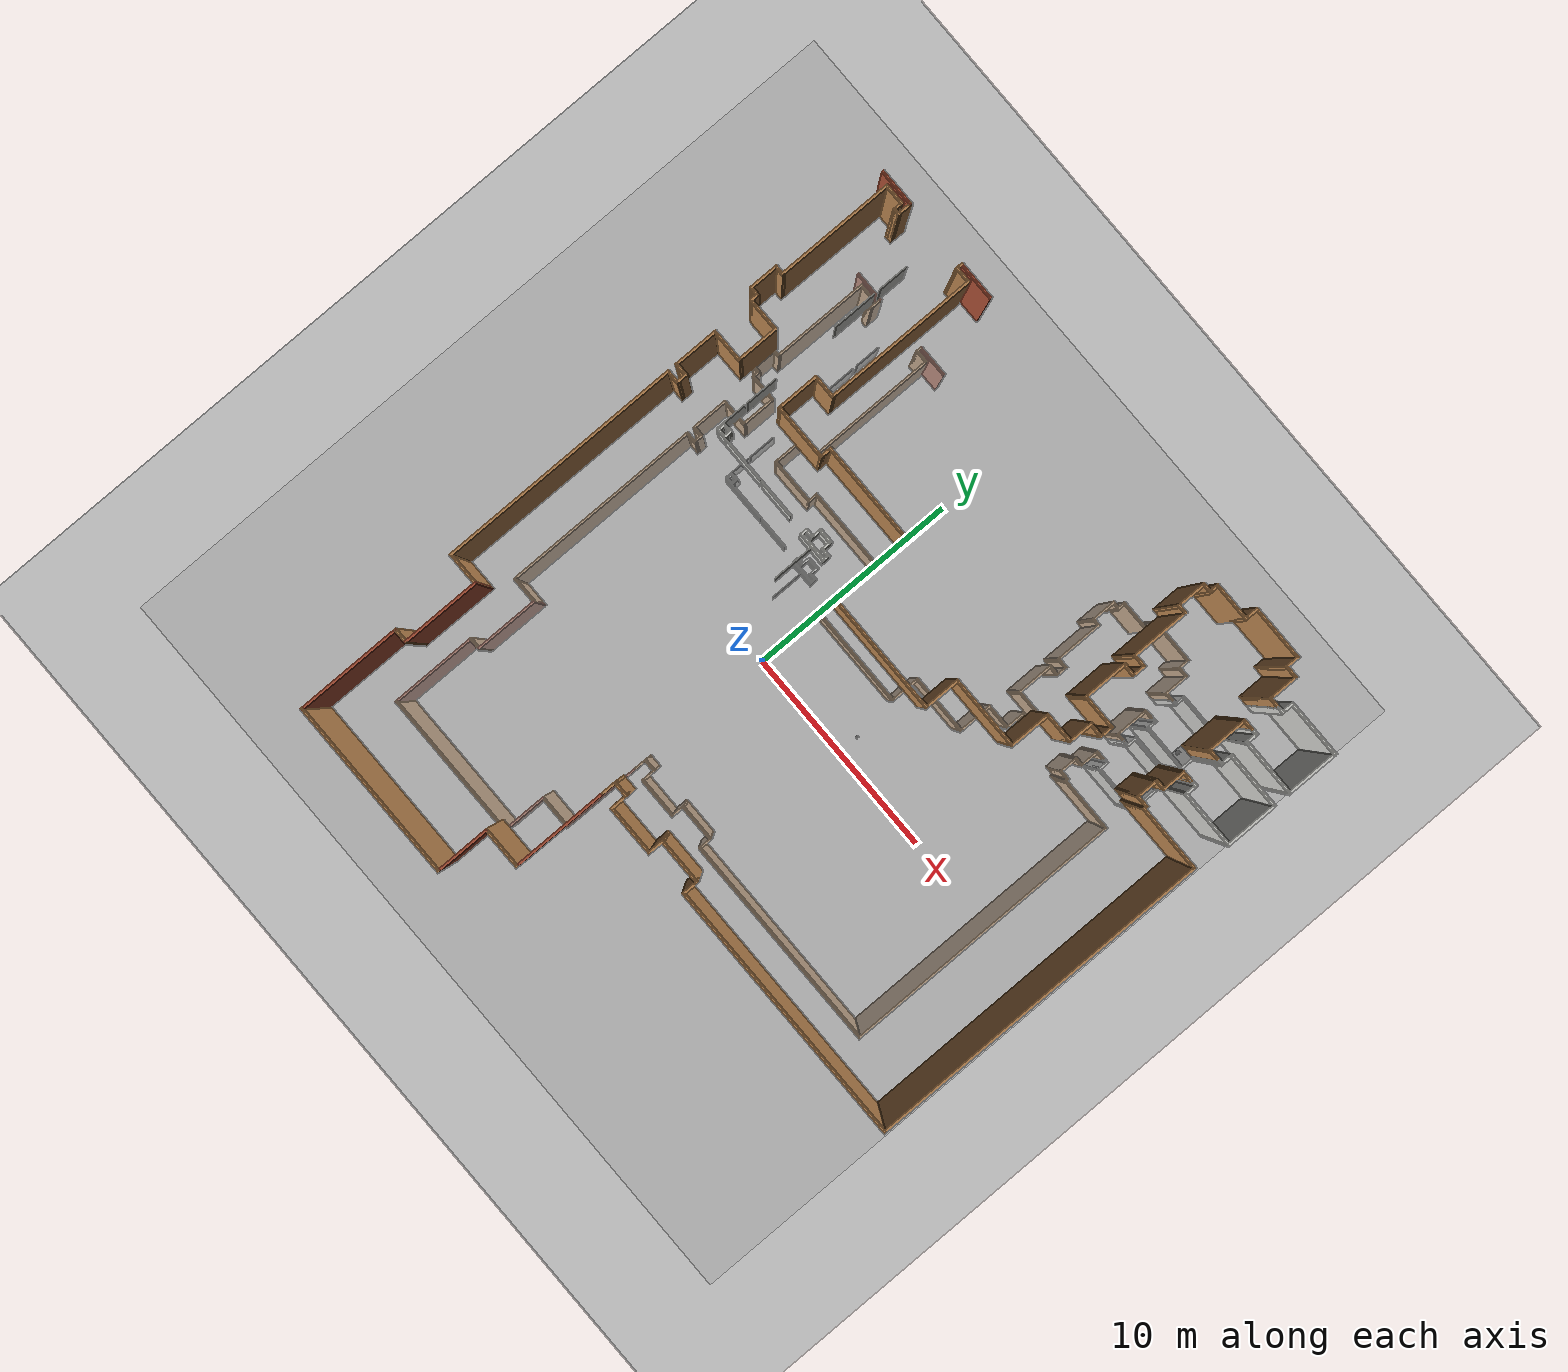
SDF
<sdf version="1.7">
 <world name="default">
  <include><uri>model://ground_plane</uri></include>
  <include><uri>model://sun</uri></include>
  <model name="cube_1f">
   <static>true</static>
   <include><uri>model://cube</uri></include>
   <pose>5.0 1.0 0.05 0 0 0</pose>
  </model>
  <model name="cube_3f">
   <static>true</static>
   <include><uri>model://cube</uri></include>
   <pose>11.5 8.7 10.05 0 0 0</pose>
  </model>
  <physics type="ode">
   <max_step_size>0.01</max_step_size>
   <real_time_factor>1</real_time_factor>
   <real_time_update_rate>100</real_time_update_rate>
   <gravity>0 0 -9.8</gravity>
  </physics>
  <model name="link_1F_model">
   <static>true</static>
   <model name="link_1F"><static>true</static><include><uri>model://test-floor</uri></include></model>
  </model>
  <model name="link_3F_model">
   <pose>0 0 10 0 0 0</pose>
   <static>true</static>
   <model name="link_3F_floor">
    <static>true</static>
    <link name="3f_plane">
     <visual name="3f_plane_Visual">
      <geometry><box><size>30 30 0.01</size></box></geometry>
      <transparency>0.5</transparency>
     </visual>
     <collision name="3f_plane_Collision"><geometry><box><size>30 30 0.01</size></box></geometry></collision>
    </link>
   </model>
   <model name="link_3F"><static>true</static><include><uri>model://test-floor</uri></include></model>
  </model>
 </world>
</sdf>

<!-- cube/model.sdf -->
<sdf version='1.7'>
  <model name='cube'>
    <link name='link_1'>
      <inertial>
        <mass>0.0222227</mass>
        <inertia>
          <ixx>0.00029276</ixx>
          <ixy>0</ixy>
          <ixz>0</ixz>
          <iyy>0.00029276</iyy>
          <iyz>0</iyz>
          <izz>0.00029276</izz>
        </inertia>
        <pose>0 0 0 0 -0 0</pose>
      </inertial>
      <pose>0 0 0 0 -0 0</pose>
      <visual name='visual'>
        <pose>0 0 0 0 -0 0</pose>
        <geometry>
          <box>
            <size>0.1 0.1 0.1</size>
          </box>
        </geometry>
        <material>
          <lighting>1</lighting>
          <script>
            <uri>file://media/materials/scripts/gazebo.material</uri>
            <name>Gazebo/Grey</name>
          </script>
          <shader type='pixel'/>
        </material>
        <transparency>0</transparency>
        <cast_shadows>1</cast_shadows>
      </visual>
      <collision name='collision'>
        <laser_retro>0</laser_retro>
        <max_contacts>10</max_contacts>
        <pose>0 0 0 0 -0 0</pose>
        <geometry>
          <box>
            <size>0.1 0.1 0.1</size>
          </box>
        </geometry>
        <surface>
          <friction>
            <ode>
              <mu>1</mu>
              <mu2>1</mu2>
              <fdir1>0 0 0</fdir1>
              <slip1>0</slip1>
              <slip2>0</slip2>
            </ode>
            <torsional>
              <coefficient>1</coefficient>
              <patch_radius>0</patch_radius>
              <surface_radius>0</surface_radius>
              <use_patch_radius>1</use_patch_radius>
              <ode>
                <slip>0</slip>
              </ode>
            </torsional>
          </friction>
          <bounce>
            <restitution_coefficient>0</restitution_coefficient>
            <threshold>1e+06</threshold>
          </bounce>
          <contact>
            <collide_without_contact>0</collide_without_contact>
            <collide_without_contact_bitmask>1</collide_without_contact_bitmask>
            <collide_bitmask>1</collide_bitmask>
            <ode>
              <soft_cfm>0</soft_cfm>
              <soft_erp>0.2</soft_erp>
              <kp>1e+13</kp>
              <kd>1</kd>
              <max_vel>0.01</max_vel>
              <min_depth>0</min_depth>
            </ode>
            <bullet>
              <split_impulse>1</split_impulse>
              <split_impulse_penetration_threshold>-0.01</split_impulse_penetration_threshold>
              <soft_cfm>0</soft_cfm>
              <soft_erp>0.2</soft_erp>
              <kp>1e+13</kp>
              <kd>1</kd>
            </bullet>
          </contact>
        </surface>
      </collision>
    </link>
    <static>0</static>
    <allow_auto_disable>1</allow_auto_disable>
  </model>
</sdf>

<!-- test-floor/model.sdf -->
<sdf version='1.7'>
    <model name='miraikan_3F_gate_and_elevator'>
      <link name='Wall_100'>
        <pose>5.2575 7.4925 0 0 -0 1.5708</pose>
        <self_collide>0</self_collide>
        <enable_wind>0</enable_wind>
        <kinematic>0</kinematic>
        <visual name='Wall_100_Visual'>
          <pose>0 0 1.25 0 -0 0</pose>
          <geometry>
            <box>
              <size>1.695 0.1 2.5</size>
            </box>
          </geometry>
          <material>
            <script>
              <uri>file://media/materials/scripts/gazebo.material</uri>
              <name>Gazebo/Wood</name>
            </script>
            <ambient>1 1 1 1</ambient>
            <shader type='pixel'/>
          </material>
          <meta>
            <layer>0</layer>
          </meta>
          <transparency>0</transparency>
          <cast_shadows>1</cast_shadows>
        </visual>
        <collision name='Wall_100_Collision'>
          <laser_retro>0</laser_retro>
          <max_contacts>10</max_contacts>
          <pose>0 0 1.25 0 -0 0</pose>
          <geometry>
            <box>
              <size>1.695 0.1 2.5</size>
            </box>
          </geometry>
          <surface>
            <friction>
              <ode>
                <mu>1</mu>
                <mu2>1</mu2>
                <fdir1>0 0 0</fdir1>
                <slip1>0</slip1>
                <slip2>0</slip2>
              </ode>
              <torsional>
                <coefficient>1</coefficient>
                <patch_radius>0</patch_radius>
                <surface_radius>0</surface_radius>
                <use_patch_radius>1</use_patch_radius>
                <ode>
                  <slip>0</slip>
                </ode>
              </torsional>
            </friction>
            <bounce>
              <restitution_coefficient>0</restitution_coefficient>
              <threshold>1e+06</threshold>
            </bounce>
            <contact>
              <collide_without_contact>0</collide_without_contact>
              <collide_without_contact_bitmask>1</collide_without_contact_bitmask>
              <collide_bitmask>1</collide_bitmask>
              <ode>
                <soft_cfm>0</soft_cfm>
                <soft_erp>0.2</soft_erp>
                <kp>1e+13</kp>
                <kd>1</kd>
                <max_vel>0.01</max_vel>
                <min_depth>0</min_depth>
              </ode>
              <bullet>
                <split_impulse>1</split_impulse>
                <split_impulse_penetration_threshold>-0.01</split_impulse_penetration_threshold>
                <soft_cfm>0</soft_cfm>
                <soft_erp>0.2</soft_erp>
                <kp>1e+13</kp>
                <kd>1</kd>
              </bullet>
            </contact>
          </surface>
        </collision>
      </link>
      <link name='Wall_102'>
        <pose>5.4825 8.29 0 0 -0 0</pose>
        <self_collide>0</self_collide>
        <enable_wind>0</enable_wind>
        <kinematic>0</kinematic>
        <visual name='Wall_102_Visual'>
          <pose>0 0 1.25 0 -0 0</pose>
          <geometry>
            <box>
              <size>0.55 0.1 2.5</size>
            </box>
          </geometry>
          <material>
            <script>
              <uri>file://media/materials/scripts/gazebo.material</uri>
              <name>Gazebo/Wood</name>
            </script>
            <ambient>1 1 1 1</ambient>
            <shader type='pixel'/>
          </material>
          <meta>
            <layer>0</layer>
          </meta>
          <transparency>0</transparency>
          <cast_shadows>1</cast_shadows>
        </visual>
        <collision name='Wall_102_Collision'>
          <laser_retro>0</laser_retro>
          <max_contacts>10</max_contacts>
          <pose>0 0 1.25 0 -0 0</pose>
          <geometry>
            <box>
              <size>0.55 0.1 2.5</size>
            </box>
          </geometry>
          <surface>
            <friction>
              <ode>
                <mu>1</mu>
                <mu2>1</mu2>
                <fdir1>0 0 0</fdir1>
                <slip1>0</slip1>
                <slip2>0</slip2>
              </ode>
              <torsional>
                <coefficient>1</coefficient>
                <patch_radius>0</patch_radius>
                <surface_radius>0</surface_radius>
                <use_patch_radius>1</use_patch_radius>
                <ode>
                  <slip>0</slip>
                </ode>
              </torsional>
            </friction>
            <bounce>
              <restitution_coefficient>0</restitution_coefficient>
              <threshold>1e+06</threshold>
            </bounce>
            <contact>
              <collide_without_contact>0</collide_without_contact>
              <collide_without_contact_bitmask>1</collide_without_contact_bitmask>
              <collide_bitmask>1</collide_bitmask>
              <ode>
                <soft_cfm>0</soft_cfm>
                <soft_erp>0.2</soft_erp>
                <kp>1e+13</kp>
                <kd>1</kd>
                <max_vel>0.01</max_vel>
                <min_depth>0</min_depth>
              </ode>
              <bullet>
                <split_impulse>1</split_impulse>
                <split_impulse_penetration_threshold>-0.01</split_impulse_penetration_threshold>
                <soft_cfm>0</soft_cfm>
                <soft_erp>0.2</soft_erp>
                <kp>1e+13</kp>
                <kd>1</kd>
              </bullet>
            </contact>
          </surface>
        </collision>
      </link>
      <link name='Wall_104'>
        <pose>5.7075 8.515 0 0 -0 1.5708</pose>
        <self_collide>0</self_collide>
        <enable_wind>0</enable_wind>
        <kinematic>0</kinematic>
        <visual name='Wall_104_Visual'>
          <pose>0 0 1.25 0 -0 0</pose>
          <geometry>
            <box>
              <size>0.55 0.1 2.5</size>
            </box>
          </geometry>
          <material>
            <script>
              <uri>file://media/materials/scripts/gazebo.material</uri>
              <name>Gazebo/Wood</name>
            </script>
            <ambient>1 1 1 1</ambient>
            <shader type='pixel'/>
          </material>
          <meta>
            <layer>0</layer>
          </meta>
          <transparency>0</transparency>
          <cast_shadows>1</cast_shadows>
        </visual>
        <collision name='Wall_104_Collision'>
          <laser_retro>0</laser_retro>
          <max_contacts>10</max_contacts>
          <pose>0 0 1.25 0 -0 0</pose>
          <geometry>
            <box>
              <size>0.55 0.1 2.5</size>
            </box>
          </geometry>
          <surface>
            <friction>
              <ode>
                <mu>1</mu>
                <mu2>1</mu2>
                <fdir1>0 0 0</fdir1>
                <slip1>0</slip1>
                <slip2>0</slip2>
              </ode>
              <torsional>
                <coefficient>1</coefficient>
                <patch_radius>0</patch_radius>
                <surface_radius>0</surface_radius>
                <use_patch_radius>1</use_patch_radius>
                <ode>
                  <slip>0</slip>
                </ode>
              </torsional>
            </friction>
            <bounce>
              <restitution_coefficient>0</restitution_coefficient>
              <threshold>1e+06</threshold>
            </bounce>
            <contact>
              <collide_without_contact>0</collide_without_contact>
              <collide_without_contact_bitmask>1</collide_without_contact_bitmask>
              <collide_bitmask>1</collide_bitmask>
              <ode>
                <soft_cfm>0</soft_cfm>
                <soft_erp>0.2</soft_erp>
                <kp>1e+13</kp>
                <kd>1</kd>
                <max_vel>0.01</max_vel>
                <min_depth>0</min_depth>
              </ode>
              <bullet>
                <split_impulse>1</split_impulse>
                <split_impulse_penetration_threshold>-0.01</split_impulse_penetration_threshold>
                <soft_cfm>0</soft_cfm>
                <soft_erp>0.2</soft_erp>
                <kp>1e+13</kp>
                <kd>1</kd>
              </bullet>
            </contact>
          </surface>
        </collision>
      </link>
      <link name='Wall_106'>
        <pose>5.4825 8.74 0 0 -0 3.14159</pose>
        <self_collide>0</self_collide>
        <enable_wind>0</enable_wind>
        <kinematic>0</kinematic>
        <visual name='Wall_106_Visual'>
          <pose>0 0 1.25 0 -0 0</pose>
          <geometry>
            <box>
              <size>0.55 0.1 2.5</size>
            </box>
          </geometry>
          <material>
            <script>
              <uri>file://media/materials/scripts/gazebo.material</uri>
              <name>Gazebo/Wood</name>
            </script>
            <ambient>1 1 1 1</ambient>
            <shader type='pixel'/>
          </material>
          <meta>
            <layer>0</layer>
          </meta>
          <transparency>0</transparency>
          <cast_shadows>1</cast_shadows>
        </visual>
        <collision name='Wall_106_Collision'>
          <laser_retro>0</laser_retro>
          <max_contacts>10</max_contacts>
          <pose>0 0 1.25 0 -0 0</pose>
          <geometry>
            <box>
              <size>0.55 0.1 2.5</size>
            </box>
          </geometry>
          <surface>
            <friction>
              <ode>
                <mu>1</mu>
                <mu2>1</mu2>
                <fdir1>0 0 0</fdir1>
                <slip1>0</slip1>
                <slip2>0</slip2>
              </ode>
              <torsional>
                <coefficient>1</coefficient>
                <patch_radius>0</patch_radius>
                <surface_radius>0</surface_radius>
                <use_patch_radius>1</use_patch_radius>
                <ode>
                  <slip>0</slip>
                </ode>
              </torsional>
            </friction>
            <bounce>
              <restitution_coefficient>0</restitution_coefficient>
              <threshold>1e+06</threshold>
            </bounce>
            <contact>
              <collide_without_contact>0</collide_without_contact>
              <collide_without_contact_bitmask>1</collide_without_contact_bitmask>
              <collide_bitmask>1</collide_bitmask>
              <ode>
                <soft_cfm>0</soft_cfm>
                <soft_erp>0.2</soft_erp>
                <kp>1e+13</kp>
                <kd>1</kd>
                <max_vel>0.01</max_vel>
                <min_depth>0</min_depth>
              </ode>
              <bullet>
                <split_impulse>1</split_impulse>
                <split_impulse_penetration_threshold>-0.01</split_impulse_penetration_threshold>
                <soft_cfm>0</soft_cfm>
                <soft_erp>0.2</soft_erp>
                <kp>1e+13</kp>
                <kd>1</kd>
              </bullet>
            </contact>
          </surface>
        </collision>
      </link>
      <link name='Wall_108'>
        <pose>5.2575 9.795 0 0 -0 1.5708</pose>
        <self_collide>0</self_collide>
        <enable_wind>0</enable_wind>
        <kinematic>0</kinematic>
        <visual name='Wall_108_Visual'>
          <pose>0 0 1.25 0 -0 0</pose>
          <geometry>
            <box>
              <size>2.21 0.1 2.5</size>
            </box>
          </geometry>
          <material>
            <script>
              <uri>file://media/materials/scripts/gazebo.material</uri>
              <name>Gazebo/Wood</name>
            </script>
            <ambient>1 1 1 1</ambient>
            <shader type='pixel'/>
          </material>
          <meta>
            <layer>0</layer>
          </meta>
          <transparency>0</transparency>
          <cast_shadows>1</cast_shadows>
        </visual>
        <collision name='Wall_108_Collision'>
          <laser_retro>0</laser_retro>
          <max_contacts>10</max_contacts>
          <pose>0 0 1.25 0 -0 0</pose>
          <geometry>
            <box>
              <size>2.21 0.1 2.5</size>
            </box>
          </geometry>
          <surface>
            <friction>
              <ode>
                <mu>1</mu>
                <mu2>1</mu2>
                <fdir1>0 0 0</fdir1>
                <slip1>0</slip1>
                <slip2>0</slip2>
              </ode>
              <torsional>
                <coefficient>1</coefficient>
                <patch_radius>0</patch_radius>
                <surface_radius>0</surface_radius>
                <use_patch_radius>1</use_patch_radius>
                <ode>
                  <slip>0</slip>
                </ode>
              </torsional>
            </friction>
            <bounce>
              <restitution_coefficient>0</restitution_coefficient>
              <threshold>1e+06</threshold>
            </bounce>
            <contact>
              <collide_without_contact>0</collide_without_contact>
              <collide_without_contact_bitmask>1</collide_without_contact_bitmask>
              <collide_bitmask>1</collide_bitmask>
              <ode>
                <soft_cfm>0</soft_cfm>
                <soft_erp>0.2</soft_erp>
                <kp>1e+13</kp>
                <kd>1</kd>
                <max_vel>0.01</max_vel>
                <min_depth>0</min_depth>
              </ode>
              <bullet>
                <split_impulse>1</split_impulse>
                <split_impulse_penetration_threshold>-0.01</split_impulse_penetration_threshold>
                <soft_cfm>0</soft_cfm>
                <soft_erp>0.2</soft_erp>
                <kp>1e+13</kp>
                <kd>1</kd>
              </bullet>
            </contact>
          </surface>
        </collision>
      </link>
      <link name='Wall_110'>
        <pose>5.1025 10.85 0 0 -0 3.14159</pose>
        <self_collide>0</self_collide>
        <enable_wind>0</enable_wind>
        <kinematic>0</kinematic>
        <visual name='Wall_110_Visual'>
          <pose>0 0 1.25 0 -0 0</pose>
          <geometry>
            <box>
              <size>0.41 0.1 2.5</size>
            </box>
          </geometry>
          <material>
            <script>
              <uri>file://media/materials/scripts/gazebo.material</uri>
              <name>Gazebo/Wood</name>
            </script>
            <ambient>1 1 1 1</ambient>
            <shader type='pixel'/>
          </material>
          <meta>
            <layer>0</layer>
          </meta>
          <transparency>0</transparency>
          <cast_shadows>1</cast_shadows>
        </visual>
        <collision name='Wall_110_Collision'>
          <laser_retro>0</laser_retro>
          <max_contacts>10</max_contacts>
          <pose>0 0 1.25 0 -0 0</pose>
          <geometry>
            <box>
              <size>0.41 0.1 2.5</size>
            </box>
          </geometry>
          <surface>
            <friction>
              <ode>
                <mu>1</mu>
                <mu2>1</mu2>
                <fdir1>0 0 0</fdir1>
                <slip1>0</slip1>
                <slip2>0</slip2>
              </ode>
              <torsional>
                <coefficient>1</coefficient>
                <patch_radius>0</patch_radius>
                <surface_radius>0</surface_radius>
                <use_patch_radius>1</use_patch_radius>
                <ode>
                  <slip>0</slip>
                </ode>
              </torsional>
            </friction>
            <bounce>
              <restitution_coefficient>0</restitution_coefficient>
              <threshold>1e+06</threshold>
            </bounce>
            <contact>
              <collide_without_contact>0</collide_without_contact>
              <collide_without_contact_bitmask>1</collide_without_contact_bitmask>
              <collide_bitmask>1</collide_bitmask>
              <ode>
                <soft_cfm>0</soft_cfm>
                <soft_erp>0.2</soft_erp>
                <kp>1e+13</kp>
                <kd>1</kd>
                <max_vel>0.01</max_vel>
                <min_depth>0</min_depth>
              </ode>
              <bullet>
                <split_impulse>1</split_impulse>
                <split_impulse_penetration_threshold>-0.01</split_impulse_penetration_threshold>
                <soft_cfm>0</soft_cfm>
                <soft_erp>0.2</soft_erp>
                <kp>1e+13</kp>
                <kd>1</kd>
              </bullet>
            </contact>
          </surface>
        </collision>
      </link>
      <link name='Wall_112'>
        <pose>4.9475 11.375 0 0 -0 1.5708</pose>
        <self_collide>0</self_collide>
        <enable_wind>0</enable_wind>
        <kinematic>0</kinematic>
        <visual name='Wall_112_Visual'>
          <pose>0 0 1.25 0 -0 0</pose>
          <geometry>
            <box>
              <size>1.15 0.1 2.5</size>
            </box>
          </geometry>
          <material>
            <script>
              <uri>file://media/materials/scripts/gazebo.material</uri>
              <name>Gazebo/Wood</name>
            </script>
            <ambient>1 1 1 1</ambient>
            <shader type='pixel'/>
          </material>
          <meta>
            <layer>0</layer>
          </meta>
          <transparency>0</transparency>
          <cast_shadows>1</cast_shadows>
        </visual>
        <collision name='Wall_112_Collision'>
          <laser_retro>0</laser_retro>
          <max_contacts>10</max_contacts>
          <pose>0 0 1.25 0 -0 0</pose>
          <geometry>
            <box>
              <size>1.15 0.1 2.5</size>
            </box>
          </geometry>
          <surface>
            <friction>
              <ode>
                <mu>1</mu>
                <mu2>1</mu2>
                <fdir1>0 0 0</fdir1>
                <slip1>0</slip1>
                <slip2>0</slip2>
              </ode>
              <torsional>
                <coefficient>1</coefficient>
                <patch_radius>0</patch_radius>
                <surface_radius>0</surface_radius>
                <use_patch_radius>1</use_patch_radius>
                <ode>
                  <slip>0</slip>
                </ode>
              </torsional>
            </friction>
            <bounce>
              <restitution_coefficient>0</restitution_coefficient>
              <threshold>1e+06</threshold>
            </bounce>
            <contact>
              <collide_without_contact>0</collide_without_contact>
              <collide_without_contact_bitmask>1</collide_without_contact_bitmask>
              <collide_bitmask>1</collide_bitmask>
              <ode>
                <soft_cfm>0</soft_cfm>
                <soft_erp>0.2</soft_erp>
                <kp>1e+13</kp>
                <kd>1</kd>
                <max_vel>0.01</max_vel>
                <min_depth>0</min_depth>
              </ode>
              <bullet>
                <split_impulse>1</split_impulse>
                <split_impulse_penetration_threshold>-0.01</split_impulse_penetration_threshold>
                <soft_cfm>0</soft_cfm>
                <soft_erp>0.2</soft_erp>
                <kp>1e+13</kp>
                <kd>1</kd>
              </bullet>
            </contact>
          </surface>
        </collision>
      </link>
      <link name='Wall_114'>
        <pose>5.1025 11.9 0 0 -0 0</pose>
        <self_collide>0</self_collide>
        <enable_wind>0</enable_wind>
        <kinematic>0</kinematic>
        <visual name='Wall_114_Visual'>
          <pose>0 0 1.25 0 -0 0</pose>
          <geometry>
            <box>
              <size>0.41 0.1 2.5</size>
            </box>
          </geometry>
          <material>
            <script>
              <uri>file://media/materials/scripts/gazebo.material</uri>
              <name>Gazebo/Wood</name>
            </script>
            <ambient>1 1 1 1</ambient>
            <shader type='pixel'/>
          </material>
          <meta>
            <layer>0</layer>
          </meta>
          <transparency>0</transparency>
          <cast_shadows>1</cast_shadows>
        </visual>
        <collision name='Wall_114_Collision'>
          <laser_retro>0</laser_retro>
          <max_contacts>10</max_contacts>
          <pose>0 0 1.25 0 -0 0</pose>
          <geometry>
            <box>
              <size>0.41 0.1 2.5</size>
            </box>
          </geometry>
          <surface>
            <friction>
              <ode>
                <mu>1</mu>
                <mu2>1</mu2>
                <fdir1>0 0 0</fdir1>
                <slip1>0</slip1>
                <slip2>0</slip2>
              </ode>
              <torsional>
                <coefficient>1</coefficient>
                <patch_radius>0</patch_radius>
                <surface_radius>0</surface_radius>
                <use_patch_radius>1</use_patch_radius>
                <ode>
                  <slip>0</slip>
                </ode>
              </torsional>
            </friction>
            <bounce>
              <restitution_coefficient>0</restitution_coefficient>
              <threshold>1e+06</threshold>
            </bounce>
            <contact>
              <collide_without_contact>0</collide_without_contact>
              <collide_without_contact_bitmask>1</collide_without_contact_bitmask>
              <collide_bitmask>1</collide_bitmask>
              <ode>
                <soft_cfm>0</soft_cfm>
                <soft_erp>0.2</soft_erp>
                <kp>1e+13</kp>
                <kd>1</kd>
                <max_vel>0.01</max_vel>
                <min_depth>0</min_depth>
              </ode>
              <bullet>
                <split_impulse>1</split_impulse>
                <split_impulse_penetration_threshold>-0.01</split_impulse_penetration_threshold>
                <soft_cfm>0</soft_cfm>
                <soft_erp>0.2</soft_erp>
                <kp>1e+13</kp>
                <kd>1</kd>
              </bullet>
            </contact>
          </surface>
        </collision>
      </link>
      <link name='Wall_119'>
        <pose>-3.8625 -11.67 0 0 -0 1.5708</pose>
        <self_collide>0</self_collide>
        <enable_wind>0</enable_wind>
        <kinematic>0</kinematic>
        <visual name='Wall_119_Visual'>
          <pose>0 0 1.25 0 -0 0</pose>
          <geometry>
            <box>
              <size>2.1 0.1 2.5</size>
            </box>
          </geometry>
          <material>
            <script>
              <uri>file://media/materials/scripts/gazebo.material</uri>
              <name>Gazebo/Bricks</name>
            </script>
            <ambient>1 1 1 1</ambient>
            <shader type='pixel'/>
          </material>
          <meta>
            <layer>0</layer>
          </meta>
          <transparency>0</transparency>
          <cast_shadows>1</cast_shadows>
        </visual>
        <collision name='Wall_119_Collision'>
          <laser_retro>0</laser_retro>
          <max_contacts>10</max_contacts>
          <pose>0 0 1.25 0 -0 0</pose>
          <geometry>
            <box>
              <size>2.1 0.1 2.5</size>
            </box>
          </geometry>
          <surface>
            <friction>
              <ode>
                <mu>1</mu>
                <mu2>1</mu2>
                <fdir1>0 0 0</fdir1>
                <slip1>0</slip1>
                <slip2>0</slip2>
              </ode>
              <torsional>
                <coefficient>1</coefficient>
                <patch_radius>0</patch_radius>
                <surface_radius>0</surface_radius>
                <use_patch_radius>1</use_patch_radius>
                <ode>
                  <slip>0</slip>
                </ode>
              </torsional>
            </friction>
            <bounce>
              <restitution_coefficient>0</restitution_coefficient>
              <threshold>1e+06</threshold>
            </bounce>
            <contact>
              <collide_without_contact>0</collide_without_contact>
              <collide_without_contact_bitmask>1</collide_without_contact_bitmask>
              <collide_bitmask>1</collide_bitmask>
              <ode>
                <soft_cfm>0</soft_cfm>
                <soft_erp>0.2</soft_erp>
                <kp>1e+13</kp>
                <kd>1</kd>
                <max_vel>0.01</max_vel>
                <min_depth>0</min_depth>
              </ode>
              <bullet>
                <split_impulse>1</split_impulse>
                <split_impulse_penetration_threshold>-0.01</split_impulse_penetration_threshold>
                <soft_cfm>0</soft_cfm>
                <soft_erp>0.2</soft_erp>
                <kp>1e+13</kp>
                <kd>1</kd>
              </bullet>
            </contact>
          </surface>
        </collision>
      </link>
      <link name='Wall_121'>
        <pose>-3.1125 -10.67 0 0 -0 0</pose>
        <self_collide>0</self_collide>
        <enable_wind>0</enable_wind>
        <kinematic>0</kinematic>
        <visual name='Wall_121_Visual'>
          <pose>0 0 1.25 0 -0 0</pose>
          <geometry>
            <box>
              <size>1.6 0.1 2.5</size>
            </box>
          </geometry>
          <material>
            <script>
              <uri>file://media/materials/scripts/gazebo.material</uri>
              <name>Gazebo/Wood</name>
            </script>
            <ambient>1 1 1 1</ambient>
            <shader type='pixel'/>
          </material>
          <meta>
            <layer>0</layer>
          </meta>
          <transparency>0</transparency>
          <cast_shadows>1</cast_shadows>
        </visual>
        <collision name='Wall_121_Collision'>
          <laser_retro>0</laser_retro>
          <max_contacts>10</max_contacts>
          <pose>0 0 1.25 0 -0 0</pose>
          <geometry>
            <box>
              <size>1.6 0.1 2.5</size>
            </box>
          </geometry>
          <surface>
            <friction>
              <ode>
                <mu>1</mu>
                <mu2>1</mu2>
                <fdir1>0 0 0</fdir1>
                <slip1>0</slip1>
                <slip2>0</slip2>
              </ode>
              <torsional>
                <coefficient>1</coefficient>
                <patch_radius>0</patch_radius>
                <surface_radius>0</surface_radius>
                <use_patch_radius>1</use_patch_radius>
                <ode>
                  <slip>0</slip>
                </ode>
              </torsional>
            </friction>
            <bounce>
              <restitution_coefficient>0</restitution_coefficient>
              <threshold>1e+06</threshold>
            </bounce>
            <contact>
              <collide_without_contact>0</collide_without_contact>
              <collide_without_contact_bitmask>1</collide_without_contact_bitmask>
              <collide_bitmask>1</collide_bitmask>
              <ode>
                <soft_cfm>0</soft_cfm>
                <soft_erp>0.2</soft_erp>
                <kp>1e+13</kp>
                <kd>1</kd>
                <max_vel>0.01</max_vel>
                <min_depth>0</min_depth>
              </ode>
              <bullet>
                <split_impulse>1</split_impulse>
                <split_impulse_penetration_threshold>-0.01</split_impulse_penetration_threshold>
                <soft_cfm>0</soft_cfm>
                <soft_erp>0.2</soft_erp>
                <kp>1e+13</kp>
                <kd>1</kd>
              </bullet>
            </contact>
          </surface>
        </collision>
      </link>
      <link name='Wall_123'>
        <pose>-2.3625 -8.92 0 0 -0 1.5708</pose>
        <self_collide>0</self_collide>
        <enable_wind>0</enable_wind>
        <kinematic>0</kinematic>
        <visual name='Wall_123_Visual'>
          <pose>0 0 1.25 0 -0 0</pose>
          <geometry>
            <box>
              <size>3.6 0.1 2.5</size>
            </box>
          </geometry>
          <material>
            <script>
              <uri>file://media/materials/scripts/gazebo.material</uri>
              <name>Gazebo/Bricks</name>
            </script>
            <ambient>1 1 1 1</ambient>
            <shader type='pixel'/>
          </material>
          <meta>
            <layer>0</layer>
          </meta>
          <transparency>0</transparency>
          <cast_shadows>1</cast_shadows>
        </visual>
        <collision name='Wall_123_Collision'>
          <laser_retro>0</laser_retro>
          <max_contacts>10</max_contacts>
          <pose>0 0 1.25 0 -0 0</pose>
          <geometry>
            <box>
              <size>3.6 0.1 2.5</size>
            </box>
          </geometry>
          <surface>
            <friction>
              <ode>
                <mu>1</mu>
                <mu2>1</mu2>
                <fdir1>0 0 0</fdir1>
                <slip1>0</slip1>
                <slip2>0</slip2>
              </ode>
              <torsional>
                <coefficient>1</coefficient>
                <patch_radius>0</patch_radius>
                <surface_radius>0</surface_radius>
                <use_patch_radius>1</use_patch_radius>
                <ode>
                  <slip>0</slip>
                </ode>
              </torsional>
            </friction>
            <bounce>
              <restitution_coefficient>0</restitution_coefficient>
              <threshold>1e+06</threshold>
            </bounce>
            <contact>
              <collide_without_contact>0</collide_without_contact>
              <collide_without_contact_bitmask>1</collide_without_contact_bitmask>
              <collide_bitmask>1</collide_bitmask>
              <ode>
                <soft_cfm>0</soft_cfm>
                <soft_erp>0.2</soft_erp>
                <kp>1e+13</kp>
                <kd>1</kd>
                <max_vel>0.01</max_vel>
                <min_depth>0</min_depth>
              </ode>
              <bullet>
                <split_impulse>1</split_impulse>
                <split_impulse_penetration_threshold>-0.01</split_impulse_penetration_threshold>
                <soft_cfm>0</soft_cfm>
                <soft_erp>0.2</soft_erp>
                <kp>1e+13</kp>
                <kd>1</kd>
              </bullet>
            </contact>
          </surface>
        </collision>
      </link>
      <link name='Wall_125'>
        <pose>-2.3625 -6.87 0 0 -0 1.5708</pose>
        <self_collide>0</self_collide>
        <enable_wind>0</enable_wind>
        <kinematic>0</kinematic>
        <visual name='Wall_125_Visual'>
          <pose>0 0 1.25 0 -0 0</pose>
          <geometry>
            <box>
              <size>0.7 0.1 2.5</size>
            </box>
          </geometry>
          <material>
            <script>
              <uri>file://media/materials/scripts/gazebo.material</uri>
              <name>Gazebo/Wood</name>
            </script>
            <ambient>1 1 1 1</ambient>
            <shader type='pixel'/>
          </material>
          <meta>
            <layer>0</layer>
          </meta>
          <transparency>0</transparency>
          <cast_shadows>1</cast_shadows>
        </visual>
        <collision name='Wall_125_Collision'>
          <laser_retro>0</laser_retro>
          <max_contacts>10</max_contacts>
          <pose>0 0 1.25 0 -0 0</pose>
          <geometry>
            <box>
              <size>0.7 0.1 2.5</size>
            </box>
          </geometry>
          <surface>
            <friction>
              <ode>
                <mu>1</mu>
                <mu2>1</mu2>
                <fdir1>0 0 0</fdir1>
                <slip1>0</slip1>
                <slip2>0</slip2>
              </ode>
              <torsional>
                <coefficient>1</coefficient>
                <patch_radius>0</patch_radius>
                <surface_radius>0</surface_radius>
                <use_patch_radius>1</use_patch_radius>
                <ode>
                  <slip>0</slip>
                </ode>
              </torsional>
            </friction>
            <bounce>
              <restitution_coefficient>0</restitution_coefficient>
              <threshold>1e+06</threshold>
            </bounce>
            <contact>
              <collide_without_contact>0</collide_without_contact>
              <collide_without_contact_bitmask>1</collide_without_contact_bitmask>
              <collide_bitmask>1</collide_bitmask>
              <ode>
                <soft_cfm>0</soft_cfm>
                <soft_erp>0.2</soft_erp>
                <kp>1e+13</kp>
                <kd>1</kd>
                <max_vel>0.01</max_vel>
                <min_depth>0</min_depth>
              </ode>
              <bullet>
                <split_impulse>1</split_impulse>
                <split_impulse_penetration_threshold>-0.01</split_impulse_penetration_threshold>
                <soft_cfm>0</soft_cfm>
                <soft_erp>0.2</soft_erp>
                <kp>1e+13</kp>
                <kd>1</kd>
              </bullet>
            </contact>
          </surface>
        </collision>
      </link>
      <link name='Wall_127'>
        <pose>-2.0875 -6.57 0 0 -0 0</pose>
        <self_collide>0</self_collide>
        <enable_wind>0</enable_wind>
        <kinematic>0</kinematic>
        <visual name='Wall_127_Visual'>
          <pose>0 0 1.25 0 -0 0</pose>
          <geometry>
            <box>
              <size>0.65 0.1 2.5</size>
            </box>
          </geometry>
          <material>
            <script>
              <uri>file://media/materials/scripts/gazebo.material</uri>
              <name>Gazebo/Wood</name>
            </script>
            <ambient>1 1 1 1</ambient>
            <shader type='pixel'/>
          </material>
          <meta>
            <layer>0</layer>
          </meta>
          <transparency>0</transparency>
          <cast_shadows>1</cast_shadows>
        </visual>
        <collision name='Wall_127_Collision'>
          <laser_retro>0</laser_retro>
          <max_contacts>10</max_contacts>
          <pose>0 0 1.25 0 -0 0</pose>
          <geometry>
            <box>
              <size>0.65 0.1 2.5</size>
            </box>
          </geometry>
          <surface>
            <friction>
              <ode>
                <mu>1</mu>
                <mu2>1</mu2>
                <fdir1>0 0 0</fdir1>
                <slip1>0</slip1>
                <slip2>0</slip2>
              </ode>
              <torsional>
                <coefficient>1</coefficient>
                <patch_radius>0</patch_radius>
                <surface_radius>0</surface_radius>
                <use_patch_radius>1</use_patch_radius>
                <ode>
                  <slip>0</slip>
                </ode>
              </torsional>
            </friction>
            <bounce>
              <restitution_coefficient>0</restitution_coefficient>
              <threshold>1e+06</threshold>
            </bounce>
            <contact>
              <collide_without_contact>0</collide_without_contact>
              <collide_without_contact_bitmask>1</collide_without_contact_bitmask>
              <collide_bitmask>1</collide_bitmask>
              <ode>
                <soft_cfm>0</soft_cfm>
                <soft_erp>0.2</soft_erp>
                <kp>1e+13</kp>
                <kd>1</kd>
                <max_vel>0.01</max_vel>
                <min_depth>0</min_depth>
              </ode>
              <bullet>
                <split_impulse>1</split_impulse>
                <split_impulse_penetration_threshold>-0.01</split_impulse_penetration_threshold>
                <soft_cfm>0</soft_cfm>
                <soft_erp>0.2</soft_erp>
                <kp>1e+13</kp>
                <kd>1</kd>
              </bullet>
            </contact>
          </surface>
        </collision>
      </link>
      <link name='Wall_129'>
        <pose>-1.8125 -6.87 0 0 0 -1.5708</pose>
        <self_collide>0</self_collide>
        <enable_wind>0</enable_wind>
        <kinematic>0</kinematic>
        <visual name='Wall_129_Visual'>
          <pose>0 0 1.25 0 -0 0</pose>
          <geometry>
            <box>
              <size>0.7 0.1 2.5</size>
            </box>
          </geometry>
          <material>
            <script>
              <uri>file://media/materials/scripts/gazebo.material</uri>
              <name>Gazebo/Wood</name>
            </script>
            <ambient>1 1 1 1</ambient>
            <shader type='pixel'/>
          </material>
          <meta>
            <layer>0</layer>
          </meta>
          <transparency>0</transparency>
          <cast_shadows>1</cast_shadows>
        </visual>
        <collision name='Wall_129_Collision'>
          <laser_retro>0</laser_retro>
          <max_contacts>10</max_contacts>
          <pose>0 0 1.25 0 -0 0</pose>
          <geometry>
            <box>
              <size>0.7 0.1 2.5</size>
            </box>
          </geometry>
          <surface>
            <friction>
              <ode>
                <mu>1</mu>
                <mu2>1</mu2>
                <fdir1>0 0 0</fdir1>
                <slip1>0</slip1>
                <slip2>0</slip2>
              </ode>
              <torsional>
                <coefficient>1</coefficient>
                <patch_radius>0</patch_radius>
                <surface_radius>0</surface_radius>
                <use_patch_radius>1</use_patch_radius>
                <ode>
                  <slip>0</slip>
                </ode>
              </torsional>
            </friction>
            <bounce>
              <restitution_coefficient>0</restitution_coefficient>
              <threshold>1e+06</threshold>
            </bounce>
            <contact>
              <collide_without_contact>0</collide_without_contact>
              <collide_without_contact_bitmask>1</collide_without_contact_bitmask>
              <collide_bitmask>1</collide_bitmask>
              <ode>
                <soft_cfm>0</soft_cfm>
                <soft_erp>0.2</soft_erp>
                <kp>1e+13</kp>
                <kd>1</kd>
                <max_vel>0.01</max_vel>
                <min_depth>0</min_depth>
              </ode>
              <bullet>
                <split_impulse>1</split_impulse>
                <split_impulse_penetration_threshold>-0.01</split_impulse_penetration_threshold>
                <soft_cfm>0</soft_cfm>
                <soft_erp>0.2</soft_erp>
                <kp>1e+13</kp>
                <kd>1</kd>
              </bullet>
            </contact>
          </surface>
        </collision>
      </link>
      <link name='Wall_131'>
        <pose>-0.8875 -7.17 0 0 -0 0</pose>
        <self_collide>0</self_collide>
        <enable_wind>0</enable_wind>
        <kinematic>0</kinematic>
        <visual name='Wall_131_Visual'>
          <pose>0 0 1.25 0 -0 0</pose>
          <geometry>
            <box>
              <size>1.95 0.1 2.5</size>
            </box>
          </geometry>
          <material>
            <script>
              <uri>file://media/materials/scripts/gazebo.material</uri>
              <name>Gazebo/Wood</name>
            </script>
            <ambient>1 1 1 1</ambient>
            <shader type='pixel'/>
          </material>
          <meta>
            <layer>0</layer>
          </meta>
          <transparency>0</transparency>
          <cast_shadows>1</cast_shadows>
        </visual>
        <collision name='Wall_131_Collision'>
          <laser_retro>0</laser_retro>
          <max_contacts>10</max_contacts>
          <pose>0 0 1.25 0 -0 0</pose>
          <geometry>
            <box>
              <size>1.95 0.1 2.5</size>
            </box>
          </geometry>
          <surface>
            <friction>
              <ode>
                <mu>1</mu>
                <mu2>1</mu2>
                <fdir1>0 0 0</fdir1>
                <slip1>0</slip1>
                <slip2>0</slip2>
              </ode>
              <torsional>
                <coefficient>1</coefficient>
                <patch_radius>0</patch_radius>
                <surface_radius>0</surface_radius>
                <use_patch_radius>1</use_patch_radius>
                <ode>
                  <slip>0</slip>
                </ode>
              </torsional>
            </friction>
            <bounce>
              <restitution_coefficient>0</restitution_coefficient>
              <threshold>1e+06</threshold>
            </bounce>
            <contact>
              <collide_without_contact>0</collide_without_contact>
              <collide_without_contact_bitmask>1</collide_without_contact_bitmask>
              <collide_bitmask>1</collide_bitmask>
              <ode>
                <soft_cfm>0</soft_cfm>
                <soft_erp>0.2</soft_erp>
                <kp>1e+13</kp>
                <kd>1</kd>
                <max_vel>0.01</max_vel>
                <min_depth>0</min_depth>
              </ode>
              <bullet>
                <split_impulse>1</split_impulse>
                <split_impulse_penetration_threshold>-0.01</split_impulse_penetration_threshold>
                <soft_cfm>0</soft_cfm>
                <soft_erp>0.2</soft_erp>
                <kp>1e+13</kp>
                <kd>1</kd>
              </bullet>
            </contact>
          </surface>
        </collision>
      </link>
      <link name='Wall_133'>
        <pose>0.0375 -6.895 0 0 -0 1.5708</pose>
        <self_collide>0</self_collide>
        <enable_wind>0</enable_wind>
        <kinematic>0</kinematic>
        <visual name='Wall_133_Visual'>
          <pose>0 0 1.25 0 -0 0</pose>
          <geometry>
            <box>
              <size>0.65 0.1 2.5</size>
            </box>
          </geometry>
          <material>
            <script>
              <uri>file://media/materials/scripts/gazebo.material</uri>
              <name>Gazebo/Wood</name>
            </script>
            <ambient>1 1 1 1</ambient>
            <shader type='pixel'/>
          </material>
          <meta>
            <layer>0</layer>
          </meta>
          <transparency>0</transparency>
          <cast_shadows>1</cast_shadows>
        </visual>
        <collision name='Wall_133_Collision'>
          <laser_retro>0</laser_retro>
          <max_contacts>10</max_contacts>
          <pose>0 0 1.25 0 -0 0</pose>
          <geometry>
            <box>
              <size>0.65 0.1 2.5</size>
            </box>
          </geometry>
          <surface>
            <friction>
              <ode>
                <mu>1</mu>
                <mu2>1</mu2>
                <fdir1>0 0 0</fdir1>
                <slip1>0</slip1>
                <slip2>0</slip2>
              </ode>
              <torsional>
                <coefficient>1</coefficient>
                <patch_radius>0</patch_radius>
                <surface_radius>0</surface_radius>
                <use_patch_radius>1</use_patch_radius>
                <ode>
                  <slip>0</slip>
                </ode>
              </torsional>
            </friction>
            <bounce>
              <restitution_coefficient>0</restitution_coefficient>
              <threshold>1e+06</threshold>
            </bounce>
            <contact>
              <collide_without_contact>0</collide_without_contact>
              <collide_without_contact_bitmask>1</collide_without_contact_bitmask>
              <collide_bitmask>1</collide_bitmask>
              <ode>
                <soft_cfm>0</soft_cfm>
                <soft_erp>0.2</soft_erp>
                <kp>1e+13</kp>
                <kd>1</kd>
                <max_vel>0.01</max_vel>
                <min_depth>0</min_depth>
              </ode>
              <bullet>
                <split_impulse>1</split_impulse>
                <split_impulse_penetration_threshold>-0.01</split_impulse_penetration_threshold>
                <soft_cfm>0</soft_cfm>
                <soft_erp>0.2</soft_erp>
                <kp>1e+13</kp>
                <kd>1</kd>
              </bullet>
            </contact>
          </surface>
        </collision>
      </link>
      <link name='Wall_135'>
        <pose>0.8875 -6.62 0 0 -0 0</pose>
        <self_collide>0</self_collide>
        <enable_wind>0</enable_wind>
        <kinematic>0</kinematic>
        <visual name='Wall_135_Visual'>
          <pose>0 0 1.25 0 -0 0</pose>
          <geometry>
            <box>
              <size>1.8 0.1 2.5</size>
            </box>
          </geometry>
          <material>
            <script>
              <uri>file://media/materials/scripts/gazebo.material</uri>
              <name>Gazebo/Wood</name>
            </script>
            <ambient>1 1 1 1</ambient>
            <shader type='pixel'/>
          </material>
          <meta>
            <layer>0</layer>
          </meta>
          <transparency>0</transparency>
          <cast_shadows>1</cast_shadows>
        </visual>
        <collision name='Wall_135_Collision'>
          <laser_retro>0</laser_retro>
          <max_contacts>10</max_contacts>
          <pose>0 0 1.25 0 -0 0</pose>
          <geometry>
            <box>
              <size>1.8 0.1 2.5</size>
            </box>
          </geometry>
          <surface>
            <friction>
              <ode>
                <mu>1</mu>
                <mu2>1</mu2>
                <fdir1>0 0 0</fdir1>
                <slip1>0</slip1>
                <slip2>0</slip2>
              </ode>
              <torsional>
                <coefficient>1</coefficient>
                <patch_radius>0</patch_radius>
                <surface_radius>0</surface_radius>
                <use_patch_radius>1</use_patch_radius>
                <ode>
                  <slip>0</slip>
                </ode>
              </torsional>
            </friction>
            <bounce>
              <restitution_coefficient>0</restitution_coefficient>
              <threshold>1e+06</threshold>
            </bounce>
            <contact>
              <collide_without_contact>0</collide_without_contact>
              <collide_without_contact_bitmask>1</collide_without_contact_bitmask>
              <collide_bitmask>1</collide_bitmask>
              <ode>
                <soft_cfm>0</soft_cfm>
                <soft_erp>0.2</soft_erp>
                <kp>1e+13</kp>
                <kd>1</kd>
                <max_vel>0.01</max_vel>
                <min_depth>0</min_depth>
              </ode>
              <bullet>
                <split_impulse>1</split_impulse>
                <split_impulse_penetration_threshold>-0.01</split_impulse_penetration_threshold>
                <soft_cfm>0</soft_cfm>
                <soft_erp>0.2</soft_erp>
                <kp>1e+13</kp>
                <kd>1</kd>
              </bullet>
            </contact>
          </surface>
        </collision>
      </link>
      <link name='Wall_137'>
        <pose>1.7375 -6.895 0 0 0 -1.5708</pose>
        <self_collide>0</self_collide>
        <enable_wind>0</enable_wind>
        <kinematic>0</kinematic>
        <visual name='Wall_137_Visual'>
          <pose>0 0 1.25 0 -0 0</pose>
          <geometry>
            <box>
              <size>0.65 0.1 2.5</size>
            </box>
          </geometry>
          <material>
            <script>
              <uri>file://media/materials/scripts/gazebo.material</uri>
              <name>Gazebo/Wood</name>
            </script>
            <ambient>1 1 1 1</ambient>
            <shader type='pixel'/>
          </material>
          <meta>
            <layer>0</layer>
          </meta>
          <transparency>0</transparency>
          <cast_shadows>1</cast_shadows>
        </visual>
        <collision name='Wall_137_Collision'>
          <laser_retro>0</laser_retro>
          <max_contacts>10</max_contacts>
          <pose>0 0 1.25 0 -0 0</pose>
          <geometry>
            <box>
              <size>0.65 0.1 2.5</size>
            </box>
          </geometry>
          <surface>
            <friction>
              <ode>
                <mu>1</mu>
                <mu2>1</mu2>
                <fdir1>0 0 0</fdir1>
                <slip1>0</slip1>
                <slip2>0</slip2>
              </ode>
              <torsional>
                <coefficient>1</coefficient>
                <patch_radius>0</patch_radius>
                <surface_radius>0</surface_radius>
                <use_patch_radius>1</use_patch_radius>
                <ode>
                  <slip>0</slip>
                </ode>
              </torsional>
            </friction>
            <bounce>
              <restitution_coefficient>0</restitution_coefficient>
              <threshold>1e+06</threshold>
            </bounce>
            <contact>
              <collide_without_contact>0</collide_without_contact>
              <collide_without_contact_bitmask>1</collide_without_contact_bitmask>
              <collide_bitmask>1</collide_bitmask>
              <ode>
                <soft_cfm>0</soft_cfm>
                <soft_erp>0.2</soft_erp>
                <kp>1e+13</kp>
                <kd>1</kd>
                <max_vel>0.01</max_vel>
                <min_depth>0</min_depth>
              </ode>
              <bullet>
                <split_impulse>1</split_impulse>
                <split_impulse_penetration_threshold>-0.01</split_impulse_penetration_threshold>
                <soft_cfm>0</soft_cfm>
                <soft_erp>0.2</soft_erp>
                <kp>1e+13</kp>
                <kd>1</kd>
              </bullet>
            </contact>
          </surface>
        </collision>
      </link>
      <link name='Wall_145'>
        <pose>5.2575 12.055 0 0 -0 1.5708</pose>
        <self_collide>0</self_collide>
        <enable_wind>0</enable_wind>
        <kinematic>0</kinematic>
        <visual name='Wall_145_Visual'>
          <pose>0 0 1.25 0 -0 0</pose>
          <geometry>
            <box>
              <size>0.41 0.1 2.5</size>
            </box>
          </geometry>
          <material>
            <script>
              <uri>file://media/materials/scripts/gazebo.material</uri>
              <name>Gazebo/Wood</name>
            </script>
            <ambient>1 1 1 1</ambient>
            <shader type='pixel'/>
          </material>
          <meta>
            <layer>0</layer>
          </meta>
          <transparency>0</transparency>
          <cast_shadows>1</cast_shadows>
        </visual>
        <collision name='Wall_145_Collision'>
          <laser_retro>0</laser_retro>
          <max_contacts>10</max_contacts>
          <pose>0 0 1.25 0 -0 0</pose>
          <geometry>
            <box>
              <size>0.41 0.1 2.5</size>
            </box>
          </geometry>
          <surface>
            <friction>
              <ode>
                <mu>1</mu>
                <mu2>1</mu2>
                <fdir1>0 0 0</fdir1>
                <slip1>0</slip1>
                <slip2>0</slip2>
              </ode>
              <torsional>
                <coefficient>1</coefficient>
                <patch_radius>0</patch_radius>
                <surface_radius>0</surface_radius>
                <use_patch_radius>1</use_patch_radius>
                <ode>
                  <slip>0</slip>
                </ode>
              </torsional>
            </friction>
            <bounce>
              <restitution_coefficient>0</restitution_coefficient>
              <threshold>1e+06</threshold>
            </bounce>
            <contact>
              <collide_without_contact>0</collide_without_contact>
              <collide_without_contact_bitmask>1</collide_without_contact_bitmask>
              <collide_bitmask>1</collide_bitmask>
              <ode>
                <soft_cfm>0</soft_cfm>
                <soft_erp>0.2</soft_erp>
                <kp>1e+13</kp>
                <kd>1</kd>
                <max_vel>0.01</max_vel>
                <min_depth>0</min_depth>
              </ode>
              <bullet>
                <split_impulse>1</split_impulse>
                <split_impulse_penetration_threshold>-0.01</split_impulse_penetration_threshold>
                <soft_cfm>0</soft_cfm>
                <soft_erp>0.2</soft_erp>
                <kp>1e+13</kp>
                <kd>1</kd>
              </bullet>
            </contact>
          </surface>
        </collision>
      </link>
      <link name='Wall_148'>
        <pose>5.9475 12.21 0 0 -0 0</pose>
        <self_collide>0</self_collide>
        <enable_wind>0</enable_wind>
        <kinematic>0</kinematic>
        <visual name='Wall_148_Visual'>
          <pose>0 0 1.25 0 -0 0</pose>
          <geometry>
            <box>
              <size>1.48 0.1 2.5</size>
            </box>
          </geometry>
          <material>
            <script>
              <uri>file://media/materials/scripts/gazebo.material</uri>
              <name>Gazebo/Wood</name>
            </script>
            <ambient>1 1 1 1</ambient>
            <shader type='pixel'/>
          </material>
          <meta>
            <layer>0</layer>
          </meta>
          <transparency>0</transparency>
          <cast_shadows>1</cast_shadows>
        </visual>
        <collision name='Wall_148_Collision'>
          <laser_retro>0</laser_retro>
          <max_contacts>10</max_contacts>
          <pose>0 0 1.25 0 -0 0</pose>
          <geometry>
            <box>
              <size>1.48 0.1 2.5</size>
            </box>
          </geometry>
          <surface>
            <friction>
              <ode>
                <mu>1</mu>
                <mu2>1</mu2>
                <fdir1>0 0 0</fdir1>
                <slip1>0</slip1>
                <slip2>0</slip2>
              </ode>
              <torsional>
                <coefficient>1</coefficient>
                <patch_radius>0</patch_radius>
                <surface_radius>0</surface_radius>
                <use_patch_radius>1</use_patch_radius>
                <ode>
                  <slip>0</slip>
                </ode>
              </torsional>
            </friction>
            <bounce>
              <restitution_coefficient>0</restitution_coefficient>
              <threshold>1e+06</threshold>
            </bounce>
            <contact>
              <collide_without_contact>0</collide_without_contact>
              <collide_without_contact_bitmask>1</collide_without_contact_bitmask>
              <collide_bitmask>1</collide_bitmask>
              <ode>
                <soft_cfm>0</soft_cfm>
                <soft_erp>0.2</soft_erp>
                <kp>1e+13</kp>
                <kd>1</kd>
                <max_vel>0.01</max_vel>
                <min_depth>0</min_depth>
              </ode>
              <bullet>
                <split_impulse>1</split_impulse>
                <split_impulse_penetration_threshold>-0.01</split_impulse_penetration_threshold>
                <soft_cfm>0</soft_cfm>
                <soft_erp>0.2</soft_erp>
                <kp>1e+13</kp>
                <kd>1</kd>
              </bullet>
            </contact>
          </surface>
        </collision>
      </link>
      <link name='Wall_151'>
        <pose>6.6375 12.44 0 0 -0 1.5708</pose>
        <self_collide>0</self_collide>
        <enable_wind>0</enable_wind>
        <kinematic>0</kinematic>
        <visual name='Wall_151_Visual'>
          <pose>0 0 1.25 0 -0 0</pose>
          <geometry>
            <box>
              <size>0.56 0.1 2.5</size>
            </box>
          </geometry>
          <material>
            <script>
              <uri>file://media/materials/scripts/gazebo.material</uri>
              <name>Gazebo/Wood</name>
            </script>
            <ambient>1 1 1 1</ambient>
            <shader type='pixel'/>
          </material>
          <meta>
            <layer>0</layer>
          </meta>
          <transparency>0</transparency>
          <cast_shadows>1</cast_shadows>
        </visual>
        <collision name='Wall_151_Collision'>
          <laser_retro>0</laser_retro>
          <max_contacts>10</max_contacts>
          <pose>0 0 1.25 0 -0 0</pose>
          <geometry>
            <box>
              <size>0.56 0.1 2.5</size>
            </box>
          </geometry>
          <surface>
            <friction>
              <ode>
                <mu>1</mu>
                <mu2>1</mu2>
                <fdir1>0 0 0</fdir1>
                <slip1>0</slip1>
                <slip2>0</slip2>
              </ode>
              <torsional>
                <coefficient>1</coefficient>
                <patch_radius>0</patch_radius>
                <surface_radius>0</surface_radius>
                <use_patch_radius>1</use_patch_radius>
                <ode>
                  <slip>0</slip>
                </ode>
              </torsional>
            </friction>
            <bounce>
              <restitution_coefficient>0</restitution_coefficient>
              <threshold>1e+06</threshold>
            </bounce>
            <contact>
              <collide_without_contact>0</collide_without_contact>
              <collide_without_contact_bitmask>1</collide_without_contact_bitmask>
              <collide_bitmask>1</collide_bitmask>
              <ode>
                <soft_cfm>0</soft_cfm>
                <soft_erp>0.2</soft_erp>
                <kp>1e+13</kp>
                <kd>1</kd>
                <max_vel>0.01</max_vel>
                <min_depth>0</min_depth>
              </ode>
              <bullet>
                <split_impulse>1</split_impulse>
                <split_impulse_penetration_threshold>-0.01</split_impulse_penetration_threshold>
                <soft_cfm>0</soft_cfm>
                <soft_erp>0.2</soft_erp>
                <kp>1e+13</kp>
                <kd>1</kd>
              </bullet>
            </contact>
          </surface>
        </collision>
      </link>
      <link name='Wall_155'>
        <pose>8.6575 12.44 0 0 0 -1.5708</pose>
        <self_collide>0</self_collide>
        <enable_wind>0</enable_wind>
        <kinematic>0</kinematic>
        <visual name='Wall_155_Visual'>
          <pose>0 0 1.25 0 -0 0</pose>
          <geometry>
            <box>
              <size>0.56 0.1 2.5</size>
            </box>
          </geometry>
          <material>
            <script>
              <uri>file://media/materials/scripts/gazebo.material</uri>
              <name>Gazebo/Wood</name>
            </script>
            <ambient>1 1 1 1</ambient>
            <shader type='pixel'/>
          </material>
          <meta>
            <layer>0</layer>
          </meta>
          <transparency>0</transparency>
          <cast_shadows>1</cast_shadows>
        </visual>
        <collision name='Wall_155_Collision'>
          <laser_retro>0</laser_retro>
          <max_contacts>10</max_contacts>
          <pose>0 0 1.25 0 -0 0</pose>
          <geometry>
            <box>
              <size>0.56 0.1 2.5</size>
            </box>
          </geometry>
          <surface>
            <friction>
              <ode>
                <mu>1</mu>
                <mu2>1</mu2>
                <fdir1>0 0 0</fdir1>
                <slip1>0</slip1>
                <slip2>0</slip2>
              </ode>
              <torsional>
                <coefficient>1</coefficient>
                <patch_radius>0</patch_radius>
                <surface_radius>0</surface_radius>
                <use_patch_radius>1</use_patch_radius>
                <ode>
                  <slip>0</slip>
                </ode>
              </torsional>
            </friction>
            <bounce>
              <restitution_coefficient>0</restitution_coefficient>
              <threshold>1e+06</threshold>
            </bounce>
            <contact>
              <collide_without_contact>0</collide_without_contact>
              <collide_without_contact_bitmask>1</collide_without_contact_bitmask>
              <collide_bitmask>1</collide_bitmask>
              <ode>
                <soft_cfm>0</soft_cfm>
                <soft_erp>0.2</soft_erp>
                <kp>1e+13</kp>
                <kd>1</kd>
                <max_vel>0.01</max_vel>
                <min_depth>0</min_depth>
              </ode>
              <bullet>
                <split_impulse>1</split_impulse>
                <split_impulse_penetration_threshold>-0.01</split_impulse_penetration_threshold>
                <soft_cfm>0</soft_cfm>
                <soft_erp>0.2</soft_erp>
                <kp>1e+13</kp>
                <kd>1</kd>
              </bullet>
            </contact>
          </surface>
        </collision>
      </link>
      <link name='Wall_157'>
        <pose>8.8775 12.21 0 0 -0 0</pose>
        <self_collide>0</self_collide>
        <enable_wind>0</enable_wind>
        <kinematic>0</kinematic>
        <visual name='Wall_157_Visual'>
          <pose>0 0 1.25 0 -0 0</pose>
          <geometry>
            <box>
              <size>0.54 0.1 2.5</size>
            </box>
          </geometry>
          <material>
            <script>
              <uri>file://media/materials/scripts/gazebo.material</uri>
              <name>Gazebo/Wood</name>
            </script>
            <ambient>1 1 1 1</ambient>
            <shader type='pixel'/>
          </material>
          <meta>
            <layer>0</layer>
          </meta>
          <transparency>0</transparency>
          <cast_shadows>1</cast_shadows>
        </visual>
        <collision name='Wall_157_Collision'>
          <laser_retro>0</laser_retro>
          <max_contacts>10</max_contacts>
          <pose>0 0 1.25 0 -0 0</pose>
          <geometry>
            <box>
              <size>0.54 0.1 2.5</size>
            </box>
          </geometry>
          <surface>
            <friction>
              <ode>
                <mu>1</mu>
                <mu2>1</mu2>
                <fdir1>0 0 0</fdir1>
                <slip1>0</slip1>
                <slip2>0</slip2>
              </ode>
              <torsional>
                <coefficient>1</coefficient>
                <patch_radius>0</patch_radius>
                <surface_radius>0</surface_radius>
                <use_patch_radius>1</use_patch_radius>
                <ode>
                  <slip>0</slip>
                </ode>
              </torsional>
            </friction>
            <bounce>
              <restitution_coefficient>0</restitution_coefficient>
              <threshold>1e+06</threshold>
            </bounce>
            <contact>
              <collide_without_contact>0</collide_without_contact>
              <collide_without_contact_bitmask>1</collide_without_contact_bitmask>
              <collide_bitmask>1</collide_bitmask>
              <ode>
                <soft_cfm>0</soft_cfm>
                <soft_erp>0.2</soft_erp>
                <kp>1e+13</kp>
                <kd>1</kd>
                <max_vel>0.01</max_vel>
                <min_depth>0</min_depth>
              </ode>
              <bullet>
                <split_impulse>1</split_impulse>
                <split_impulse_penetration_threshold>-0.01</split_impulse_penetration_threshold>
                <soft_cfm>0</soft_cfm>
                <soft_erp>0.2</soft_erp>
                <kp>1e+13</kp>
                <kd>1</kd>
              </bullet>
            </contact>
          </surface>
        </collision>
      </link>
      <link name='Wall_159'>
        <pose>9.0975 11.685 0 0 0 -1.5708</pose>
        <self_collide>0</self_collide>
        <enable_wind>0</enable_wind>
        <kinematic>0</kinematic>
        <visual name='Wall_159_Visual'>
          <pose>0 0 1.25 0 -0 0</pose>
          <geometry>
            <box>
              <size>1.15 0.1 2.5</size>
            </box>
          </geometry>
          <material>
            <script>
              <uri>file://media/materials/scripts/gazebo.material</uri>
              <name>Gazebo/Wood</name>
            </script>
            <ambient>1 1 1 1</ambient>
            <shader type='pixel'/>
          </material>
          <meta>
            <layer>0</layer>
          </meta>
          <transparency>0</transparency>
          <cast_shadows>1</cast_shadows>
        </visual>
        <collision name='Wall_159_Collision'>
          <laser_retro>0</laser_retro>
          <max_contacts>10</max_contacts>
          <pose>0 0 1.25 0 -0 0</pose>
          <geometry>
            <box>
              <size>1.15 0.1 2.5</size>
            </box>
          </geometry>
          <surface>
            <friction>
              <ode>
                <mu>1</mu>
                <mu2>1</mu2>
                <fdir1>0 0 0</fdir1>
                <slip1>0</slip1>
                <slip2>0</slip2>
              </ode>
              <torsional>
                <coefficient>1</coefficient>
                <patch_radius>0</patch_radius>
                <surface_radius>0</surface_radius>
                <use_patch_radius>1</use_patch_radius>
                <ode>
                  <slip>0</slip>
                </ode>
              </torsional>
            </friction>
            <bounce>
              <restitution_coefficient>0</restitution_coefficient>
              <threshold>1e+06</threshold>
            </bounce>
            <contact>
              <collide_without_contact>0</collide_without_contact>
              <collide_without_contact_bitmask>1</collide_without_contact_bitmask>
              <collide_bitmask>1</collide_bitmask>
              <ode>
                <soft_cfm>0</soft_cfm>
                <soft_erp>0.2</soft_erp>
                <kp>1e+13</kp>
                <kd>1</kd>
                <max_vel>0.01</max_vel>
                <min_depth>0</min_depth>
              </ode>
              <bullet>
                <split_impulse>1</split_impulse>
                <split_impulse_penetration_threshold>-0.01</split_impulse_penetration_threshold>
                <soft_cfm>0</soft_cfm>
                <soft_erp>0.2</soft_erp>
                <kp>1e+13</kp>
                <kd>1</kd>
              </bullet>
            </contact>
          </surface>
        </collision>
      </link>
      <link name='Wall_161'>
        <pose>9.2825 11.16 0 0 -0 0</pose>
        <self_collide>0</self_collide>
        <enable_wind>0</enable_wind>
        <kinematic>0</kinematic>
        <visual name='Wall_161_Visual'>
          <pose>0 0 1.25 0 -0 0</pose>
          <geometry>
            <box>
              <size>0.47 0.1 2.5</size>
            </box>
          </geometry>
          <material>
            <script>
              <uri>file://media/materials/scripts/gazebo.material</uri>
              <name>Gazebo/Wood</name>
            </script>
            <ambient>1 1 1 1</ambient>
            <shader type='pixel'/>
          </material>
          <meta>
            <layer>0</layer>
          </meta>
          <transparency>0</transparency>
          <cast_shadows>1</cast_shadows>
        </visual>
        <collision name='Wall_161_Collision'>
          <laser_retro>0</laser_retro>
          <max_contacts>10</max_contacts>
          <pose>0 0 1.25 0 -0 0</pose>
          <geometry>
            <box>
              <size>0.47 0.1 2.5</size>
            </box>
          </geometry>
          <surface>
            <friction>
              <ode>
                <mu>1</mu>
                <mu2>1</mu2>
                <fdir1>0 0 0</fdir1>
                <slip1>0</slip1>
                <slip2>0</slip2>
              </ode>
              <torsional>
                <coefficient>1</coefficient>
                <patch_radius>0</patch_radius>
                <surface_radius>0</surface_radius>
                <use_patch_radius>1</use_patch_radius>
                <ode>
                  <slip>0</slip>
                </ode>
              </torsional>
            </friction>
            <bounce>
              <restitution_coefficient>0</restitution_coefficient>
              <threshold>1e+06</threshold>
            </bounce>
            <contact>
              <collide_without_contact>0</collide_without_contact>
              <collide_without_contact_bitmask>1</collide_without_contact_bitmask>
              <collide_bitmask>1</collide_bitmask>
              <ode>
                <soft_cfm>0</soft_cfm>
                <soft_erp>0.2</soft_erp>
                <kp>1e+13</kp>
                <kd>1</kd>
                <max_vel>0.01</max_vel>
                <min_depth>0</min_depth>
              </ode>
              <bullet>
                <split_impulse>1</split_impulse>
                <split_impulse_penetration_threshold>-0.01</split_impulse_penetration_threshold>
                <soft_cfm>0</soft_cfm>
                <soft_erp>0.2</soft_erp>
                <kp>1e+13</kp>
                <kd>1</kd>
              </bullet>
            </contact>
          </surface>
        </collision>
      </link>
      <link name='Wall_165'>
        <pose>9.2825 10.06 0 0 -0 3.14159</pose>
        <self_collide>0</self_collide>
        <enable_wind>0</enable_wind>
        <kinematic>0</kinematic>
        <visual name='Wall_165_Visual'>
          <pose>0 0 1.25 0 -0 0</pose>
          <geometry>
            <box>
              <size>0.47 0.1 2.5</size>
            </box>
          </geometry>
          <material>
            <script>
              <uri>file://media/materials/scripts/gazebo.material</uri>
              <name>Gazebo/Wood</name>
            </script>
            <ambient>1 1 1 1</ambient>
            <shader type='pixel'/>
          </material>
          <meta>
            <layer>0</layer>
          </meta>
          <transparency>0</transparency>
          <cast_shadows>1</cast_shadows>
        </visual>
        <collision name='Wall_165_Collision'>
          <laser_retro>0</laser_retro>
          <max_contacts>10</max_contacts>
          <pose>0 0 1.25 0 -0 0</pose>
          <geometry>
            <box>
              <size>0.47 0.1 2.5</size>
            </box>
          </geometry>
          <surface>
            <friction>
              <ode>
                <mu>1</mu>
                <mu2>1</mu2>
                <fdir1>0 0 0</fdir1>
                <slip1>0</slip1>
                <slip2>0</slip2>
              </ode>
              <torsional>
                <coefficient>1</coefficient>
                <patch_radius>0</patch_radius>
                <surface_radius>0</surface_radius>
                <use_patch_radius>1</use_patch_radius>
                <ode>
                  <slip>0</slip>
                </ode>
              </torsional>
            </friction>
            <bounce>
              <restitution_coefficient>0</restitution_coefficient>
              <threshold>1e+06</threshold>
            </bounce>
            <contact>
              <collide_without_contact>0</collide_without_contact>
              <collide_without_contact_bitmask>1</collide_without_contact_bitmask>
              <collide_bitmask>1</collide_bitmask>
              <ode>
                <soft_cfm>0</soft_cfm>
                <soft_erp>0.2</soft_erp>
                <kp>1e+13</kp>
                <kd>1</kd>
                <max_vel>0.01</max_vel>
                <min_depth>0</min_depth>
              </ode>
              <bullet>
                <split_impulse>1</split_impulse>
                <split_impulse_penetration_threshold>-0.01</split_impulse_penetration_threshold>
                <soft_cfm>0</soft_cfm>
                <soft_erp>0.2</soft_erp>
                <kp>1e+13</kp>
                <kd>1</kd>
              </bullet>
            </contact>
          </surface>
        </collision>
      </link>
      <link name='Wall_167'>
        <pose>9.0975 9.335 0 0 0 -1.5708</pose>
        <self_collide>0</self_collide>
        <enable_wind>0</enable_wind>
        <kinematic>0</kinematic>
        <visual name='Wall_167_Visual'>
          <pose>0 0 1.25 0 -0 0</pose>
          <geometry>
            <box>
              <size>1.55 0.1 2.5</size>
            </box>
          </geometry>
          <material>
            <script>
              <uri>file://media/materials/scripts/gazebo.material</uri>
              <name>Gazebo/Wood</name>
            </script>
            <ambient>1 1 1 1</ambient>
            <shader type='pixel'/>
          </material>
          <meta>
            <layer>0</layer>
          </meta>
          <transparency>0</transparency>
          <cast_shadows>1</cast_shadows>
        </visual>
        <collision name='Wall_167_Collision'>
          <laser_retro>0</laser_retro>
          <max_contacts>10</max_contacts>
          <pose>0 0 1.25 0 -0 0</pose>
          <geometry>
            <box>
              <size>1.55 0.1 2.5</size>
            </box>
          </geometry>
          <surface>
            <friction>
              <ode>
                <mu>1</mu>
                <mu2>1</mu2>
                <fdir1>0 0 0</fdir1>
                <slip1>0</slip1>
                <slip2>0</slip2>
              </ode>
              <torsional>
                <coefficient>1</coefficient>
                <patch_radius>0</patch_radius>
                <surface_radius>0</surface_radius>
                <use_patch_radius>1</use_patch_radius>
                <ode>
                  <slip>0</slip>
                </ode>
              </torsional>
            </friction>
            <bounce>
              <restitution_coefficient>0</restitution_coefficient>
              <threshold>1e+06</threshold>
            </bounce>
            <contact>
              <collide_without_contact>0</collide_without_contact>
              <collide_without_contact_bitmask>1</collide_without_contact_bitmask>
              <collide_bitmask>1</collide_bitmask>
              <ode>
                <soft_cfm>0</soft_cfm>
                <soft_erp>0.2</soft_erp>
                <kp>1e+13</kp>
                <kd>1</kd>
                <max_vel>0.01</max_vel>
                <min_depth>0</min_depth>
              </ode>
              <bullet>
                <split_impulse>1</split_impulse>
                <split_impulse_penetration_threshold>-0.01</split_impulse_penetration_threshold>
                <soft_cfm>0</soft_cfm>
                <soft_erp>0.2</soft_erp>
                <kp>1e+13</kp>
                <kd>1</kd>
              </bullet>
            </contact>
          </surface>
        </collision>
      </link>
      <link name='Wall_169'>
        <pose>9.2825 8.61 0 0 -0 0</pose>
        <self_collide>0</self_collide>
        <enable_wind>0</enable_wind>
        <kinematic>0</kinematic>
        <visual name='Wall_169_Visual'>
          <pose>0 0 1.25 0 -0 0</pose>
          <geometry>
            <box>
              <size>0.47 0.1 2.5</size>
            </box>
          </geometry>
          <material>
            <script>
              <uri>file://media/materials/scripts/gazebo.material</uri>
              <name>Gazebo/Wood</name>
            </script>
            <ambient>1 1 1 1</ambient>
            <shader type='pixel'/>
          </material>
          <meta>
            <layer>0</layer>
          </meta>
          <transparency>0</transparency>
          <cast_shadows>1</cast_shadows>
        </visual>
        <collision name='Wall_169_Collision'>
          <laser_retro>0</laser_retro>
          <max_contacts>10</max_contacts>
          <pose>0 0 1.25 0 -0 0</pose>
          <geometry>
            <box>
              <size>0.47 0.1 2.5</size>
            </box>
          </geometry>
          <surface>
            <friction>
              <ode>
                <mu>1</mu>
                <mu2>1</mu2>
                <fdir1>0 0 0</fdir1>
                <slip1>0</slip1>
                <slip2>0</slip2>
              </ode>
              <torsional>
                <coefficient>1</coefficient>
                <patch_radius>0</patch_radius>
                <surface_radius>0</surface_radius>
                <use_patch_radius>1</use_patch_radius>
                <ode>
                  <slip>0</slip>
                </ode>
              </torsional>
            </friction>
            <bounce>
              <restitution_coefficient>0</restitution_coefficient>
              <threshold>1e+06</threshold>
            </bounce>
            <contact>
              <collide_without_contact>0</collide_without_contact>
              <collide_without_contact_bitmask>1</collide_without_contact_bitmask>
              <collide_bitmask>1</collide_bitmask>
              <ode>
                <soft_cfm>0</soft_cfm>
                <soft_erp>0.2</soft_erp>
                <kp>1e+13</kp>
                <kd>1</kd>
                <max_vel>0.01</max_vel>
                <min_depth>0</min_depth>
              </ode>
              <bullet>
                <split_impulse>1</split_impulse>
                <split_impulse_penetration_threshold>-0.01</split_impulse_penetration_threshold>
                <soft_cfm>0</soft_cfm>
                <soft_erp>0.2</soft_erp>
                <kp>1e+13</kp>
                <kd>1</kd>
              </bullet>
            </contact>
          </surface>
        </collision>
      </link>
      <link name='Wall_17'>
        <pose>-10.985 12.43 0 0 -0 3.14159</pose>
        <self_collide>0</self_collide>
        <enable_wind>0</enable_wind>
        <kinematic>0</kinematic>
        <visual name='Wall_17_Visual'>
          <pose>0 0 1.25 0 -0 0</pose>
          <geometry>
            <box>
              <size>0.835 0.1 2.5</size>
            </box>
          </geometry>
          <material>
            <script>
              <uri>file://media/materials/scripts/gazebo.material</uri>
              <name>Gazebo/Wood</name>
            </script>
            <ambient>1 1 1 1</ambient>
            <shader type='pixel'/>
          </material>
          <meta>
            <layer>0</layer>
          </meta>
          <transparency>0</transparency>
          <cast_shadows>1</cast_shadows>
        </visual>
        <collision name='Wall_17_Collision'>
          <laser_retro>0</laser_retro>
          <max_contacts>10</max_contacts>
          <pose>0 0 1.25 0 -0 0</pose>
          <geometry>
            <box>
              <size>0.835 0.1 2.5</size>
            </box>
          </geometry>
          <surface>
            <friction>
              <ode>
                <mu>1</mu>
                <mu2>1</mu2>
                <fdir1>0 0 0</fdir1>
                <slip1>0</slip1>
                <slip2>0</slip2>
              </ode>
              <torsional>
                <coefficient>1</coefficient>
                <patch_radius>0</patch_radius>
                <surface_radius>0</surface_radius>
                <use_patch_radius>1</use_patch_radius>
                <ode>
                  <slip>0</slip>
                </ode>
              </torsional>
            </friction>
            <bounce>
              <restitution_coefficient>0</restitution_coefficient>
              <threshold>1e+06</threshold>
            </bounce>
            <contact>
              <collide_without_contact>0</collide_without_contact>
              <collide_without_contact_bitmask>1</collide_without_contact_bitmask>
              <collide_bitmask>1</collide_bitmask>
              <ode>
                <soft_cfm>0</soft_cfm>
                <soft_erp>0.2</soft_erp>
                <kp>1e+13</kp>
                <kd>1</kd>
                <max_vel>0.01</max_vel>
                <min_depth>0</min_depth>
              </ode>
              <bullet>
                <split_impulse>1</split_impulse>
                <split_impulse_penetration_threshold>-0.01</split_impulse_penetration_threshold>
                <soft_cfm>0</soft_cfm>
                <soft_erp>0.2</soft_erp>
                <kp>1e+13</kp>
                <kd>1</kd>
              </bullet>
            </contact>
          </surface>
        </collision>
      </link>
      <link name='Wall_173'>
        <pose>9.2825 7.51 0 0 -0 3.14159</pose>
        <self_collide>0</self_collide>
        <enable_wind>0</enable_wind>
        <kinematic>0</kinematic>
        <visual name='Wall_173_Visual'>
          <pose>0 0 1.25 0 -0 0</pose>
          <geometry>
            <box>
              <size>0.47 0.1 2.5</size>
            </box>
          </geometry>
          <material>
            <script>
              <uri>file://media/materials/scripts/gazebo.material</uri>
              <name>Gazebo/Wood</name>
            </script>
            <ambient>1 1 1 1</ambient>
            <shader type='pixel'/>
          </material>
          <meta>
            <layer>0</layer>
          </meta>
          <transparency>0</transparency>
          <cast_shadows>1</cast_shadows>
        </visual>
        <collision name='Wall_173_Collision'>
          <laser_retro>0</laser_retro>
          <max_contacts>10</max_contacts>
          <pose>0 0 1.25 0 -0 0</pose>
          <geometry>
            <box>
              <size>0.47 0.1 2.5</size>
            </box>
          </geometry>
          <surface>
            <friction>
              <ode>
                <mu>1</mu>
                <mu2>1</mu2>
                <fdir1>0 0 0</fdir1>
                <slip1>0</slip1>
                <slip2>0</slip2>
              </ode>
              <torsional>
                <coefficient>1</coefficient>
                <patch_radius>0</patch_radius>
                <surface_radius>0</surface_radius>
                <use_patch_radius>1</use_patch_radius>
                <ode>
                  <slip>0</slip>
                </ode>
              </torsional>
            </friction>
            <bounce>
              <restitution_coefficient>0</restitution_coefficient>
              <threshold>1e+06</threshold>
            </bounce>
            <contact>
              <collide_without_contact>0</collide_without_contact>
              <collide_without_contact_bitmask>1</collide_without_contact_bitmask>
              <collide_bitmask>1</collide_bitmask>
              <ode>
                <soft_cfm>0</soft_cfm>
                <soft_erp>0.2</soft_erp>
                <kp>1e+13</kp>
                <kd>1</kd>
                <max_vel>0.01</max_vel>
                <min_depth>0</min_depth>
              </ode>
              <bullet>
                <split_impulse>1</split_impulse>
                <split_impulse_penetration_threshold>-0.01</split_impulse_penetration_threshold>
                <soft_cfm>0</soft_cfm>
                <soft_erp>0.2</soft_erp>
                <kp>1e+13</kp>
                <kd>1</kd>
              </bullet>
            </contact>
          </surface>
        </collision>
      </link>
      <link name='Wall_178'>
        <pose>9.0975 7.095 0 0 0 -1.5708</pose>
        <self_collide>0</self_collide>
        <enable_wind>0</enable_wind>
        <kinematic>0</kinematic>
        <visual name='Wall_178_Visual'>
          <pose>0 0 1.25 0 -0 0</pose>
          <geometry>
            <box>
              <size>0.93 0.1 2.5</size>
            </box>
          </geometry>
          <material>
            <script>
              <uri>file://media/materials/scripts/gazebo.material</uri>
              <name>Gazebo/Wood</name>
            </script>
            <ambient>1 1 1 1</ambient>
            <shader type='pixel'/>
          </material>
          <meta>
            <layer>0</layer>
          </meta>
          <transparency>0</transparency>
          <cast_shadows>1</cast_shadows>
        </visual>
        <collision name='Wall_178_Collision'>
          <laser_retro>0</laser_retro>
          <max_contacts>10</max_contacts>
          <pose>0 0 1.25 0 -0 0</pose>
          <geometry>
            <box>
              <size>0.93 0.1 2.5</size>
            </box>
          </geometry>
          <surface>
            <friction>
              <ode>
                <mu>1</mu>
                <mu2>1</mu2>
                <fdir1>0 0 0</fdir1>
                <slip1>0</slip1>
                <slip2>0</slip2>
              </ode>
              <torsional>
                <coefficient>1</coefficient>
                <patch_radius>0</patch_radius>
                <surface_radius>0</surface_radius>
                <use_patch_radius>1</use_patch_radius>
                <ode>
                  <slip>0</slip>
                </ode>
              </torsional>
            </friction>
            <bounce>
              <restitution_coefficient>0</restitution_coefficient>
              <threshold>1e+06</threshold>
            </bounce>
            <contact>
              <collide_without_contact>0</collide_without_contact>
              <collide_without_contact_bitmask>1</collide_without_contact_bitmask>
              <collide_bitmask>1</collide_bitmask>
              <ode>
                <soft_cfm>0</soft_cfm>
                <soft_erp>0.2</soft_erp>
                <kp>1e+13</kp>
                <kd>1</kd>
                <max_vel>0.01</max_vel>
                <min_depth>0</min_depth>
              </ode>
              <bullet>
                <split_impulse>1</split_impulse>
                <split_impulse_penetration_threshold>-0.01</split_impulse_penetration_threshold>
                <soft_cfm>0</soft_cfm>
                <soft_erp>0.2</soft_erp>
                <kp>1e+13</kp>
                <kd>1</kd>
              </bullet>
            </contact>
          </surface>
        </collision>
      </link>
      <link name='Wall_20'>
        <pose>-11.3525 10.235 0 0 0 -1.5708</pose>
        <self_collide>0</self_collide>
        <enable_wind>0</enable_wind>
        <kinematic>0</kinematic>
        <visual name='Wall_20_Visual'>
          <pose>0 0 1.25 0 -0 0</pose>
          <geometry>
            <box>
              <size>4.49 0.1 2.5</size>
            </box>
          </geometry>
          <material>
            <script>
              <uri>file://media/materials/scripts/gazebo.material</uri>
              <name>Gazebo/Wood</name>
            </script>
            <ambient>1 1 1 1</ambient>
            <shader type='pixel'/>
          </material>
          <meta>
            <layer>0</layer>
          </meta>
          <transparency>0</transparency>
          <cast_shadows>1</cast_shadows>
        </visual>
        <collision name='Wall_20_Collision'>
          <laser_retro>0</laser_retro>
          <max_contacts>10</max_contacts>
          <pose>0 0 1.25 0 -0 0</pose>
          <geometry>
            <box>
              <size>4.49 0.1 2.5</size>
            </box>
          </geometry>
          <surface>
            <friction>
              <ode>
                <mu>1</mu>
                <mu2>1</mu2>
                <fdir1>0 0 0</fdir1>
                <slip1>0</slip1>
                <slip2>0</slip2>
              </ode>
              <torsional>
                <coefficient>1</coefficient>
                <patch_radius>0</patch_radius>
                <surface_radius>0</surface_radius>
                <use_patch_radius>1</use_patch_radius>
                <ode>
                  <slip>0</slip>
                </ode>
              </torsional>
            </friction>
            <bounce>
              <restitution_coefficient>0</restitution_coefficient>
              <threshold>1e+06</threshold>
            </bounce>
            <contact>
              <collide_without_contact>0</collide_without_contact>
              <collide_without_contact_bitmask>1</collide_without_contact_bitmask>
              <collide_bitmask>1</collide_bitmask>
              <ode>
                <soft_cfm>0</soft_cfm>
                <soft_erp>0.2</soft_erp>
                <kp>1e+13</kp>
                <kd>1</kd>
                <max_vel>0.01</max_vel>
                <min_depth>0</min_depth>
              </ode>
              <bullet>
                <split_impulse>1</split_impulse>
                <split_impulse_penetration_threshold>-0.01</split_impulse_penetration_threshold>
                <soft_cfm>0</soft_cfm>
                <soft_erp>0.2</soft_erp>
                <kp>1e+13</kp>
                <kd>1</kd>
              </bullet>
            </contact>
          </surface>
        </collision>
      </link>
      <link name='Wall_22'>
        <pose>-11.5075 8.04 0 0 -0 3.14159</pose>
        <self_collide>0</self_collide>
        <enable_wind>0</enable_wind>
        <kinematic>0</kinematic>
        <visual name='Wall_22_Visual'>
          <pose>0 0 1.25 0 -0 0</pose>
          <geometry>
            <box>
              <size>0.41 0.1 2.5</size>
            </box>
          </geometry>
          <material>
            <script>
              <uri>file://media/materials/scripts/gazebo.material</uri>
              <name>Gazebo/Wood</name>
            </script>
            <ambient>1 1 1 1</ambient>
            <shader type='pixel'/>
          </material>
          <meta>
            <layer>0</layer>
          </meta>
          <transparency>0</transparency>
          <cast_shadows>1</cast_shadows>
        </visual>
        <collision name='Wall_22_Collision'>
          <laser_retro>0</laser_retro>
          <max_contacts>10</max_contacts>
          <pose>0 0 1.25 0 -0 0</pose>
          <geometry>
            <box>
              <size>0.41 0.1 2.5</size>
            </box>
          </geometry>
          <surface>
            <friction>
              <ode>
                <mu>1</mu>
                <mu2>1</mu2>
                <fdir1>0 0 0</fdir1>
                <slip1>0</slip1>
                <slip2>0</slip2>
              </ode>
              <torsional>
                <coefficient>1</coefficient>
                <patch_radius>0</patch_radius>
                <surface_radius>0</surface_radius>
                <use_patch_radius>1</use_patch_radius>
                <ode>
                  <slip>0</slip>
                </ode>
              </torsional>
            </friction>
            <bounce>
              <restitution_coefficient>0</restitution_coefficient>
              <threshold>1e+06</threshold>
            </bounce>
            <contact>
              <collide_without_contact>0</collide_without_contact>
              <collide_without_contact_bitmask>1</collide_without_contact_bitmask>
              <collide_bitmask>1</collide_bitmask>
              <ode>
                <soft_cfm>0</soft_cfm>
                <soft_erp>0.2</soft_erp>
                <kp>1e+13</kp>
                <kd>1</kd>
                <max_vel>0.01</max_vel>
                <min_depth>0</min_depth>
              </ode>
              <bullet>
                <split_impulse>1</split_impulse>
                <split_impulse_penetration_threshold>-0.01</split_impulse_penetration_threshold>
                <soft_cfm>0</soft_cfm>
                <soft_erp>0.2</soft_erp>
                <kp>1e+13</kp>
                <kd>1</kd>
              </bullet>
            </contact>
          </surface>
        </collision>
      </link>
      <link name='Wall_24'>
        <pose>-11.6625 7.515 0 0 0 -1.5708</pose>
        <self_collide>0</self_collide>
        <enable_wind>0</enable_wind>
        <kinematic>0</kinematic>
        <visual name='Wall_24_Visual'>
          <pose>0 0 1.25 0 -0 0</pose>
          <geometry>
            <box>
              <size>1.15 0.1 2.5</size>
            </box>
          </geometry>
          <material>
            <script>
              <uri>file://media/materials/scripts/gazebo.material</uri>
              <name>Gazebo/Wood</name>
            </script>
            <ambient>1 1 1 1</ambient>
            <shader type='pixel'/>
          </material>
          <meta>
            <layer>0</layer>
          </meta>
          <transparency>0</transparency>
          <cast_shadows>1</cast_shadows>
        </visual>
        <collision name='Wall_24_Collision'>
          <laser_retro>0</laser_retro>
          <max_contacts>10</max_contacts>
          <pose>0 0 1.25 0 -0 0</pose>
          <geometry>
            <box>
              <size>1.15 0.1 2.5</size>
            </box>
          </geometry>
          <surface>
            <friction>
              <ode>
                <mu>1</mu>
                <mu2>1</mu2>
                <fdir1>0 0 0</fdir1>
                <slip1>0</slip1>
                <slip2>0</slip2>
              </ode>
              <torsional>
                <coefficient>1</coefficient>
                <patch_radius>0</patch_radius>
                <surface_radius>0</surface_radius>
                <use_patch_radius>1</use_patch_radius>
                <ode>
                  <slip>0</slip>
                </ode>
              </torsional>
            </friction>
            <bounce>
              <restitution_coefficient>0</restitution_coefficient>
              <threshold>1e+06</threshold>
            </bounce>
            <contact>
              <collide_without_contact>0</collide_without_contact>
              <collide_without_contact_bitmask>1</collide_without_contact_bitmask>
              <collide_bitmask>1</collide_bitmask>
              <ode>
                <soft_cfm>0</soft_cfm>
                <soft_erp>0.2</soft_erp>
                <kp>1e+13</kp>
                <kd>1</kd>
                <max_vel>0.01</max_vel>
                <min_depth>0</min_depth>
              </ode>
              <bullet>
                <split_impulse>1</split_impulse>
                <split_impulse_penetration_threshold>-0.01</split_impulse_penetration_threshold>
                <soft_cfm>0</soft_cfm>
                <soft_erp>0.2</soft_erp>
                <kp>1e+13</kp>
                <kd>1</kd>
              </bullet>
            </contact>
          </surface>
        </collision>
      </link>
      <link name='Wall_26'>
        <pose>-11.5075 6.99 0 0 -0 0</pose>
        <self_collide>0</self_collide>
        <enable_wind>0</enable_wind>
        <kinematic>0</kinematic>
        <visual name='Wall_26_Visual'>
          <pose>0 0 1.25 0 -0 0</pose>
          <geometry>
            <box>
              <size>0.41 0.1 2.5</size>
            </box>
          </geometry>
          <material>
            <script>
              <uri>file://media/materials/scripts/gazebo.material</uri>
              <name>Gazebo/Wood</name>
            </script>
            <ambient>1 1 1 1</ambient>
            <shader type='pixel'/>
          </material>
          <meta>
            <layer>0</layer>
          </meta>
          <transparency>0</transparency>
          <cast_shadows>1</cast_shadows>
        </visual>
        <collision name='Wall_26_Collision'>
          <laser_retro>0</laser_retro>
          <max_contacts>10</max_contacts>
          <pose>0 0 1.25 0 -0 0</pose>
          <geometry>
            <box>
              <size>0.41 0.1 2.5</size>
            </box>
          </geometry>
          <surface>
            <friction>
              <ode>
                <mu>1</mu>
                <mu2>1</mu2>
                <fdir1>0 0 0</fdir1>
                <slip1>0</slip1>
                <slip2>0</slip2>
              </ode>
              <torsional>
                <coefficient>1</coefficient>
                <patch_radius>0</patch_radius>
                <surface_radius>0</surface_radius>
                <use_patch_radius>1</use_patch_radius>
                <ode>
                  <slip>0</slip>
                </ode>
              </torsional>
            </friction>
            <bounce>
              <restitution_coefficient>0</restitution_coefficient>
              <threshold>1e+06</threshold>
            </bounce>
            <contact>
              <collide_without_contact>0</collide_without_contact>
              <collide_without_contact_bitmask>1</collide_without_contact_bitmask>
              <collide_bitmask>1</collide_bitmask>
              <ode>
                <soft_cfm>0</soft_cfm>
                <soft_erp>0.2</soft_erp>
                <kp>1e+13</kp>
                <kd>1</kd>
                <max_vel>0.01</max_vel>
                <min_depth>0</min_depth>
              </ode>
              <bullet>
                <split_impulse>1</split_impulse>
                <split_impulse_penetration_threshold>-0.01</split_impulse_penetration_threshold>
                <soft_cfm>0</soft_cfm>
                <soft_erp>0.2</soft_erp>
                <kp>1e+13</kp>
                <kd>1</kd>
              </bullet>
            </contact>
          </surface>
        </collision>
      </link>
      <link name='Wall_264'>
        <pose>8.9225 6.68 0 0 -0 3.14159</pose>
        <self_collide>0</self_collide>
        <enable_wind>0</enable_wind>
        <kinematic>0</kinematic>
        <visual name='Wall_264_Visual'>
          <pose>0 0 1.25 0 -0 0</pose>
          <geometry>
            <box>
              <size>0.45 0.1 2.5</size>
            </box>
          </geometry>
          <material>
            <script>
              <uri>file://media/materials/scripts/gazebo.material</uri>
              <name>Gazebo/Wood</name>
            </script>
            <ambient>1 1 1 1</ambient>
            <shader type='pixel'/>
          </material>
          <meta>
            <layer>0</layer>
          </meta>
          <transparency>0</transparency>
          <cast_shadows>1</cast_shadows>
        </visual>
        <collision name='Wall_264_Collision'>
          <laser_retro>0</laser_retro>
          <max_contacts>10</max_contacts>
          <pose>0 0 1.25 0 -0 0</pose>
          <geometry>
            <box>
              <size>0.45 0.1 2.5</size>
            </box>
          </geometry>
          <surface>
            <friction>
              <ode>
                <mu>1</mu>
                <mu2>1</mu2>
                <fdir1>0 0 0</fdir1>
                <slip1>0</slip1>
                <slip2>0</slip2>
              </ode>
              <torsional>
                <coefficient>1</coefficient>
                <patch_radius>0</patch_radius>
                <surface_radius>0</surface_radius>
                <use_patch_radius>1</use_patch_radius>
                <ode>
                  <slip>0</slip>
                </ode>
              </torsional>
            </friction>
            <bounce>
              <restitution_coefficient>0</restitution_coefficient>
              <threshold>1e+06</threshold>
            </bounce>
            <contact>
              <collide_without_contact>0</collide_without_contact>
              <collide_without_contact_bitmask>1</collide_without_contact_bitmask>
              <collide_bitmask>1</collide_bitmask>
              <ode>
                <soft_cfm>0</soft_cfm>
                <soft_erp>0.2</soft_erp>
                <kp>1e+13</kp>
                <kd>1</kd>
                <max_vel>0.01</max_vel>
                <min_depth>0</min_depth>
              </ode>
              <bullet>
                <split_impulse>1</split_impulse>
                <split_impulse_penetration_threshold>-0.01</split_impulse_penetration_threshold>
                <soft_cfm>0</soft_cfm>
                <soft_erp>0.2</soft_erp>
                <kp>1e+13</kp>
                <kd>1</kd>
              </bullet>
            </contact>
          </surface>
        </collision>
      </link>
      <link name='Wall_266'>
        <pose>8.7475 6.29 0 0 0 -1.5708</pose>
        <self_collide>0</self_collide>
        <enable_wind>0</enable_wind>
        <kinematic>0</kinematic>
        <visual name='Wall_266_Visual'>
          <pose>0 0 1.25 0 -0 0</pose>
          <geometry>
            <box>
              <size>0.88 0.1 2.5</size>
            </box>
          </geometry>
          <material>
            <script>
              <uri>file://media/materials/scripts/gazebo.material</uri>
              <name>Gazebo/Wood</name>
            </script>
            <ambient>1 1 1 1</ambient>
            <shader type='pixel'/>
          </material>
          <meta>
            <layer>0</layer>
          </meta>
          <transparency>0</transparency>
          <cast_shadows>1</cast_shadows>
        </visual>
        <collision name='Wall_266_Collision'>
          <laser_retro>0</laser_retro>
          <max_contacts>10</max_contacts>
          <pose>0 0 1.25 0 -0 0</pose>
          <geometry>
            <box>
              <size>0.88 0.1 2.5</size>
            </box>
          </geometry>
          <surface>
            <friction>
              <ode>
                <mu>1</mu>
                <mu2>1</mu2>
                <fdir1>0 0 0</fdir1>
                <slip1>0</slip1>
                <slip2>0</slip2>
              </ode>
              <torsional>
                <coefficient>1</coefficient>
                <patch_radius>0</patch_radius>
                <surface_radius>0</surface_radius>
                <use_patch_radius>1</use_patch_radius>
                <ode>
                  <slip>0</slip>
                </ode>
              </torsional>
            </friction>
            <bounce>
              <restitution_coefficient>0</restitution_coefficient>
              <threshold>1e+06</threshold>
            </bounce>
            <contact>
              <collide_without_contact>0</collide_without_contact>
              <collide_without_contact_bitmask>1</collide_without_contact_bitmask>
              <collide_bitmask>1</collide_bitmask>
              <ode>
                <soft_cfm>0</soft_cfm>
                <soft_erp>0.2</soft_erp>
                <kp>1e+13</kp>
                <kd>1</kd>
                <max_vel>0.01</max_vel>
                <min_depth>0</min_depth>
              </ode>
              <bullet>
                <split_impulse>1</split_impulse>
                <split_impulse_penetration_threshold>-0.01</split_impulse_penetration_threshold>
                <soft_cfm>0</soft_cfm>
                <soft_erp>0.2</soft_erp>
                <kp>1e+13</kp>
                <kd>1</kd>
              </bullet>
            </contact>
          </surface>
        </collision>
      </link>
      <link name='Wall_268'>
        <pose>8.9575 5.9 0 0 -0 0</pose>
        <self_collide>0</self_collide>
        <enable_wind>0</enable_wind>
        <kinematic>0</kinematic>
        <visual name='Wall_268_Visual'>
          <pose>0 0 1.25 0 -0 0</pose>
          <geometry>
            <box>
              <size>0.52 0.1 2.5</size>
            </box>
          </geometry>
          <material>
            <script>
              <uri>file://media/materials/scripts/gazebo.material</uri>
              <name>Gazebo/Wood</name>
            </script>
            <ambient>1 1 1 1</ambient>
            <shader type='pixel'/>
          </material>
          <meta>
            <layer>0</layer>
          </meta>
          <transparency>0</transparency>
          <cast_shadows>1</cast_shadows>
        </visual>
        <collision name='Wall_268_Collision'>
          <laser_retro>0</laser_retro>
          <max_contacts>10</max_contacts>
          <pose>0 0 1.25 0 -0 0</pose>
          <geometry>
            <box>
              <size>0.52 0.1 2.5</size>
            </box>
          </geometry>
          <surface>
            <friction>
              <ode>
                <mu>1</mu>
                <mu2>1</mu2>
                <fdir1>0 0 0</fdir1>
                <slip1>0</slip1>
                <slip2>0</slip2>
              </ode>
              <torsional>
                <coefficient>1</coefficient>
                <patch_radius>0</patch_radius>
                <surface_radius>0</surface_radius>
                <use_patch_radius>1</use_patch_radius>
                <ode>
                  <slip>0</slip>
                </ode>
              </torsional>
            </friction>
            <bounce>
              <restitution_coefficient>0</restitution_coefficient>
              <threshold>1e+06</threshold>
            </bounce>
            <contact>
              <collide_without_contact>0</collide_without_contact>
              <collide_without_contact_bitmask>1</collide_without_contact_bitmask>
              <collide_bitmask>1</collide_bitmask>
              <ode>
                <soft_cfm>0</soft_cfm>
                <soft_erp>0.2</soft_erp>
                <kp>1e+13</kp>
                <kd>1</kd>
                <max_vel>0.01</max_vel>
                <min_depth>0</min_depth>
              </ode>
              <bullet>
                <split_impulse>1</split_impulse>
                <split_impulse_penetration_threshold>-0.01</split_impulse_penetration_threshold>
                <soft_cfm>0</soft_cfm>
                <soft_erp>0.2</soft_erp>
                <kp>1e+13</kp>
                <kd>1</kd>
              </bullet>
            </contact>
          </surface>
        </collision>
      </link>
      <link name='Wall_270'>
        <pose>9.1675 5.845 0 0 0 -1.5708</pose>
        <self_collide>0</self_collide>
        <enable_wind>0</enable_wind>
        <kinematic>0</kinematic>
        <visual name='Wall_270_Visual'>
          <pose>0 0 1.25 0 -0 0</pose>
          <geometry>
            <box>
              <size>0.21 0.1 2.5</size>
            </box>
          </geometry>
          <material>
            <script>
              <uri>file://media/materials/scripts/gazebo.material</uri>
              <name>Gazebo/Wood</name>
            </script>
            <ambient>1 1 1 1</ambient>
            <shader type='pixel'/>
          </material>
          <meta>
            <layer>0</layer>
          </meta>
          <transparency>0</transparency>
          <cast_shadows>1</cast_shadows>
        </visual>
        <collision name='Wall_270_Collision'>
          <laser_retro>0</laser_retro>
          <max_contacts>10</max_contacts>
          <pose>0 0 1.25 0 -0 0</pose>
          <geometry>
            <box>
              <size>0.21 0.1 2.5</size>
            </box>
          </geometry>
          <surface>
            <friction>
              <ode>
                <mu>1</mu>
                <mu2>1</mu2>
                <fdir1>0 0 0</fdir1>
                <slip1>0</slip1>
                <slip2>0</slip2>
              </ode>
              <torsional>
                <coefficient>1</coefficient>
                <patch_radius>0</patch_radius>
                <surface_radius>0</surface_radius>
                <use_patch_radius>1</use_patch_radius>
                <ode>
                  <slip>0</slip>
                </ode>
              </torsional>
            </friction>
            <bounce>
              <restitution_coefficient>0</restitution_coefficient>
              <threshold>1e+06</threshold>
            </bounce>
            <contact>
              <collide_without_contact>0</collide_without_contact>
              <collide_without_contact_bitmask>1</collide_without_contact_bitmask>
              <collide_bitmask>1</collide_bitmask>
              <ode>
                <soft_cfm>0</soft_cfm>
                <soft_erp>0.2</soft_erp>
                <kp>1e+13</kp>
                <kd>1</kd>
                <max_vel>0.01</max_vel>
                <min_depth>0</min_depth>
              </ode>
              <bullet>
                <split_impulse>1</split_impulse>
                <split_impulse_penetration_threshold>-0.01</split_impulse_penetration_threshold>
                <soft_cfm>0</soft_cfm>
                <soft_erp>0.2</soft_erp>
                <kp>1e+13</kp>
                <kd>1</kd>
              </bullet>
            </contact>
          </surface>
        </collision>
      </link>
      <link name='Wall_273'>
        <pose>6.6875 -7.17 0 0 -0 0</pose>
        <self_collide>0</self_collide>
        <enable_wind>0</enable_wind>
        <kinematic>0</kinematic>
        <visual name='Wall_273_Visual'>
          <pose>0 0 1.25 0 -0 0</pose>
          <geometry>
            <box>
              <size>10 0.1 2.5</size>
            </box>
          </geometry>
          <material>
            <script>
              <uri>file://media/materials/scripts/gazebo.material</uri>
              <name>Gazebo/Wood</name>
            </script>
            <ambient>1 1 1 1</ambient>
            <shader type='pixel'/>
          </material>
          <meta>
            <layer>0</layer>
          </meta>
          <transparency>0</transparency>
          <cast_shadows>1</cast_shadows>
        </visual>
        <collision name='Wall_273_Collision'>
          <laser_retro>0</laser_retro>
          <max_contacts>10</max_contacts>
          <pose>0 0 1.25 0 -0 0</pose>
          <geometry>
            <box>
              <size>10 0.1 2.5</size>
            </box>
          </geometry>
          <surface>
            <friction>
              <ode>
                <mu>1</mu>
                <mu2>1</mu2>
                <fdir1>0 0 0</fdir1>
                <slip1>0</slip1>
                <slip2>0</slip2>
              </ode>
              <torsional>
                <coefficient>1</coefficient>
                <patch_radius>0</patch_radius>
                <surface_radius>0</surface_radius>
                <use_patch_radius>1</use_patch_radius>
                <ode>
                  <slip>0</slip>
                </ode>
              </torsional>
            </friction>
            <bounce>
              <restitution_coefficient>0</restitution_coefficient>
              <threshold>1e+06</threshold>
            </bounce>
            <contact>
              <collide_without_contact>0</collide_without_contact>
              <collide_without_contact_bitmask>1</collide_without_contact_bitmask>
              <collide_bitmask>1</collide_bitmask>
              <ode>
                <soft_cfm>0</soft_cfm>
                <soft_erp>0.2</soft_erp>
                <kp>1e+13</kp>
                <kd>1</kd>
                <max_vel>0.01</max_vel>
                <min_depth>0</min_depth>
              </ode>
              <bullet>
                <split_impulse>1</split_impulse>
                <split_impulse_penetration_threshold>-0.01</split_impulse_penetration_threshold>
                <soft_cfm>0</soft_cfm>
                <soft_erp>0.2</soft_erp>
                <kp>1e+13</kp>
                <kd>1</kd>
              </bullet>
            </contact>
          </surface>
        </collision>
      </link>
      <link name='Wall_275'>
        <pose>11.6375 -0.69 0 0 -0 1.5708</pose>
        <self_collide>0</self_collide>
        <enable_wind>0</enable_wind>
        <kinematic>0</kinematic>
        <visual name='Wall_275_Visual'>
          <pose>0 0 1.25 0 -0 0</pose>
          <geometry>
            <box>
              <size>13.06 0.1 2.5</size>
            </box>
          </geometry>
          <material>
            <script>
              <uri>file://media/materials/scripts/gazebo.material</uri>
              <name>Gazebo/Wood</name>
            </script>
            <ambient>1 1 1 1</ambient>
            <shader type='pixel'/>
          </material>
          <meta>
            <layer>0</layer>
          </meta>
          <transparency>0</transparency>
          <cast_shadows>1</cast_shadows>
        </visual>
        <collision name='Wall_275_Collision'>
          <laser_retro>0</laser_retro>
          <max_contacts>10</max_contacts>
          <pose>0 0 1.25 0 -0 0</pose>
          <geometry>
            <box>
              <size>13.06 0.1 2.5</size>
            </box>
          </geometry>
          <surface>
            <friction>
              <ode>
                <mu>1</mu>
                <mu2>1</mu2>
                <fdir1>0 0 0</fdir1>
                <slip1>0</slip1>
                <slip2>0</slip2>
              </ode>
              <torsional>
                <coefficient>1</coefficient>
                <patch_radius>0</patch_radius>
                <surface_radius>0</surface_radius>
                <use_patch_radius>1</use_patch_radius>
                <ode>
                  <slip>0</slip>
                </ode>
              </torsional>
            </friction>
            <bounce>
              <restitution_coefficient>0</restitution_coefficient>
              <threshold>1e+06</threshold>
            </bounce>
            <contact>
              <collide_without_contact>0</collide_without_contact>
              <collide_without_contact_bitmask>1</collide_without_contact_bitmask>
              <collide_bitmask>1</collide_bitmask>
              <ode>
                <soft_cfm>0</soft_cfm>
                <soft_erp>0.2</soft_erp>
                <kp>1e+13</kp>
                <kd>1</kd>
                <max_vel>0.01</max_vel>
                <min_depth>0</min_depth>
              </ode>
              <bullet>
                <split_impulse>1</split_impulse>
                <split_impulse_penetration_threshold>-0.01</split_impulse_penetration_threshold>
                <soft_cfm>0</soft_cfm>
                <soft_erp>0.2</soft_erp>
                <kp>1e+13</kp>
                <kd>1</kd>
              </bullet>
            </contact>
          </surface>
        </collision>
      </link>
      <link name='Wall_278'>
        <pose>10.3675 5.79 0 0 -0 0</pose>
        <self_collide>0</self_collide>
        <enable_wind>0</enable_wind>
        <kinematic>0</kinematic>
        <visual name='Wall_278_Visual'>
          <pose>0 0 1.25 0 -0 0</pose>
          <geometry>
            <box>
              <size>2.5 0.1 2.5</size>
            </box>
          </geometry>
          <material>
            <script>
              <uri>file://media/materials/scripts/gazebo.material</uri>
              <name>Gazebo/Wood</name>
            </script>
            <ambient>1 1 1 1</ambient>
            <shader type='pixel'/>
          </material>
          <meta>
            <layer>0</layer>
          </meta>
          <transparency>0</transparency>
          <cast_shadows>1</cast_shadows>
        </visual>
        <collision name='Wall_278_Collision'>
          <laser_retro>0</laser_retro>
          <max_contacts>10</max_contacts>
          <pose>0 0 1.25 0 -0 0</pose>
          <geometry>
            <box>
              <size>2.5 0.1 2.5</size>
            </box>
          </geometry>
          <surface>
            <friction>
              <ode>
                <mu>1</mu>
                <mu2>1</mu2>
                <fdir1>0 0 0</fdir1>
                <slip1>0</slip1>
                <slip2>0</slip2>
              </ode>
              <torsional>
                <coefficient>1</coefficient>
                <patch_radius>0</patch_radius>
                <surface_radius>0</surface_radius>
                <use_patch_radius>1</use_patch_radius>
                <ode>
                  <slip>0</slip>
                </ode>
              </torsional>
            </friction>
            <bounce>
              <restitution_coefficient>0</restitution_coefficient>
              <threshold>1e+06</threshold>
            </bounce>
            <contact>
              <collide_without_contact>0</collide_without_contact>
              <collide_without_contact_bitmask>1</collide_without_contact_bitmask>
              <collide_bitmask>1</collide_bitmask>
              <ode>
                <soft_cfm>0</soft_cfm>
                <soft_erp>0.2</soft_erp>
                <kp>1e+13</kp>
                <kd>1</kd>
                <max_vel>0.01</max_vel>
                <min_depth>0</min_depth>
              </ode>
              <bullet>
                <split_impulse>1</split_impulse>
                <split_impulse_penetration_threshold>-0.01</split_impulse_penetration_threshold>
                <soft_cfm>0</soft_cfm>
                <soft_erp>0.2</soft_erp>
                <kp>1e+13</kp>
                <kd>1</kd>
              </bullet>
            </contact>
          </surface>
        </collision>
      </link>
      <link name='Wall_28'>
        <pose>-11.3525 6.86 0 0 0 -1.5708</pose>
        <self_collide>0</self_collide>
        <enable_wind>0</enable_wind>
        <kinematic>0</kinematic>
        <visual name='Wall_28_Visual'>
          <pose>0 0 1.25 0 -0 0</pose>
          <geometry>
            <box>
              <size>0.36 0.1 2.5</size>
            </box>
          </geometry>
          <material>
            <script>
              <uri>file://media/materials/scripts/gazebo.material</uri>
              <name>Gazebo/Wood</name>
            </script>
            <ambient>1 1 1 1</ambient>
            <shader type='pixel'/>
          </material>
          <meta>
            <layer>0</layer>
          </meta>
          <transparency>0</transparency>
          <cast_shadows>1</cast_shadows>
        </visual>
        <collision name='Wall_28_Collision'>
          <laser_retro>0</laser_retro>
          <max_contacts>10</max_contacts>
          <pose>0 0 1.25 0 -0 0</pose>
          <geometry>
            <box>
              <size>0.36 0.1 2.5</size>
            </box>
          </geometry>
          <surface>
            <friction>
              <ode>
                <mu>1</mu>
                <mu2>1</mu2>
                <fdir1>0 0 0</fdir1>
                <slip1>0</slip1>
                <slip2>0</slip2>
              </ode>
              <torsional>
                <coefficient>1</coefficient>
                <patch_radius>0</patch_radius>
                <surface_radius>0</surface_radius>
                <use_patch_radius>1</use_patch_radius>
                <ode>
                  <slip>0</slip>
                </ode>
              </torsional>
            </friction>
            <bounce>
              <restitution_coefficient>0</restitution_coefficient>
              <threshold>1e+06</threshold>
            </bounce>
            <contact>
              <collide_without_contact>0</collide_without_contact>
              <collide_without_contact_bitmask>1</collide_without_contact_bitmask>
              <collide_bitmask>1</collide_bitmask>
              <ode>
                <soft_cfm>0</soft_cfm>
                <soft_erp>0.2</soft_erp>
                <kp>1e+13</kp>
                <kd>1</kd>
                <max_vel>0.01</max_vel>
                <min_depth>0</min_depth>
              </ode>
              <bullet>
                <split_impulse>1</split_impulse>
                <split_impulse_penetration_threshold>-0.01</split_impulse_penetration_threshold>
                <soft_cfm>0</soft_cfm>
                <soft_erp>0.2</soft_erp>
                <kp>1e+13</kp>
                <kd>1</kd>
              </bullet>
            </contact>
          </surface>
        </collision>
      </link>
      <link name='Wall_282'>
        <pose>6.5275 6.4675 0 0 -0 1.5708</pose>
        <self_collide>0</self_collide>
        <enable_wind>0</enable_wind>
        <kinematic>0</kinematic>
        <visual name='Wall_282_Visual'>
          <pose>0 0 1.25 0 -0 0</pose>
          <geometry>
            <box>
              <size>0.555 0.1 2.5</size>
            </box>
          </geometry>
          <material>
            <script>
              <uri>file://media/materials/scripts/gazebo.material</uri>
              <name>Gazebo/Wood</name>
            </script>
            <ambient>1 1 1 1</ambient>
            <shader type='pixel'/>
          </material>
          <meta>
            <layer>0</layer>
          </meta>
          <transparency>0</transparency>
          <cast_shadows>1</cast_shadows>
        </visual>
        <collision name='Wall_282_Collision'>
          <laser_retro>0</laser_retro>
          <max_contacts>10</max_contacts>
          <pose>0 0 1.25 0 -0 0</pose>
          <geometry>
            <box>
              <size>0.555 0.1 2.5</size>
            </box>
          </geometry>
          <surface>
            <friction>
              <ode>
                <mu>1</mu>
                <mu2>1</mu2>
                <fdir1>0 0 0</fdir1>
                <slip1>0</slip1>
                <slip2>0</slip2>
              </ode>
              <torsional>
                <coefficient>1</coefficient>
                <patch_radius>0</patch_radius>
                <surface_radius>0</surface_radius>
                <use_patch_radius>1</use_patch_radius>
                <ode>
                  <slip>0</slip>
                </ode>
              </torsional>
            </friction>
            <bounce>
              <restitution_coefficient>0</restitution_coefficient>
              <threshold>1e+06</threshold>
            </bounce>
            <contact>
              <collide_without_contact>0</collide_without_contact>
              <collide_without_contact_bitmask>1</collide_without_contact_bitmask>
              <collide_bitmask>1</collide_bitmask>
              <ode>
                <soft_cfm>0</soft_cfm>
                <soft_erp>0.2</soft_erp>
                <kp>1e+13</kp>
                <kd>1</kd>
                <max_vel>0.01</max_vel>
                <min_depth>0</min_depth>
              </ode>
              <bullet>
                <split_impulse>1</split_impulse>
                <split_impulse_penetration_threshold>-0.01</split_impulse_penetration_threshold>
                <soft_cfm>0</soft_cfm>
                <soft_erp>0.2</soft_erp>
                <kp>1e+13</kp>
                <kd>1</kd>
              </bullet>
            </contact>
          </surface>
        </collision>
      </link>
      <link name='Wall_284'>
        <pose>5.8925 6.695 0 0 -0 3.14159</pose>
        <self_collide>0</self_collide>
        <enable_wind>0</enable_wind>
        <kinematic>0</kinematic>
        <visual name='Wall_284_Visual'>
          <pose>0 0 1.25 0 -0 0</pose>
          <geometry>
            <box>
              <size>1.37 0.1 2.5</size>
            </box>
          </geometry>
          <material>
            <script>
              <uri>file://media/materials/scripts/gazebo.material</uri>
              <name>Gazebo/Wood</name>
            </script>
            <ambient>1 1 1 1</ambient>
            <shader type='pixel'/>
          </material>
          <meta>
            <layer>0</layer>
          </meta>
          <transparency>0</transparency>
          <cast_shadows>1</cast_shadows>
        </visual>
        <collision name='Wall_284_Collision'>
          <laser_retro>0</laser_retro>
          <max_contacts>10</max_contacts>
          <pose>0 0 1.25 0 -0 0</pose>
          <geometry>
            <box>
              <size>1.37 0.1 2.5</size>
            </box>
          </geometry>
          <surface>
            <friction>
              <ode>
                <mu>1</mu>
                <mu2>1</mu2>
                <fdir1>0 0 0</fdir1>
                <slip1>0</slip1>
                <slip2>0</slip2>
              </ode>
              <torsional>
                <coefficient>1</coefficient>
                <patch_radius>0</patch_radius>
                <surface_radius>0</surface_radius>
                <use_patch_radius>1</use_patch_radius>
                <ode>
                  <slip>0</slip>
                </ode>
              </torsional>
            </friction>
            <bounce>
              <restitution_coefficient>0</restitution_coefficient>
              <threshold>1e+06</threshold>
            </bounce>
            <contact>
              <collide_without_contact>0</collide_without_contact>
              <collide_without_contact_bitmask>1</collide_without_contact_bitmask>
              <collide_bitmask>1</collide_bitmask>
              <ode>
                <soft_cfm>0</soft_cfm>
                <soft_erp>0.2</soft_erp>
                <kp>1e+13</kp>
                <kd>1</kd>
                <max_vel>0.01</max_vel>
                <min_depth>0</min_depth>
              </ode>
              <bullet>
                <split_impulse>1</split_impulse>
                <split_impulse_penetration_threshold>-0.01</split_impulse_penetration_threshold>
                <soft_cfm>0</soft_cfm>
                <soft_erp>0.2</soft_erp>
                <kp>1e+13</kp>
                <kd>1</kd>
              </bullet>
            </contact>
          </surface>
        </collision>
      </link>
      <link name='Wall_295'>
        <pose>-7.3125 9.58 0 0 0 -1.5708</pose>
        <self_collide>0</self_collide>
        <enable_wind>0</enable_wind>
        <kinematic>0</kinematic>
        <visual name='Wall_295_Visual'>
          <pose>0 0 1.25 0 -0 0</pose>
          <geometry>
            <box>
              <size>5.8 0.1 2.5</size>
            </box>
          </geometry>
          <material>
            <script>
              <uri>file://media/materials/scripts/gazebo.material</uri>
              <name>Gazebo/Wood</name>
            </script>
            <ambient>1 1 1 1</ambient>
            <shader type='pixel'/>
          </material>
          <meta>
            <layer>0</layer>
          </meta>
          <transparency>0</transparency>
          <cast_shadows>1</cast_shadows>
        </visual>
        <collision name='Wall_295_Collision'>
          <laser_retro>0</laser_retro>
          <max_contacts>10</max_contacts>
          <pose>0 0 1.25 0 -0 0</pose>
          <geometry>
            <box>
              <size>5.8 0.1 2.5</size>
            </box>
          </geometry>
          <surface>
            <friction>
              <ode>
                <mu>1</mu>
                <mu2>1</mu2>
                <fdir1>0 0 0</fdir1>
                <slip1>0</slip1>
                <slip2>0</slip2>
              </ode>
              <torsional>
                <coefficient>1</coefficient>
                <patch_radius>0</patch_radius>
                <surface_radius>0</surface_radius>
                <use_patch_radius>1</use_patch_radius>
                <ode>
                  <slip>0</slip>
                </ode>
              </torsional>
            </friction>
            <bounce>
              <restitution_coefficient>0</restitution_coefficient>
              <threshold>1e+06</threshold>
            </bounce>
            <contact>
              <collide_without_contact>0</collide_without_contact>
              <collide_without_contact_bitmask>1</collide_without_contact_bitmask>
              <collide_bitmask>1</collide_bitmask>
              <ode>
                <soft_cfm>0</soft_cfm>
                <soft_erp>0.2</soft_erp>
                <kp>1e+13</kp>
                <kd>1</kd>
                <max_vel>0.01</max_vel>
                <min_depth>0</min_depth>
              </ode>
              <bullet>
                <split_impulse>1</split_impulse>
                <split_impulse_penetration_threshold>-0.01</split_impulse_penetration_threshold>
                <soft_cfm>0</soft_cfm>
                <soft_erp>0.2</soft_erp>
                <kp>1e+13</kp>
                <kd>1</kd>
              </bullet>
            </contact>
          </surface>
        </collision>
      </link>
      <link name='Wall_297'>
        <pose>-7.7225 6.73 0 0 -0 3.14159</pose>
        <self_collide>0</self_collide>
        <enable_wind>0</enable_wind>
        <kinematic>0</kinematic>
        <visual name='Wall_297_Visual'>
          <pose>0 0 1.25 0 -0 0</pose>
          <geometry>
            <box>
              <size>0.92 0.1 2.5</size>
            </box>
          </geometry>
          <material>
            <script>
              <uri>file://media/materials/scripts/gazebo.material</uri>
              <name>Gazebo/Wood</name>
            </script>
            <ambient>1 1 1 1</ambient>
            <shader type='pixel'/>
          </material>
          <meta>
            <layer>0</layer>
          </meta>
          <transparency>0</transparency>
          <cast_shadows>1</cast_shadows>
        </visual>
        <collision name='Wall_297_Collision'>
          <laser_retro>0</laser_retro>
          <max_contacts>10</max_contacts>
          <pose>0 0 1.25 0 -0 0</pose>
          <geometry>
            <box>
              <size>0.92 0.1 2.5</size>
            </box>
          </geometry>
          <surface>
            <friction>
              <ode>
                <mu>1</mu>
                <mu2>1</mu2>
                <fdir1>0 0 0</fdir1>
                <slip1>0</slip1>
                <slip2>0</slip2>
              </ode>
              <torsional>
                <coefficient>1</coefficient>
                <patch_radius>0</patch_radius>
                <surface_radius>0</surface_radius>
                <use_patch_radius>1</use_patch_radius>
                <ode>
                  <slip>0</slip>
                </ode>
              </torsional>
            </friction>
            <bounce>
              <restitution_coefficient>0</restitution_coefficient>
              <threshold>1e+06</threshold>
            </bounce>
            <contact>
              <collide_without_contact>0</collide_without_contact>
              <collide_without_contact_bitmask>1</collide_without_contact_bitmask>
              <collide_bitmask>1</collide_bitmask>
              <ode>
                <soft_cfm>0</soft_cfm>
                <soft_erp>0.2</soft_erp>
                <kp>1e+13</kp>
                <kd>1</kd>
                <max_vel>0.01</max_vel>
                <min_depth>0</min_depth>
              </ode>
              <bullet>
                <split_impulse>1</split_impulse>
                <split_impulse_penetration_threshold>-0.01</split_impulse_penetration_threshold>
                <soft_cfm>0</soft_cfm>
                <soft_erp>0.2</soft_erp>
                <kp>1e+13</kp>
                <kd>1</kd>
              </bullet>
            </contact>
          </surface>
        </collision>
      </link>
      <link name='Wall_306'>
        <pose>-9.1825 11.025 0 0 0 -1.5708</pose>
        <self_collide>0</self_collide>
        <enable_wind>0</enable_wind>
        <kinematic>0</kinematic>
        <visual name='Wall_306_Visual'>
          <pose>0 0 0.625 0 -0 0</pose>
          <geometry>
            <box>
              <size>1.16 0.05 1.25</size>
            </box>
          </geometry>
          <material>
            <script>
              <uri>file://media/materials/scripts/gazebo.material</uri>
              <name>Gazebo/CeilingTiled</name>
            </script>
            <ambient>1 1 1 1</ambient>
            <shader type='pixel'/>
          </material>
          <meta>
            <layer>0</layer>
          </meta>
          <transparency>0</transparency>
          <cast_shadows>1</cast_shadows>
        </visual>
        <collision name='Wall_306_Collision'>
          <laser_retro>0</laser_retro>
          <max_contacts>10</max_contacts>
          <pose>0 0 0.625 0 -0 0</pose>
          <geometry>
            <box>
              <size>1.16 0.05 1.25</size>
            </box>
          </geometry>
          <surface>
            <friction>
              <ode>
                <mu>1</mu>
                <mu2>1</mu2>
                <fdir1>0 0 0</fdir1>
                <slip1>0</slip1>
                <slip2>0</slip2>
              </ode>
              <torsional>
                <coefficient>1</coefficient>
                <patch_radius>0</patch_radius>
                <surface_radius>0</surface_radius>
                <use_patch_radius>1</use_patch_radius>
                <ode>
                  <slip>0</slip>
                </ode>
              </torsional>
            </friction>
            <bounce>
              <restitution_coefficient>0</restitution_coefficient>
              <threshold>1e+06</threshold>
            </bounce>
            <contact>
              <collide_without_contact>0</collide_without_contact>
              <collide_without_contact_bitmask>1</collide_without_contact_bitmask>
              <collide_bitmask>1</collide_bitmask>
              <ode>
                <soft_cfm>0</soft_cfm>
                <soft_erp>0.2</soft_erp>
                <kp>1e+13</kp>
                <kd>1</kd>
                <max_vel>0.01</max_vel>
                <min_depth>0</min_depth>
              </ode>
              <bullet>
                <split_impulse>1</split_impulse>
                <split_impulse_penetration_threshold>-0.01</split_impulse_penetration_threshold>
                <soft_cfm>0</soft_cfm>
                <soft_erp>0.2</soft_erp>
                <kp>1e+13</kp>
                <kd>1</kd>
              </bullet>
            </contact>
          </surface>
        </collision>
      </link>
      <link name='Wall_308'>
        <pose>-9.1825 9.375 0 0 -0 1.5708</pose>
        <self_collide>0</self_collide>
        <enable_wind>0</enable_wind>
        <kinematic>0</kinematic>
        <visual name='Wall_308_Visual'>
          <pose>0 0 0.625 0 -0 0</pose>
          <geometry>
            <box>
              <size>1.72 0.05 1.25</size>
            </box>
          </geometry>
          <material>
            <script>
              <uri>file://media/materials/scripts/gazebo.material</uri>
              <name>Gazebo/CeilingTiled</name>
            </script>
            <ambient>1 1 1 1</ambient>
            <shader type='pixel'/>
          </material>
          <meta>
            <layer>0</layer>
          </meta>
          <transparency>0</transparency>
          <cast_shadows>1</cast_shadows>
        </visual>
        <collision name='Wall_308_Collision'>
          <laser_retro>0</laser_retro>
          <max_contacts>10</max_contacts>
          <pose>0 0 0.625 0 -0 0</pose>
          <geometry>
            <box>
              <size>1.72 0.05 1.25</size>
            </box>
          </geometry>
          <surface>
            <friction>
              <ode>
                <mu>1</mu>
                <mu2>1</mu2>
                <fdir1>0 0 0</fdir1>
                <slip1>0</slip1>
                <slip2>0</slip2>
              </ode>
              <torsional>
                <coefficient>1</coefficient>
                <patch_radius>0</patch_radius>
                <surface_radius>0</surface_radius>
                <use_patch_radius>1</use_patch_radius>
                <ode>
                  <slip>0</slip>
                </ode>
              </torsional>
            </friction>
            <bounce>
              <restitution_coefficient>0</restitution_coefficient>
              <threshold>1e+06</threshold>
            </bounce>
            <contact>
              <collide_without_contact>0</collide_without_contact>
              <collide_without_contact_bitmask>1</collide_without_contact_bitmask>
              <collide_bitmask>1</collide_bitmask>
              <ode>
                <soft_cfm>0</soft_cfm>
                <soft_erp>0.2</soft_erp>
                <kp>1e+13</kp>
                <kd>1</kd>
                <max_vel>0.01</max_vel>
                <min_depth>0</min_depth>
              </ode>
              <bullet>
                <split_impulse>1</split_impulse>
                <split_impulse_penetration_threshold>-0.01</split_impulse_penetration_threshold>
                <soft_cfm>0</soft_cfm>
                <soft_erp>0.2</soft_erp>
                <kp>1e+13</kp>
                <kd>1</kd>
              </bullet>
            </contact>
          </surface>
        </collision>
      </link>
      <link name='Wall_314'>
        <pose>-10.5175 12.13 0 0 -0 3.14159</pose>
        <self_collide>0</self_collide>
        <enable_wind>0</enable_wind>
        <kinematic>0</kinematic>
        <visual name='Wall_314_Visual'>
          <pose>0 0 1.25 0 -0 0</pose>
          <geometry>
            <box>
              <size>0.3 0.1 2.5</size>
            </box>
          </geometry>
          <material>
            <script>
              <uri>file://media/materials/scripts/gazebo.material</uri>
              <name>Gazebo/Wood</name>
            </script>
            <ambient>1 1 1 1</ambient>
            <shader type='pixel'/>
          </material>
          <meta>
            <layer>0</layer>
          </meta>
          <transparency>0</transparency>
          <cast_shadows>1</cast_shadows>
        </visual>
        <collision name='Wall_314_Collision'>
          <laser_retro>0</laser_retro>
          <max_contacts>10</max_contacts>
          <pose>0 0 1.25 0 -0 0</pose>
          <geometry>
            <box>
              <size>0.3 0.1 2.5</size>
            </box>
          </geometry>
          <surface>
            <friction>
              <ode>
                <mu>1</mu>
                <mu2>1</mu2>
                <fdir1>0 0 0</fdir1>
                <slip1>0</slip1>
                <slip2>0</slip2>
              </ode>
              <torsional>
                <coefficient>1</coefficient>
                <patch_radius>0</patch_radius>
                <surface_radius>0</surface_radius>
                <use_patch_radius>1</use_patch_radius>
                <ode>
                  <slip>0</slip>
                </ode>
              </torsional>
            </friction>
            <bounce>
              <restitution_coefficient>0</restitution_coefficient>
              <threshold>1e+06</threshold>
            </bounce>
            <contact>
              <collide_without_contact>0</collide_without_contact>
              <collide_without_contact_bitmask>1</collide_without_contact_bitmask>
              <collide_bitmask>1</collide_bitmask>
              <ode>
                <soft_cfm>0</soft_cfm>
                <soft_erp>0.2</soft_erp>
                <kp>1e+13</kp>
                <kd>1</kd>
                <max_vel>0.01</max_vel>
                <min_depth>0</min_depth>
              </ode>
              <bullet>
                <split_impulse>1</split_impulse>
                <split_impulse_penetration_threshold>-0.01</split_impulse_penetration_threshold>
                <soft_cfm>0</soft_cfm>
                <soft_erp>0.2</soft_erp>
                <kp>1e+13</kp>
                <kd>1</kd>
              </bullet>
            </contact>
          </surface>
        </collision>
      </link>
      <link name='Wall_317'>
        <pose>-10.6175 12.28 0 0 -0 1.5708</pose>
        <self_collide>0</self_collide>
        <enable_wind>0</enable_wind>
        <kinematic>0</kinematic>
        <visual name='Wall_317_Visual'>
          <pose>0 0 1.25 0 -0 0</pose>
          <geometry>
            <box>
              <size>0.4 0.1 2.5</size>
            </box>
          </geometry>
          <material>
            <script>
              <uri>file://media/materials/scripts/gazebo.material</uri>
              <name>Gazebo/Wood</name>
            </script>
            <ambient>1 1 1 1</ambient>
            <shader type='pixel'/>
          </material>
          <meta>
            <layer>0</layer>
          </meta>
          <transparency>0</transparency>
          <cast_shadows>1</cast_shadows>
        </visual>
        <collision name='Wall_317_Collision'>
          <laser_retro>0</laser_retro>
          <max_contacts>10</max_contacts>
          <pose>0 0 1.25 0 -0 0</pose>
          <geometry>
            <box>
              <size>0.4 0.1 2.5</size>
            </box>
          </geometry>
          <surface>
            <friction>
              <ode>
                <mu>1</mu>
                <mu2>1</mu2>
                <fdir1>0 0 0</fdir1>
                <slip1>0</slip1>
                <slip2>0</slip2>
              </ode>
              <torsional>
                <coefficient>1</coefficient>
                <patch_radius>0</patch_radius>
                <surface_radius>0</surface_radius>
                <use_patch_radius>1</use_patch_radius>
                <ode>
                  <slip>0</slip>
                </ode>
              </torsional>
            </friction>
            <bounce>
              <restitution_coefficient>0</restitution_coefficient>
              <threshold>1e+06</threshold>
            </bounce>
            <contact>
              <collide_without_contact>0</collide_without_contact>
              <collide_without_contact_bitmask>1</collide_without_contact_bitmask>
              <collide_bitmask>1</collide_bitmask>
              <ode>
                <soft_cfm>0</soft_cfm>
                <soft_erp>0.2</soft_erp>
                <kp>1e+13</kp>
                <kd>1</kd>
                <max_vel>0.01</max_vel>
                <min_depth>0</min_depth>
              </ode>
              <bullet>
                <split_impulse>1</split_impulse>
                <split_impulse_penetration_threshold>-0.01</split_impulse_penetration_threshold>
                <soft_cfm>0</soft_cfm>
                <soft_erp>0.2</soft_erp>
                <kp>1e+13</kp>
                <kd>1</kd>
              </bullet>
            </contact>
          </surface>
        </collision>
      </link>
      <link name='Wall_331'>
        <pose>-9.1375 3.955 0 0 0 -1.5708</pose>
        <self_collide>0</self_collide>
        <enable_wind>0</enable_wind>
        <kinematic>0</kinematic>
        <visual name='Wall_331_Visual'>
          <pose>0 0 0.625 0 -0 0</pose>
          <geometry>
            <box>
              <size>1.25 0.05 1.25</size>
            </box>
          </geometry>
          <material>
            <script>
              <uri>file://media/materials/scripts/gazebo.material</uri>
              <name>Gazebo/CeilingTiled</name>
            </script>
            <ambient>1 1 1 1</ambient>
            <shader type='pixel'/>
          </material>
          <meta>
            <layer>0</layer>
          </meta>
          <transparency>0</transparency>
          <cast_shadows>1</cast_shadows>
        </visual>
        <collision name='Wall_331_Collision'>
          <laser_retro>0</laser_retro>
          <max_contacts>10</max_contacts>
          <pose>0 0 0.625 0 -0 0</pose>
          <geometry>
            <box>
              <size>1.25 0.05 1.25</size>
            </box>
          </geometry>
          <surface>
            <friction>
              <ode>
                <mu>1</mu>
                <mu2>1</mu2>
                <fdir1>0 0 0</fdir1>
                <slip1>0</slip1>
                <slip2>0</slip2>
              </ode>
              <torsional>
                <coefficient>1</coefficient>
                <patch_radius>0</patch_radius>
                <surface_radius>0</surface_radius>
                <use_patch_radius>1</use_patch_radius>
                <ode>
                  <slip>0</slip>
                </ode>
              </torsional>
            </friction>
            <bounce>
              <restitution_coefficient>0</restitution_coefficient>
              <threshold>1e+06</threshold>
            </bounce>
            <contact>
              <collide_without_contact>0</collide_without_contact>
              <collide_without_contact_bitmask>1</collide_without_contact_bitmask>
              <collide_bitmask>1</collide_bitmask>
              <ode>
                <soft_cfm>0</soft_cfm>
                <soft_erp>0.2</soft_erp>
                <kp>1e+13</kp>
                <kd>1</kd>
                <max_vel>0.01</max_vel>
                <min_depth>0</min_depth>
              </ode>
              <bullet>
                <split_impulse>1</split_impulse>
                <split_impulse_penetration_threshold>-0.01</split_impulse_penetration_threshold>
                <soft_cfm>0</soft_cfm>
                <soft_erp>0.2</soft_erp>
                <kp>1e+13</kp>
                <kd>1</kd>
              </bullet>
            </contact>
          </surface>
        </collision>
      </link>
      <link name='Wall_335'>
        <pose>-6.1075 3.355 0 0 -0 0</pose>
        <self_collide>0</self_collide>
        <enable_wind>0</enable_wind>
        <kinematic>0</kinematic>
        <visual name='Wall_335_Visual'>
          <pose>0 0 0.625 0 -0 0</pose>
          <geometry>
            <box>
              <size>1.51 0.05 1.25</size>
            </box>
          </geometry>
          <material>
            <script>
              <uri>file://media/materials/scripts/gazebo.material</uri>
              <name>Gazebo/CeilingTiled</name>
            </script>
            <ambient>1 1 1 1</ambient>
            <shader type='pixel'/>
          </material>
          <meta>
            <layer>0</layer>
          </meta>
          <transparency>0</transparency>
          <cast_shadows>1</cast_shadows>
        </visual>
        <collision name='Wall_335_Collision'>
          <laser_retro>0</laser_retro>
          <max_contacts>10</max_contacts>
          <pose>0 0 0.625 0 -0 0</pose>
          <geometry>
            <box>
              <size>1.51 0.05 1.25</size>
            </box>
          </geometry>
          <surface>
            <friction>
              <ode>
                <mu>1</mu>
                <mu2>1</mu2>
                <fdir1>0 0 0</fdir1>
                <slip1>0</slip1>
                <slip2>0</slip2>
              </ode>
              <torsional>
                <coefficient>1</coefficient>
                <patch_radius>0</patch_radius>
                <surface_radius>0</surface_radius>
                <use_patch_radius>1</use_patch_radius>
                <ode>
                  <slip>0</slip>
                </ode>
              </torsional>
            </friction>
            <bounce>
              <restitution_coefficient>0</restitution_coefficient>
              <threshold>1e+06</threshold>
            </bounce>
            <contact>
              <collide_without_contact>0</collide_without_contact>
              <collide_without_contact_bitmask>1</collide_without_contact_bitmask>
              <collide_bitmask>1</collide_bitmask>
              <ode>
                <soft_cfm>0</soft_cfm>
                <soft_erp>0.2</soft_erp>
                <kp>1e+13</kp>
                <kd>1</kd>
                <max_vel>0.01</max_vel>
                <min_depth>0</min_depth>
              </ode>
              <bullet>
                <split_impulse>1</split_impulse>
                <split_impulse_penetration_threshold>-0.01</split_impulse_penetration_threshold>
                <soft_cfm>0</soft_cfm>
                <soft_erp>0.2</soft_erp>
                <kp>1e+13</kp>
                <kd>1</kd>
              </bullet>
            </contact>
          </surface>
        </collision>
      </link>
      <link name='Wall_337'>
        <pose>-4.1175 2.417 0 0 0 -1.5708</pose>
        <self_collide>0</self_collide>
        <enable_wind>0</enable_wind>
        <kinematic>0</kinematic>
        <visual name='Wall_337_Visual'>
          <pose>0 0 0.625 0 -0 0</pose>
          <geometry>
            <box>
              <size>1.55 0.05 1.25</size>
            </box>
          </geometry>
          <material>
            <script>
              <uri>file://media/materials/scripts/gazebo.material</uri>
              <name>Gazebo/CeilingTiled</name>
            </script>
            <ambient>1 1 1 1</ambient>
            <shader type='pixel'/>
          </material>
          <meta>
            <layer>0</layer>
          </meta>
          <transparency>0</transparency>
          <cast_shadows>1</cast_shadows>
        </visual>
        <collision name='Wall_337_Collision'>
          <laser_retro>0</laser_retro>
          <max_contacts>10</max_contacts>
          <pose>0 0 0.625 0 -0 0</pose>
          <geometry>
            <box>
              <size>1.55 0.05 1.25</size>
            </box>
          </geometry>
          <surface>
            <friction>
              <ode>
                <mu>1</mu>
                <mu2>1</mu2>
                <fdir1>0 0 0</fdir1>
                <slip1>0</slip1>
                <slip2>0</slip2>
              </ode>
              <torsional>
                <coefficient>1</coefficient>
                <patch_radius>0</patch_radius>
                <surface_radius>0</surface_radius>
                <use_patch_radius>1</use_patch_radius>
                <ode>
                  <slip>0</slip>
                </ode>
              </torsional>
            </friction>
            <bounce>
              <restitution_coefficient>0</restitution_coefficient>
              <threshold>1e+06</threshold>
            </bounce>
            <contact>
              <collide_without_contact>0</collide_without_contact>
              <collide_without_contact_bitmask>1</collide_without_contact_bitmask>
              <collide_bitmask>1</collide_bitmask>
              <ode>
                <soft_cfm>0</soft_cfm>
                <soft_erp>0.2</soft_erp>
                <kp>1e+13</kp>
                <kd>1</kd>
                <max_vel>0.01</max_vel>
                <min_depth>0</min_depth>
              </ode>
              <bullet>
                <split_impulse>1</split_impulse>
                <split_impulse_penetration_threshold>-0.01</split_impulse_penetration_threshold>
                <soft_cfm>0</soft_cfm>
                <soft_erp>0.2</soft_erp>
                <kp>1e+13</kp>
                <kd>1</kd>
              </bullet>
            </contact>
          </surface>
        </collision>
      </link>
      <link name='Wall_34'>
        <pose>-10.7475 6.73 0 0 -0 0</pose>
        <self_collide>0</self_collide>
        <enable_wind>0</enable_wind>
        <kinematic>0</kinematic>
        <visual name='Wall_34_Visual'>
          <pose>0 0 1.25 0 -0 0</pose>
          <geometry>
            <box>
              <size>1.31 0.1 2.5</size>
            </box>
          </geometry>
          <material>
            <script>
              <uri>file://media/materials/scripts/gazebo.material</uri>
              <name>Gazebo/Wood</name>
            </script>
            <ambient>1 1 1 1</ambient>
            <shader type='pixel'/>
          </material>
          <meta>
            <layer>0</layer>
          </meta>
          <transparency>0</transparency>
          <cast_shadows>1</cast_shadows>
        </visual>
        <collision name='Wall_34_Collision'>
          <laser_retro>0</laser_retro>
          <max_contacts>10</max_contacts>
          <pose>0 0 1.25 0 -0 0</pose>
          <geometry>
            <box>
              <size>1.31 0.1 2.5</size>
            </box>
          </geometry>
          <surface>
            <friction>
              <ode>
                <mu>1</mu>
                <mu2>1</mu2>
                <fdir1>0 0 0</fdir1>
                <slip1>0</slip1>
                <slip2>0</slip2>
              </ode>
              <torsional>
                <coefficient>1</coefficient>
                <patch_radius>0</patch_radius>
                <surface_radius>0</surface_radius>
                <use_patch_radius>1</use_patch_radius>
                <ode>
                  <slip>0</slip>
                </ode>
              </torsional>
            </friction>
            <bounce>
              <restitution_coefficient>0</restitution_coefficient>
              <threshold>1e+06</threshold>
            </bounce>
            <contact>
              <collide_without_contact>0</collide_without_contact>
              <collide_without_contact_bitmask>1</collide_without_contact_bitmask>
              <collide_bitmask>1</collide_bitmask>
              <ode>
                <soft_cfm>0</soft_cfm>
                <soft_erp>0.2</soft_erp>
                <kp>1e+13</kp>
                <kd>1</kd>
                <max_vel>0.01</max_vel>
                <min_depth>0</min_depth>
              </ode>
              <bullet>
                <split_impulse>1</split_impulse>
                <split_impulse_penetration_threshold>-0.01</split_impulse_penetration_threshold>
                <soft_cfm>0</soft_cfm>
                <soft_erp>0.2</soft_erp>
                <kp>1e+13</kp>
                <kd>1</kd>
              </bullet>
            </contact>
          </surface>
        </collision>
      </link>
      <link name='Wall_36'>
        <pose>-10.1425 5.965 0 0 0 -1.5708</pose>
        <self_collide>0</self_collide>
        <enable_wind>0</enable_wind>
        <kinematic>0</kinematic>
        <visual name='Wall_36_Visual'>
          <pose>0 0 1.25 0 -0 0</pose>
          <geometry>
            <box>
              <size>1.63 0.1 2.5</size>
            </box>
          </geometry>
          <material>
            <script>
              <uri>file://media/materials/scripts/gazebo.material</uri>
              <name>Gazebo/Wood</name>
            </script>
            <ambient>1 1 1 1</ambient>
            <shader type='pixel'/>
          </material>
          <meta>
            <layer>0</layer>
          </meta>
          <transparency>0</transparency>
          <cast_shadows>1</cast_shadows>
        </visual>
        <collision name='Wall_36_Collision'>
          <laser_retro>0</laser_retro>
          <max_contacts>10</max_contacts>
          <pose>0 0 1.25 0 -0 0</pose>
          <geometry>
            <box>
              <size>1.63 0.1 2.5</size>
            </box>
          </geometry>
          <surface>
            <friction>
              <ode>
                <mu>1</mu>
                <mu2>1</mu2>
                <fdir1>0 0 0</fdir1>
                <slip1>0</slip1>
                <slip2>0</slip2>
              </ode>
              <torsional>
                <coefficient>1</coefficient>
                <patch_radius>0</patch_radius>
                <surface_radius>0</surface_radius>
                <use_patch_radius>1</use_patch_radius>
                <ode>
                  <slip>0</slip>
                </ode>
              </torsional>
            </friction>
            <bounce>
              <restitution_coefficient>0</restitution_coefficient>
              <threshold>1e+06</threshold>
            </bounce>
            <contact>
              <collide_without_contact>0</collide_without_contact>
              <collide_without_contact_bitmask>1</collide_without_contact_bitmask>
              <collide_bitmask>1</collide_bitmask>
              <ode>
                <soft_cfm>0</soft_cfm>
                <soft_erp>0.2</soft_erp>
                <kp>1e+13</kp>
                <kd>1</kd>
                <max_vel>0.01</max_vel>
                <min_depth>0</min_depth>
              </ode>
              <bullet>
                <split_impulse>1</split_impulse>
                <split_impulse_penetration_threshold>-0.01</split_impulse_penetration_threshold>
                <soft_cfm>0</soft_cfm>
                <soft_erp>0.2</soft_erp>
                <kp>1e+13</kp>
                <kd>1</kd>
              </bullet>
            </contact>
          </surface>
        </collision>
      </link>
      <link name='Wall_38'>
        <pose>-10.7325 5.2 0 0 -0 3.14159</pose>
        <self_collide>0</self_collide>
        <enable_wind>0</enable_wind>
        <kinematic>0</kinematic>
        <visual name='Wall_38_Visual'>
          <pose>0 0 1.25 0 -0 0</pose>
          <geometry>
            <box>
              <size>1.28 0.1 2.5</size>
            </box>
          </geometry>
          <material>
            <script>
              <uri>file://media/materials/scripts/gazebo.material</uri>
              <name>Gazebo/Wood</name>
            </script>
            <ambient>1 1 1 1</ambient>
            <shader type='pixel'/>
          </material>
          <meta>
            <layer>0</layer>
          </meta>
          <transparency>0</transparency>
          <cast_shadows>1</cast_shadows>
        </visual>
        <collision name='Wall_38_Collision'>
          <laser_retro>0</laser_retro>
          <max_contacts>10</max_contacts>
          <pose>0 0 1.25 0 -0 0</pose>
          <geometry>
            <box>
              <size>1.28 0.1 2.5</size>
            </box>
          </geometry>
          <surface>
            <friction>
              <ode>
                <mu>1</mu>
                <mu2>1</mu2>
                <fdir1>0 0 0</fdir1>
                <slip1>0</slip1>
                <slip2>0</slip2>
              </ode>
              <torsional>
                <coefficient>1</coefficient>
                <patch_radius>0</patch_radius>
                <surface_radius>0</surface_radius>
                <use_patch_radius>1</use_patch_radius>
                <ode>
                  <slip>0</slip>
                </ode>
              </torsional>
            </friction>
            <bounce>
              <restitution_coefficient>0</restitution_coefficient>
              <threshold>1e+06</threshold>
            </bounce>
            <contact>
              <collide_without_contact>0</collide_without_contact>
              <collide_without_contact_bitmask>1</collide_without_contact_bitmask>
              <collide_bitmask>1</collide_bitmask>
              <ode>
                <soft_cfm>0</soft_cfm>
                <soft_erp>0.2</soft_erp>
                <kp>1e+13</kp>
                <kd>1</kd>
                <max_vel>0.01</max_vel>
                <min_depth>0</min_depth>
              </ode>
              <bullet>
                <split_impulse>1</split_impulse>
                <split_impulse_penetration_threshold>-0.01</split_impulse_penetration_threshold>
                <soft_cfm>0</soft_cfm>
                <soft_erp>0.2</soft_erp>
                <kp>1e+13</kp>
                <kd>1</kd>
              </bullet>
            </contact>
          </surface>
        </collision>
      </link>
      <link name='Wall_397'>
        <pose>-4.1045 3.242 0 0 -0 0</pose>
        <self_collide>0</self_collide>
        <enable_wind>0</enable_wind>
        <kinematic>0</kinematic>
        <visual name='Wall_397_Visual'>
          <pose>0 0 0.625 0 -0 0</pose>
          <geometry>
            <box>
              <size>1.224 0.1 1.25</size>
            </box>
          </geometry>
          <material>
            <script>
              <uri>file://media/materials/scripts/gazebo.material</uri>
              <name>Gazebo/CeilingTiled</name>
            </script>
            <ambient>1 1 1 1</ambient>
            <shader type='pixel'/>
          </material>
          <meta>
            <layer>0</layer>
          </meta>
          <transparency>0</transparency>
          <cast_shadows>1</cast_shadows>
        </visual>
        <collision name='Wall_397_Collision'>
          <laser_retro>0</laser_retro>
          <max_contacts>10</max_contacts>
          <pose>0 0 0.625 0 -0 0</pose>
          <geometry>
            <box>
              <size>1.224 0.1 1.25</size>
            </box>
          </geometry>
          <surface>
            <friction>
              <ode>
                <mu>1</mu>
                <mu2>1</mu2>
                <fdir1>0 0 0</fdir1>
                <slip1>0</slip1>
                <slip2>0</slip2>
              </ode>
              <torsional>
                <coefficient>1</coefficient>
                <patch_radius>0</patch_radius>
                <surface_radius>0</surface_radius>
                <use_patch_radius>1</use_patch_radius>
                <ode>
                  <slip>0</slip>
                </ode>
              </torsional>
            </friction>
            <bounce>
              <restitution_coefficient>0</restitution_coefficient>
              <threshold>1e+06</threshold>
            </bounce>
            <contact>
              <collide_without_contact>0</collide_without_contact>
              <collide_without_contact_bitmask>1</collide_without_contact_bitmask>
              <collide_bitmask>1</collide_bitmask>
              <ode>
                <soft_cfm>0</soft_cfm>
                <soft_erp>0.2</soft_erp>
                <kp>1e+13</kp>
                <kd>1</kd>
                <max_vel>0.01</max_vel>
                <min_depth>0</min_depth>
              </ode>
              <bullet>
                <split_impulse>1</split_impulse>
                <split_impulse_penetration_threshold>-0.01</split_impulse_penetration_threshold>
                <soft_cfm>0</soft_cfm>
                <soft_erp>0.2</soft_erp>
                <kp>1e+13</kp>
                <kd>1</kd>
              </bullet>
            </contact>
          </surface>
        </collision>
      </link>
      <link name='Wall_40'>
        <pose>-11.3225 4.39 0 0 0 -1.5708</pose>
        <self_collide>0</self_collide>
        <enable_wind>0</enable_wind>
        <kinematic>0</kinematic>
        <visual name='Wall_40_Visual'>
          <pose>0 0 1.25 0 -0 0</pose>
          <geometry>
            <box>
              <size>1.72 0.1 2.5</size>
            </box>
          </geometry>
          <material>
            <script>
              <uri>file://media/materials/scripts/gazebo.material</uri>
              <name>Gazebo/Wood</name>
            </script>
            <ambient>1 1 1 1</ambient>
            <shader type='pixel'/>
          </material>
          <meta>
            <layer>0</layer>
          </meta>
          <transparency>0</transparency>
          <cast_shadows>1</cast_shadows>
        </visual>
        <collision name='Wall_40_Collision'>
          <laser_retro>0</laser_retro>
          <max_contacts>10</max_contacts>
          <pose>0 0 1.25 0 -0 0</pose>
          <geometry>
            <box>
              <size>1.72 0.1 2.5</size>
            </box>
          </geometry>
          <surface>
            <friction>
              <ode>
                <mu>1</mu>
                <mu2>1</mu2>
                <fdir1>0 0 0</fdir1>
                <slip1>0</slip1>
                <slip2>0</slip2>
              </ode>
              <torsional>
                <coefficient>1</coefficient>
                <patch_radius>0</patch_radius>
                <surface_radius>0</surface_radius>
                <use_patch_radius>1</use_patch_radius>
                <ode>
                  <slip>0</slip>
                </ode>
              </torsional>
            </friction>
            <bounce>
              <restitution_coefficient>0</restitution_coefficient>
              <threshold>1e+06</threshold>
            </bounce>
            <contact>
              <collide_without_contact>0</collide_without_contact>
              <collide_without_contact_bitmask>1</collide_without_contact_bitmask>
              <collide_bitmask>1</collide_bitmask>
              <ode>
                <soft_cfm>0</soft_cfm>
                <soft_erp>0.2</soft_erp>
                <kp>1e+13</kp>
                <kd>1</kd>
                <max_vel>0.01</max_vel>
                <min_depth>0</min_depth>
              </ode>
              <bullet>
                <split_impulse>1</split_impulse>
                <split_impulse_penetration_threshold>-0.01</split_impulse_penetration_threshold>
                <soft_cfm>0</soft_cfm>
                <soft_erp>0.2</soft_erp>
                <kp>1e+13</kp>
                <kd>1</kd>
              </bullet>
            </contact>
          </surface>
        </collision>
      </link>
      <link name='Wall_404'>
        <pose>-7.8075 3.355 0 0 -0 3.14159</pose>
        <self_collide>0</self_collide>
        <enable_wind>0</enable_wind>
        <kinematic>0</kinematic>
        <visual name='Wall_404_Visual'>
          <pose>0 0 0.625 0 -0 0</pose>
          <geometry>
            <box>
              <size>1.81 0.05 1.25</size>
            </box>
          </geometry>
          <material>
            <script>
              <uri>file://media/materials/scripts/gazebo.material</uri>
              <name>Gazebo/CeilingTiled</name>
            </script>
            <ambient>1 1 1 1</ambient>
            <shader type='pixel'/>
          </material>
          <meta>
            <layer>0</layer>
          </meta>
          <transparency>0</transparency>
          <cast_shadows>1</cast_shadows>
        </visual>
        <collision name='Wall_404_Collision'>
          <laser_retro>0</laser_retro>
          <max_contacts>10</max_contacts>
          <pose>0 0 0.625 0 -0 0</pose>
          <geometry>
            <box>
              <size>1.81 0.05 1.25</size>
            </box>
          </geometry>
          <surface>
            <friction>
              <ode>
                <mu>1</mu>
                <mu2>1</mu2>
                <fdir1>0 0 0</fdir1>
                <slip1>0</slip1>
                <slip2>0</slip2>
              </ode>
              <torsional>
                <coefficient>1</coefficient>
                <patch_radius>0</patch_radius>
                <surface_radius>0</surface_radius>
                <use_patch_radius>1</use_patch_radius>
                <ode>
                  <slip>0</slip>
                </ode>
              </torsional>
            </friction>
            <bounce>
              <restitution_coefficient>0</restitution_coefficient>
              <threshold>1e+06</threshold>
            </bounce>
            <contact>
              <collide_without_contact>0</collide_without_contact>
              <collide_without_contact_bitmask>1</collide_without_contact_bitmask>
              <collide_bitmask>1</collide_bitmask>
              <ode>
                <soft_cfm>0</soft_cfm>
                <soft_erp>0.2</soft_erp>
                <kp>1e+13</kp>
                <kd>1</kd>
                <max_vel>0.01</max_vel>
                <min_depth>0</min_depth>
              </ode>
              <bullet>
                <split_impulse>1</split_impulse>
                <split_impulse_penetration_threshold>-0.01</split_impulse_penetration_threshold>
                <soft_cfm>0</soft_cfm>
                <soft_erp>0.2</soft_erp>
                <kp>1e+13</kp>
                <kd>1</kd>
              </bullet>
            </contact>
          </surface>
        </collision>
      </link>
      <link name='Wall_408'>
        <pose>-8.7625 3.505 0 0 0 -1.5708</pose>
        <self_collide>0</self_collide>
        <enable_wind>0</enable_wind>
        <kinematic>0</kinematic>
        <visual name='Wall_408_Visual'>
          <pose>0 0 0.625 0 -0 0</pose>
          <geometry>
            <box>
              <size>0.35 0.1 1.25</size>
            </box>
          </geometry>
          <material>
            <script>
              <uri>file://media/materials/scripts/gazebo.material</uri>
              <name>Gazebo/CeilingTiled</name>
            </script>
            <ambient>1 1 1 1</ambient>
            <shader type='pixel'/>
          </material>
          <meta>
            <layer>0</layer>
          </meta>
          <transparency>0</transparency>
          <cast_shadows>1</cast_shadows>
        </visual>
        <collision name='Wall_408_Collision'>
          <laser_retro>0</laser_retro>
          <max_contacts>10</max_contacts>
          <pose>0 0 0.625 0 -0 0</pose>
          <geometry>
            <box>
              <size>0.35 0.1 1.25</size>
            </box>
          </geometry>
          <surface>
            <friction>
              <ode>
                <mu>1</mu>
                <mu2>1</mu2>
                <fdir1>0 0 0</fdir1>
                <slip1>0</slip1>
                <slip2>0</slip2>
              </ode>
              <torsional>
                <coefficient>1</coefficient>
                <patch_radius>0</patch_radius>
                <surface_radius>0</surface_radius>
                <use_patch_radius>1</use_patch_radius>
                <ode>
                  <slip>0</slip>
                </ode>
              </torsional>
            </friction>
            <bounce>
              <restitution_coefficient>0</restitution_coefficient>
              <threshold>1e+06</threshold>
            </bounce>
            <contact>
              <collide_without_contact>0</collide_without_contact>
              <collide_without_contact_bitmask>1</collide_without_contact_bitmask>
              <collide_bitmask>1</collide_bitmask>
              <ode>
                <soft_cfm>0</soft_cfm>
                <soft_erp>0.2</soft_erp>
                <kp>1e+13</kp>
                <kd>1</kd>
                <max_vel>0.01</max_vel>
                <min_depth>0</min_depth>
              </ode>
              <bullet>
                <split_impulse>1</split_impulse>
                <split_impulse_penetration_threshold>-0.01</split_impulse_penetration_threshold>
                <soft_cfm>0</soft_cfm>
                <soft_erp>0.2</soft_erp>
                <kp>1e+13</kp>
                <kd>1</kd>
              </bullet>
            </contact>
          </surface>
        </collision>
      </link>
      <link name='Wall_410'>
        <pose>-8.9125 3.63 0 0 -0 3.14159</pose>
        <self_collide>0</self_collide>
        <enable_wind>0</enable_wind>
        <kinematic>0</kinematic>
        <visual name='Wall_410_Visual'>
          <pose>0 0 0.625 0 -0 0</pose>
          <geometry>
            <box>
              <size>0.4 0.1 1.25</size>
            </box>
          </geometry>
          <material>
            <script>
              <uri>file://media/materials/scripts/gazebo.material</uri>
              <name>Gazebo/CeilingTiled</name>
            </script>
            <ambient>1 1 1 1</ambient>
            <shader type='pixel'/>
          </material>
          <meta>
            <layer>0</layer>
          </meta>
          <transparency>0</transparency>
          <cast_shadows>1</cast_shadows>
        </visual>
        <collision name='Wall_410_Collision'>
          <laser_retro>0</laser_retro>
          <max_contacts>10</max_contacts>
          <pose>0 0 0.625 0 -0 0</pose>
          <geometry>
            <box>
              <size>0.4 0.1 1.25</size>
            </box>
          </geometry>
          <surface>
            <friction>
              <ode>
                <mu>1</mu>
                <mu2>1</mu2>
                <fdir1>0 0 0</fdir1>
                <slip1>0</slip1>
                <slip2>0</slip2>
              </ode>
              <torsional>
                <coefficient>1</coefficient>
                <patch_radius>0</patch_radius>
                <surface_radius>0</surface_radius>
                <use_patch_radius>1</use_patch_radius>
                <ode>
                  <slip>0</slip>
                </ode>
              </torsional>
            </friction>
            <bounce>
              <restitution_coefficient>0</restitution_coefficient>
              <threshold>1e+06</threshold>
            </bounce>
            <contact>
              <collide_without_contact>0</collide_without_contact>
              <collide_without_contact_bitmask>1</collide_without_contact_bitmask>
              <collide_bitmask>1</collide_bitmask>
              <ode>
                <soft_cfm>0</soft_cfm>
                <soft_erp>0.2</soft_erp>
                <kp>1e+13</kp>
                <kd>1</kd>
                <max_vel>0.01</max_vel>
                <min_depth>0</min_depth>
              </ode>
              <bullet>
                <split_impulse>1</split_impulse>
                <split_impulse_penetration_threshold>-0.01</split_impulse_penetration_threshold>
                <soft_cfm>0</soft_cfm>
                <soft_erp>0.2</soft_erp>
                <kp>1e+13</kp>
                <kd>1</kd>
              </bullet>
            </contact>
          </surface>
        </collision>
      </link>
      <link name='Wall_413'>
        <pose>-9.0625 3.505 0 0 0 -1.5708</pose>
        <self_collide>0</self_collide>
        <enable_wind>0</enable_wind>
        <kinematic>0</kinematic>
        <visual name='Wall_413_Visual'>
          <pose>0 0 0.625 0 -0 0</pose>
          <geometry>
            <box>
              <size>0.35 0.1 1.25</size>
            </box>
          </geometry>
          <material>
            <script>
              <uri>file://media/materials/scripts/gazebo.material</uri>
              <name>Gazebo/CeilingTiled</name>
            </script>
            <ambient>1 1 1 1</ambient>
            <shader type='pixel'/>
          </material>
          <meta>
            <layer>0</layer>
          </meta>
          <transparency>0</transparency>
          <cast_shadows>1</cast_shadows>
        </visual>
        <collision name='Wall_413_Collision'>
          <laser_retro>0</laser_retro>
          <max_contacts>10</max_contacts>
          <pose>0 0 0.625 0 -0 0</pose>
          <geometry>
            <box>
              <size>0.35 0.1 1.25</size>
            </box>
          </geometry>
          <surface>
            <friction>
              <ode>
                <mu>1</mu>
                <mu2>1</mu2>
                <fdir1>0 0 0</fdir1>
                <slip1>0</slip1>
                <slip2>0</slip2>
              </ode>
              <torsional>
                <coefficient>1</coefficient>
                <patch_radius>0</patch_radius>
                <surface_radius>0</surface_radius>
                <use_patch_radius>1</use_patch_radius>
                <ode>
                  <slip>0</slip>
                </ode>
              </torsional>
            </friction>
            <bounce>
              <restitution_coefficient>0</restitution_coefficient>
              <threshold>1e+06</threshold>
            </bounce>
            <contact>
              <collide_without_contact>0</collide_without_contact>
              <collide_without_contact_bitmask>1</collide_without_contact_bitmask>
              <collide_bitmask>1</collide_bitmask>
              <ode>
                <soft_cfm>0</soft_cfm>
                <soft_erp>0.2</soft_erp>
                <kp>1e+13</kp>
                <kd>1</kd>
                <max_vel>0.01</max_vel>
                <min_depth>0</min_depth>
              </ode>
              <bullet>
                <split_impulse>1</split_impulse>
                <split_impulse_penetration_threshold>-0.01</split_impulse_penetration_threshold>
                <soft_cfm>0</soft_cfm>
                <soft_erp>0.2</soft_erp>
                <kp>1e+13</kp>
                <kd>1</kd>
              </bullet>
            </contact>
          </surface>
        </collision>
      </link>
      <link name='Wall_416'>
        <pose>-8.9125 3.38 0 0 -0 0</pose>
        <self_collide>0</self_collide>
        <enable_wind>0</enable_wind>
        <kinematic>0</kinematic>
        <visual name='Wall_416_Visual'>
          <pose>0 0 0.625 0 -0 0</pose>
          <geometry>
            <box>
              <size>0.4 0.1 1.25</size>
            </box>
          </geometry>
          <material>
            <script>
              <uri>file://media/materials/scripts/gazebo.material</uri>
              <name>Gazebo/CeilingTiled</name>
            </script>
            <ambient>1 1 1 1</ambient>
            <shader type='pixel'/>
          </material>
          <meta>
            <layer>0</layer>
          </meta>
          <transparency>0</transparency>
          <cast_shadows>1</cast_shadows>
        </visual>
        <collision name='Wall_416_Collision'>
          <laser_retro>0</laser_retro>
          <max_contacts>10</max_contacts>
          <pose>0 0 0.625 0 -0 0</pose>
          <geometry>
            <box>
              <size>0.4 0.1 1.25</size>
            </box>
          </geometry>
          <surface>
            <friction>
              <ode>
                <mu>1</mu>
                <mu2>1</mu2>
                <fdir1>0 0 0</fdir1>
                <slip1>0</slip1>
                <slip2>0</slip2>
              </ode>
              <torsional>
                <coefficient>1</coefficient>
                <patch_radius>0</patch_radius>
                <surface_radius>0</surface_radius>
                <use_patch_radius>1</use_patch_radius>
                <ode>
                  <slip>0</slip>
                </ode>
              </torsional>
            </friction>
            <bounce>
              <restitution_coefficient>0</restitution_coefficient>
              <threshold>1e+06</threshold>
            </bounce>
            <contact>
              <collide_without_contact>0</collide_without_contact>
              <collide_without_contact_bitmask>1</collide_without_contact_bitmask>
              <collide_bitmask>1</collide_bitmask>
              <ode>
                <soft_cfm>0</soft_cfm>
                <soft_erp>0.2</soft_erp>
                <kp>1e+13</kp>
                <kd>1</kd>
                <max_vel>0.01</max_vel>
                <min_depth>0</min_depth>
              </ode>
              <bullet>
                <split_impulse>1</split_impulse>
                <split_impulse_penetration_threshold>-0.01</split_impulse_penetration_threshold>
                <soft_cfm>0</soft_cfm>
                <soft_erp>0.2</soft_erp>
                <kp>1e+13</kp>
                <kd>1</kd>
              </bullet>
            </contact>
          </surface>
        </collision>
      </link>
      <link name='Wall_42'>
        <pose>-11.0975 3.58 0 0 -0 0</pose>
        <self_collide>0</self_collide>
        <enable_wind>0</enable_wind>
        <kinematic>0</kinematic>
        <visual name='Wall_42_Visual'>
          <pose>0 0 1.25 0 -0 0</pose>
          <geometry>
            <box>
              <size>0.55 0.1 2.5</size>
            </box>
          </geometry>
          <material>
            <script>
              <uri>file://media/materials/scripts/gazebo.material</uri>
              <name>Gazebo/Wood</name>
            </script>
            <ambient>1 1 1 1</ambient>
            <shader type='pixel'/>
          </material>
          <meta>
            <layer>0</layer>
          </meta>
          <transparency>0</transparency>
          <cast_shadows>1</cast_shadows>
        </visual>
        <collision name='Wall_42_Collision'>
          <laser_retro>0</laser_retro>
          <max_contacts>10</max_contacts>
          <pose>0 0 1.25 0 -0 0</pose>
          <geometry>
            <box>
              <size>0.55 0.1 2.5</size>
            </box>
          </geometry>
          <surface>
            <friction>
              <ode>
                <mu>1</mu>
                <mu2>1</mu2>
                <fdir1>0 0 0</fdir1>
                <slip1>0</slip1>
                <slip2>0</slip2>
              </ode>
              <torsional>
                <coefficient>1</coefficient>
                <patch_radius>0</patch_radius>
                <surface_radius>0</surface_radius>
                <use_patch_radius>1</use_patch_radius>
                <ode>
                  <slip>0</slip>
                </ode>
              </torsional>
            </friction>
            <bounce>
              <restitution_coefficient>0</restitution_coefficient>
              <threshold>1e+06</threshold>
            </bounce>
            <contact>
              <collide_without_contact>0</collide_without_contact>
              <collide_without_contact_bitmask>1</collide_without_contact_bitmask>
              <collide_bitmask>1</collide_bitmask>
              <ode>
                <soft_cfm>0</soft_cfm>
                <soft_erp>0.2</soft_erp>
                <kp>1e+13</kp>
                <kd>1</kd>
                <max_vel>0.01</max_vel>
                <min_depth>0</min_depth>
              </ode>
              <bullet>
                <split_impulse>1</split_impulse>
                <split_impulse_penetration_threshold>-0.01</split_impulse_penetration_threshold>
                <soft_cfm>0</soft_cfm>
                <soft_erp>0.2</soft_erp>
                <kp>1e+13</kp>
                <kd>1</kd>
              </bullet>
            </contact>
          </surface>
        </collision>
      </link>
      <link name='Wall_422'>
        <pose>-3.5425 3.342 0 0 -0 1.5708</pose>
        <self_collide>0</self_collide>
        <enable_wind>0</enable_wind>
        <kinematic>0</kinematic>
        <visual name='Wall_422_Visual'>
          <pose>0 0 0.625 0 -0 0</pose>
          <geometry>
            <box>
              <size>0.3 0.1 1.25</size>
            </box>
          </geometry>
          <material>
            <script>
              <uri>file://media/materials/scripts/gazebo.material</uri>
              <name>Gazebo/CeilingTiled</name>
            </script>
            <ambient>1 1 1 1</ambient>
            <shader type='pixel'/>
          </material>
          <meta>
            <layer>0</layer>
          </meta>
          <transparency>0</transparency>
          <cast_shadows>1</cast_shadows>
        </visual>
        <collision name='Wall_422_Collision'>
          <laser_retro>0</laser_retro>
          <max_contacts>10</max_contacts>
          <pose>0 0 0.625 0 -0 0</pose>
          <geometry>
            <box>
              <size>0.3 0.1 1.25</size>
            </box>
          </geometry>
          <surface>
            <friction>
              <ode>
                <mu>1</mu>
                <mu2>1</mu2>
                <fdir1>0 0 0</fdir1>
                <slip1>0</slip1>
                <slip2>0</slip2>
              </ode>
              <torsional>
                <coefficient>1</coefficient>
                <patch_radius>0</patch_radius>
                <surface_radius>0</surface_radius>
                <use_patch_radius>1</use_patch_radius>
                <ode>
                  <slip>0</slip>
                </ode>
              </torsional>
            </friction>
            <bounce>
              <restitution_coefficient>0</restitution_coefficient>
              <threshold>1e+06</threshold>
            </bounce>
            <contact>
              <collide_without_contact>0</collide_without_contact>
              <collide_without_contact_bitmask>1</collide_without_contact_bitmask>
              <collide_bitmask>1</collide_bitmask>
              <ode>
                <soft_cfm>0</soft_cfm>
                <soft_erp>0.2</soft_erp>
                <kp>1e+13</kp>
                <kd>1</kd>
                <max_vel>0.01</max_vel>
                <min_depth>0</min_depth>
              </ode>
              <bullet>
                <split_impulse>1</split_impulse>
                <split_impulse_penetration_threshold>-0.01</split_impulse_penetration_threshold>
                <soft_cfm>0</soft_cfm>
                <soft_erp>0.2</soft_erp>
                <kp>1e+13</kp>
                <kd>1</kd>
              </bullet>
            </contact>
          </surface>
        </collision>
      </link>
      <link name='Wall_425'>
        <pose>-4.6665 3.342 0 0 -0 1.5708</pose>
        <self_collide>0</self_collide>
        <enable_wind>0</enable_wind>
        <kinematic>0</kinematic>
        <visual name='Wall_425_Visual'>
          <pose>0 0 0.625 0 -0 0</pose>
          <geometry>
            <box>
              <size>0.3 0.1 1.25</size>
            </box>
          </geometry>
          <material>
            <script>
              <uri>file://media/materials/scripts/gazebo.material</uri>
              <name>Gazebo/CeilingTiled</name>
            </script>
            <ambient>1 1 1 1</ambient>
            <shader type='pixel'/>
          </material>
          <meta>
            <layer>0</layer>
          </meta>
          <transparency>0</transparency>
          <cast_shadows>1</cast_shadows>
        </visual>
        <collision name='Wall_425_Collision'>
          <laser_retro>0</laser_retro>
          <max_contacts>10</max_contacts>
          <pose>0 0 0.625 0 -0 0</pose>
          <geometry>
            <box>
              <size>0.3 0.1 1.25</size>
            </box>
          </geometry>
          <surface>
            <friction>
              <ode>
                <mu>1</mu>
                <mu2>1</mu2>
                <fdir1>0 0 0</fdir1>
                <slip1>0</slip1>
                <slip2>0</slip2>
              </ode>
              <torsional>
                <coefficient>1</coefficient>
                <patch_radius>0</patch_radius>
                <surface_radius>0</surface_radius>
                <use_patch_radius>1</use_patch_radius>
                <ode>
                  <slip>0</slip>
                </ode>
              </torsional>
            </friction>
            <bounce>
              <restitution_coefficient>0</restitution_coefficient>
              <threshold>1e+06</threshold>
            </bounce>
            <contact>
              <collide_without_contact>0</collide_without_contact>
              <collide_without_contact_bitmask>1</collide_without_contact_bitmask>
              <collide_bitmask>1</collide_bitmask>
              <ode>
                <soft_cfm>0</soft_cfm>
                <soft_erp>0.2</soft_erp>
                <kp>1e+13</kp>
                <kd>1</kd>
                <max_vel>0.01</max_vel>
                <min_depth>0</min_depth>
              </ode>
              <bullet>
                <split_impulse>1</split_impulse>
                <split_impulse_penetration_threshold>-0.01</split_impulse_penetration_threshold>
                <soft_cfm>0</soft_cfm>
                <soft_erp>0.2</soft_erp>
                <kp>1e+13</kp>
                <kd>1</kd>
              </bullet>
            </contact>
          </surface>
        </collision>
      </link>
      <link name='Wall_428'>
        <pose>-4.5165 3.442 0 0 -0 0</pose>
        <self_collide>0</self_collide>
        <enable_wind>0</enable_wind>
        <kinematic>0</kinematic>
        <visual name='Wall_428_Visual'>
          <pose>0 0 0.625 0 -0 0</pose>
          <geometry>
            <box>
              <size>0.4 0.1 1.25</size>
            </box>
          </geometry>
          <material>
            <script>
              <uri>file://media/materials/scripts/gazebo.material</uri>
              <name>Gazebo/CeilingTiled</name>
            </script>
            <ambient>1 1 1 1</ambient>
            <shader type='pixel'/>
          </material>
          <meta>
            <layer>0</layer>
          </meta>
          <transparency>0</transparency>
          <cast_shadows>1</cast_shadows>
        </visual>
        <collision name='Wall_428_Collision'>
          <laser_retro>0</laser_retro>
          <max_contacts>10</max_contacts>
          <pose>0 0 0.625 0 -0 0</pose>
          <geometry>
            <box>
              <size>0.4 0.1 1.25</size>
            </box>
          </geometry>
          <surface>
            <friction>
              <ode>
                <mu>1</mu>
                <mu2>1</mu2>
                <fdir1>0 0 0</fdir1>
                <slip1>0</slip1>
                <slip2>0</slip2>
              </ode>
              <torsional>
                <coefficient>1</coefficient>
                <patch_radius>0</patch_radius>
                <surface_radius>0</surface_radius>
                <use_patch_radius>1</use_patch_radius>
                <ode>
                  <slip>0</slip>
                </ode>
              </torsional>
            </friction>
            <bounce>
              <restitution_coefficient>0</restitution_coefficient>
              <threshold>1e+06</threshold>
            </bounce>
            <contact>
              <collide_without_contact>0</collide_without_contact>
              <collide_without_contact_bitmask>1</collide_without_contact_bitmask>
              <collide_bitmask>1</collide_bitmask>
              <ode>
                <soft_cfm>0</soft_cfm>
                <soft_erp>0.2</soft_erp>
                <kp>1e+13</kp>
                <kd>1</kd>
                <max_vel>0.01</max_vel>
                <min_depth>0</min_depth>
              </ode>
              <bullet>
                <split_impulse>1</split_impulse>
                <split_impulse_penetration_threshold>-0.01</split_impulse_penetration_threshold>
                <soft_cfm>0</soft_cfm>
                <soft_erp>0.2</soft_erp>
                <kp>1e+13</kp>
                <kd>1</kd>
              </bullet>
            </contact>
          </surface>
        </collision>
      </link>
      <link name='Wall_437'>
        <pose>-3.6925 3.442 0 0 -0 3.14159</pose>
        <self_collide>0</self_collide>
        <enable_wind>0</enable_wind>
        <kinematic>0</kinematic>
        <visual name='Wall_437_Visual'>
          <pose>0 0 0.625 0 -0 0</pose>
          <geometry>
            <box>
              <size>0.4 0.1 1.25</size>
            </box>
          </geometry>
          <material>
            <script>
              <uri>file://media/materials/scripts/gazebo.material</uri>
              <name>Gazebo/CeilingTiled</name>
            </script>
            <ambient>1 1 1 1</ambient>
            <shader type='pixel'/>
          </material>
          <meta>
            <layer>0</layer>
          </meta>
          <transparency>0</transparency>
          <cast_shadows>1</cast_shadows>
        </visual>
        <collision name='Wall_437_Collision'>
          <laser_retro>0</laser_retro>
          <max_contacts>10</max_contacts>
          <pose>0 0 0.625 0 -0 0</pose>
          <geometry>
            <box>
              <size>0.4 0.1 1.25</size>
            </box>
          </geometry>
          <surface>
            <friction>
              <ode>
                <mu>1</mu>
                <mu2>1</mu2>
                <fdir1>0 0 0</fdir1>
                <slip1>0</slip1>
                <slip2>0</slip2>
              </ode>
              <torsional>
                <coefficient>1</coefficient>
                <patch_radius>0</patch_radius>
                <surface_radius>0</surface_radius>
                <use_patch_radius>1</use_patch_radius>
                <ode>
                  <slip>0</slip>
                </ode>
              </torsional>
            </friction>
            <bounce>
              <restitution_coefficient>0</restitution_coefficient>
              <threshold>1e+06</threshold>
            </bounce>
            <contact>
              <collide_without_contact>0</collide_without_contact>
              <collide_without_contact_bitmask>1</collide_without_contact_bitmask>
              <collide_bitmask>1</collide_bitmask>
              <ode>
                <soft_cfm>0</soft_cfm>
                <soft_erp>0.2</soft_erp>
                <kp>1e+13</kp>
                <kd>1</kd>
                <max_vel>0.01</max_vel>
                <min_depth>0</min_depth>
              </ode>
              <bullet>
                <split_impulse>1</split_impulse>
                <split_impulse_penetration_threshold>-0.01</split_impulse_penetration_threshold>
                <soft_cfm>0</soft_cfm>
                <soft_erp>0.2</soft_erp>
                <kp>1e+13</kp>
                <kd>1</kd>
              </bullet>
            </contact>
          </surface>
        </collision>
      </link>
      <link name='Wall_440'>
        <pose>-4.3665 3.617 0 0 -0 1.5708</pose>
        <self_collide>0</self_collide>
        <enable_wind>0</enable_wind>
        <kinematic>0</kinematic>
        <visual name='Wall_440_Visual'>
          <pose>0 0 0.625 0 -0 0</pose>
          <geometry>
            <box>
              <size>0.45 0.1 1.25</size>
            </box>
          </geometry>
          <material>
            <script>
              <uri>file://media/materials/scripts/gazebo.material</uri>
              <name>Gazebo/CeilingTiled</name>
            </script>
            <ambient>1 1 1 1</ambient>
            <shader type='pixel'/>
          </material>
          <meta>
            <layer>0</layer>
          </meta>
          <transparency>0</transparency>
          <cast_shadows>1</cast_shadows>
        </visual>
        <collision name='Wall_440_Collision'>
          <laser_retro>0</laser_retro>
          <max_contacts>10</max_contacts>
          <pose>0 0 0.625 0 -0 0</pose>
          <geometry>
            <box>
              <size>0.45 0.1 1.25</size>
            </box>
          </geometry>
          <surface>
            <friction>
              <ode>
                <mu>1</mu>
                <mu2>1</mu2>
                <fdir1>0 0 0</fdir1>
                <slip1>0</slip1>
                <slip2>0</slip2>
              </ode>
              <torsional>
                <coefficient>1</coefficient>
                <patch_radius>0</patch_radius>
                <surface_radius>0</surface_radius>
                <use_patch_radius>1</use_patch_radius>
                <ode>
                  <slip>0</slip>
                </ode>
              </torsional>
            </friction>
            <bounce>
              <restitution_coefficient>0</restitution_coefficient>
              <threshold>1e+06</threshold>
            </bounce>
            <contact>
              <collide_without_contact>0</collide_without_contact>
              <collide_without_contact_bitmask>1</collide_without_contact_bitmask>
              <collide_bitmask>1</collide_bitmask>
              <ode>
                <soft_cfm>0</soft_cfm>
                <soft_erp>0.2</soft_erp>
                <kp>1e+13</kp>
                <kd>1</kd>
                <max_vel>0.01</max_vel>
                <min_depth>0</min_depth>
              </ode>
              <bullet>
                <split_impulse>1</split_impulse>
                <split_impulse_penetration_threshold>-0.01</split_impulse_penetration_threshold>
                <soft_cfm>0</soft_cfm>
                <soft_erp>0.2</soft_erp>
                <kp>1e+13</kp>
                <kd>1</kd>
              </bullet>
            </contact>
          </surface>
        </collision>
      </link>
      <link name='Wall_444'>
        <pose>-3.8425 3.617 0 0 -0 1.5708</pose>
        <self_collide>0</self_collide>
        <enable_wind>0</enable_wind>
        <kinematic>0</kinematic>
        <visual name='Wall_444_Visual'>
          <pose>0 0 0.625 0 -0 0</pose>
          <geometry>
            <box>
              <size>0.45 0.1 1.25</size>
            </box>
          </geometry>
          <material>
            <script>
              <uri>file://media/materials/scripts/gazebo.material</uri>
              <name>Gazebo/CeilingTiled</name>
            </script>
            <ambient>1 1 1 1</ambient>
            <shader type='pixel'/>
          </material>
          <meta>
            <layer>0</layer>
          </meta>
          <transparency>0</transparency>
          <cast_shadows>1</cast_shadows>
        </visual>
        <collision name='Wall_444_Collision'>
          <laser_retro>0</laser_retro>
          <max_contacts>10</max_contacts>
          <pose>0 0 0.625 0 -0 0</pose>
          <geometry>
            <box>
              <size>0.45 0.1 1.25</size>
            </box>
          </geometry>
          <surface>
            <friction>
              <ode>
                <mu>1</mu>
                <mu2>1</mu2>
                <fdir1>0 0 0</fdir1>
                <slip1>0</slip1>
                <slip2>0</slip2>
              </ode>
              <torsional>
                <coefficient>1</coefficient>
                <patch_radius>0</patch_radius>
                <surface_radius>0</surface_radius>
                <use_patch_radius>1</use_patch_radius>
                <ode>
                  <slip>0</slip>
                </ode>
              </torsional>
            </friction>
            <bounce>
              <restitution_coefficient>0</restitution_coefficient>
              <threshold>1e+06</threshold>
            </bounce>
            <contact>
              <collide_without_contact>0</collide_without_contact>
              <collide_without_contact_bitmask>1</collide_without_contact_bitmask>
              <collide_bitmask>1</collide_bitmask>
              <ode>
                <soft_cfm>0</soft_cfm>
                <soft_erp>0.2</soft_erp>
                <kp>1e+13</kp>
                <kd>1</kd>
                <max_vel>0.01</max_vel>
                <min_depth>0</min_depth>
              </ode>
              <bullet>
                <split_impulse>1</split_impulse>
                <split_impulse_penetration_threshold>-0.01</split_impulse_penetration_threshold>
                <soft_cfm>0</soft_cfm>
                <soft_erp>0.2</soft_erp>
                <kp>1e+13</kp>
                <kd>1</kd>
              </bullet>
            </contact>
          </surface>
        </collision>
      </link>
      <link name='Wall_446'>
        <pose>-4.1045 3.792 0 0 -0 0</pose>
        <self_collide>0</self_collide>
        <enable_wind>0</enable_wind>
        <kinematic>0</kinematic>
        <visual name='Wall_446_Visual'>
          <pose>0 0 0.625 0 -0 0</pose>
          <geometry>
            <box>
              <size>0.624 0.1 1.25</size>
            </box>
          </geometry>
          <material>
            <script>
              <uri>file://media/materials/scripts/gazebo.material</uri>
              <name>Gazebo/CeilingTiled</name>
            </script>
            <ambient>1 1 1 1</ambient>
            <shader type='pixel'/>
          </material>
          <meta>
            <layer>0</layer>
          </meta>
          <transparency>0</transparency>
          <cast_shadows>1</cast_shadows>
        </visual>
        <collision name='Wall_446_Collision'>
          <laser_retro>0</laser_retro>
          <max_contacts>10</max_contacts>
          <pose>0 0 0.625 0 -0 0</pose>
          <geometry>
            <box>
              <size>0.624 0.1 1.25</size>
            </box>
          </geometry>
          <surface>
            <friction>
              <ode>
                <mu>1</mu>
                <mu2>1</mu2>
                <fdir1>0 0 0</fdir1>
                <slip1>0</slip1>
                <slip2>0</slip2>
              </ode>
              <torsional>
                <coefficient>1</coefficient>
                <patch_radius>0</patch_radius>
                <surface_radius>0</surface_radius>
                <use_patch_radius>1</use_patch_radius>
                <ode>
                  <slip>0</slip>
                </ode>
              </torsional>
            </friction>
            <bounce>
              <restitution_coefficient>0</restitution_coefficient>
              <threshold>1e+06</threshold>
            </bounce>
            <contact>
              <collide_without_contact>0</collide_without_contact>
              <collide_without_contact_bitmask>1</collide_without_contact_bitmask>
              <collide_bitmask>1</collide_bitmask>
              <ode>
                <soft_cfm>0</soft_cfm>
                <soft_erp>0.2</soft_erp>
                <kp>1e+13</kp>
                <kd>1</kd>
                <max_vel>0.01</max_vel>
                <min_depth>0</min_depth>
              </ode>
              <bullet>
                <split_impulse>1</split_impulse>
                <split_impulse_penetration_threshold>-0.01</split_impulse_penetration_threshold>
                <soft_cfm>0</soft_cfm>
                <soft_erp>0.2</soft_erp>
                <kp>1e+13</kp>
                <kd>1</kd>
              </bullet>
            </contact>
          </surface>
        </collision>
      </link>
      <link name='Wall_45'>
        <pose>-10.8725 3.405 0 0 0 -1.5708</pose>
        <self_collide>0</self_collide>
        <enable_wind>0</enable_wind>
        <kinematic>0</kinematic>
        <visual name='Wall_45_Visual'>
          <pose>0 0 1.25 0 -0 0</pose>
          <geometry>
            <box>
              <size>0.45 0.1 2.5</size>
            </box>
          </geometry>
          <material>
            <script>
              <uri>file://media/materials/scripts/gazebo.material</uri>
              <name>Gazebo/Wood</name>
            </script>
            <ambient>1 1 1 1</ambient>
            <shader type='pixel'/>
          </material>
          <meta>
            <layer>0</layer>
          </meta>
          <transparency>0</transparency>
          <cast_shadows>1</cast_shadows>
        </visual>
        <collision name='Wall_45_Collision'>
          <laser_retro>0</laser_retro>
          <max_contacts>10</max_contacts>
          <pose>0 0 1.25 0 -0 0</pose>
          <geometry>
            <box>
              <size>0.45 0.1 2.5</size>
            </box>
          </geometry>
          <surface>
            <friction>
              <ode>
                <mu>1</mu>
                <mu2>1</mu2>
                <fdir1>0 0 0</fdir1>
                <slip1>0</slip1>
                <slip2>0</slip2>
              </ode>
              <torsional>
                <coefficient>1</coefficient>
                <patch_radius>0</patch_radius>
                <surface_radius>0</surface_radius>
                <use_patch_radius>1</use_patch_radius>
                <ode>
                  <slip>0</slip>
                </ode>
              </torsional>
            </friction>
            <bounce>
              <restitution_coefficient>0</restitution_coefficient>
              <threshold>1e+06</threshold>
            </bounce>
            <contact>
              <collide_without_contact>0</collide_without_contact>
              <collide_without_contact_bitmask>1</collide_without_contact_bitmask>
              <collide_bitmask>1</collide_bitmask>
              <ode>
                <soft_cfm>0</soft_cfm>
                <soft_erp>0.2</soft_erp>
                <kp>1e+13</kp>
                <kd>1</kd>
                <max_vel>0.01</max_vel>
                <min_depth>0</min_depth>
              </ode>
              <bullet>
                <split_impulse>1</split_impulse>
                <split_impulse_penetration_threshold>-0.01</split_impulse_penetration_threshold>
                <soft_cfm>0</soft_cfm>
                <soft_erp>0.2</soft_erp>
                <kp>1e+13</kp>
                <kd>1</kd>
              </bullet>
            </contact>
          </surface>
        </collision>
      </link>
      <link name='Wall_450'>
        <pose>-9.1375 5.265 0 0 0 -1.5708</pose>
        <self_collide>0</self_collide>
        <enable_wind>0</enable_wind>
        <kinematic>0</kinematic>
        <visual name='Wall_450_Visual'>
          <pose>0 0 0.625 0 -0 0</pose>
          <geometry>
            <box>
              <size>1.25 0.05 1.25</size>
            </box>
          </geometry>
          <material>
            <script>
              <uri>file://media/materials/scripts/gazebo.material</uri>
              <name>Gazebo/CeilingTiled</name>
            </script>
            <ambient>1 1 1 1</ambient>
            <shader type='pixel'/>
          </material>
          <meta>
            <layer>0</layer>
          </meta>
          <transparency>0</transparency>
          <cast_shadows>1</cast_shadows>
        </visual>
        <collision name='Wall_450_Collision'>
          <laser_retro>0</laser_retro>
          <max_contacts>10</max_contacts>
          <pose>0 0 0.625 0 -0 0</pose>
          <geometry>
            <box>
              <size>1.25 0.05 1.25</size>
            </box>
          </geometry>
          <surface>
            <friction>
              <ode>
                <mu>1</mu>
                <mu2>1</mu2>
                <fdir1>0 0 0</fdir1>
                <slip1>0</slip1>
                <slip2>0</slip2>
              </ode>
              <torsional>
                <coefficient>1</coefficient>
                <patch_radius>0</patch_radius>
                <surface_radius>0</surface_radius>
                <use_patch_radius>1</use_patch_radius>
                <ode>
                  <slip>0</slip>
                </ode>
              </torsional>
            </friction>
            <bounce>
              <restitution_coefficient>0</restitution_coefficient>
              <threshold>1e+06</threshold>
            </bounce>
            <contact>
              <collide_without_contact>0</collide_without_contact>
              <collide_without_contact_bitmask>1</collide_without_contact_bitmask>
              <collide_bitmask>1</collide_bitmask>
              <ode>
                <soft_cfm>0</soft_cfm>
                <soft_erp>0.2</soft_erp>
                <kp>1e+13</kp>
                <kd>1</kd>
                <max_vel>0.01</max_vel>
                <min_depth>0</min_depth>
              </ode>
              <bullet>
                <split_impulse>1</split_impulse>
                <split_impulse_penetration_threshold>-0.01</split_impulse_penetration_threshold>
                <soft_cfm>0</soft_cfm>
                <soft_erp>0.2</soft_erp>
                <kp>1e+13</kp>
                <kd>1</kd>
              </bullet>
            </contact>
          </surface>
        </collision>
      </link>
      <link name='Wall_454'>
        <pose>9.5675 8.61 0 0 -0 0</pose>
        <self_collide>0</self_collide>
        <enable_wind>0</enable_wind>
        <kinematic>0</kinematic>
        <visual name='Wall_454_Visual'>
          <pose>0 0 1.25 0 -0 0</pose>
          <geometry>
            <box>
              <size>0.3 0.1 2.5</size>
            </box>
          </geometry>
          <material>
            <script>
              <uri>file://media/materials/scripts/gazebo.material</uri>
              <name>Gazebo/CeilingTiled</name>
            </script>
            <ambient>1 1 1 1</ambient>
            <shader type='pixel'/>
          </material>
          <meta>
            <layer>0</layer>
          </meta>
          <transparency>0</transparency>
          <cast_shadows>1</cast_shadows>
        </visual>
        <collision name='Wall_454_Collision'>
          <laser_retro>0</laser_retro>
          <max_contacts>10</max_contacts>
          <pose>0 0 1.25 0 -0 0</pose>
          <geometry>
            <box>
              <size>0.3 0.1 2.5</size>
            </box>
          </geometry>
          <surface>
            <friction>
              <ode>
                <mu>1</mu>
                <mu2>1</mu2>
                <fdir1>0 0 0</fdir1>
                <slip1>0</slip1>
                <slip2>0</slip2>
              </ode>
              <torsional>
                <coefficient>1</coefficient>
                <patch_radius>0</patch_radius>
                <surface_radius>0</surface_radius>
                <use_patch_radius>1</use_patch_radius>
                <ode>
                  <slip>0</slip>
                </ode>
              </torsional>
            </friction>
            <bounce>
              <restitution_coefficient>0</restitution_coefficient>
              <threshold>1e+06</threshold>
            </bounce>
            <contact>
              <collide_without_contact>0</collide_without_contact>
              <collide_without_contact_bitmask>1</collide_without_contact_bitmask>
              <collide_bitmask>1</collide_bitmask>
              <ode>
                <soft_cfm>0</soft_cfm>
                <soft_erp>0.2</soft_erp>
                <kp>1e+13</kp>
                <kd>1</kd>
                <max_vel>0.01</max_vel>
                <min_depth>0</min_depth>
              </ode>
              <bullet>
                <split_impulse>1</split_impulse>
                <split_impulse_penetration_threshold>-0.01</split_impulse_penetration_threshold>
                <soft_cfm>0</soft_cfm>
                <soft_erp>0.2</soft_erp>
                <kp>1e+13</kp>
                <kd>1</kd>
              </bullet>
            </contact>
          </surface>
        </collision>
      </link>
      <link name='Wall_457'>
        <pose>9.6675 8.81 0 0 -0 1.5708</pose>
        <self_collide>0</self_collide>
        <enable_wind>0</enable_wind>
        <kinematic>0</kinematic>
        <visual name='Wall_457_Visual'>
          <pose>0 0 1.25 0 -0 0</pose>
          <geometry>
            <box>
              <size>0.5 0.1 2.5</size>
            </box>
          </geometry>
          <material>
            <script>
              <uri>file://media/materials/scripts/gazebo.material</uri>
              <name>Gazebo/CeilingTiled</name>
            </script>
            <ambient>1 1 1 1</ambient>
            <shader type='pixel'/>
          </material>
          <meta>
            <layer>0</layer>
          </meta>
          <transparency>0</transparency>
          <cast_shadows>1</cast_shadows>
        </visual>
        <collision name='Wall_457_Collision'>
          <laser_retro>0</laser_retro>
          <max_contacts>10</max_contacts>
          <pose>0 0 1.25 0 -0 0</pose>
          <geometry>
            <box>
              <size>0.5 0.1 2.5</size>
            </box>
          </geometry>
          <surface>
            <friction>
              <ode>
                <mu>1</mu>
                <mu2>1</mu2>
                <fdir1>0 0 0</fdir1>
                <slip1>0</slip1>
                <slip2>0</slip2>
              </ode>
              <torsional>
                <coefficient>1</coefficient>
                <patch_radius>0</patch_radius>
                <surface_radius>0</surface_radius>
                <use_patch_radius>1</use_patch_radius>
                <ode>
                  <slip>0</slip>
                </ode>
              </torsional>
            </friction>
            <bounce>
              <restitution_coefficient>0</restitution_coefficient>
              <threshold>1e+06</threshold>
            </bounce>
            <contact>
              <collide_without_contact>0</collide_without_contact>
              <collide_without_contact_bitmask>1</collide_without_contact_bitmask>
              <collide_bitmask>1</collide_bitmask>
              <ode>
                <soft_cfm>0</soft_cfm>
                <soft_erp>0.2</soft_erp>
                <kp>1e+13</kp>
                <kd>1</kd>
                <max_vel>0.01</max_vel>
                <min_depth>0</min_depth>
              </ode>
              <bullet>
                <split_impulse>1</split_impulse>
                <split_impulse_penetration_threshold>-0.01</split_impulse_penetration_threshold>
                <soft_cfm>0</soft_cfm>
                <soft_erp>0.2</soft_erp>
                <kp>1e+13</kp>
                <kd>1</kd>
              </bullet>
            </contact>
          </surface>
        </collision>
      </link>
      <link name='Wall_459'>
        <pose>10.7175 9.01 0 0 -0 0</pose>
        <self_collide>0</self_collide>
        <enable_wind>0</enable_wind>
        <kinematic>0</kinematic>
        <visual name='Wall_459_Visual'>
          <pose>0 0 1.25 0 -0 0</pose>
          <geometry>
            <box>
              <size>2.2 0.1 2.5</size>
            </box>
          </geometry>
          <material>
            <script>
              <uri>file://media/materials/scripts/gazebo.material</uri>
              <name>Gazebo/CeilingTiled</name>
            </script>
            <ambient>1 1 1 1</ambient>
            <shader type='pixel'/>
          </material>
          <meta>
            <layer>0</layer>
          </meta>
          <transparency>0</transparency>
          <cast_shadows>1</cast_shadows>
        </visual>
        <collision name='Wall_459_Collision'>
          <laser_retro>0</laser_retro>
          <max_contacts>10</max_contacts>
          <pose>0 0 1.25 0 -0 0</pose>
          <geometry>
            <box>
              <size>2.2 0.1 2.5</size>
            </box>
          </geometry>
          <surface>
            <friction>
              <ode>
                <mu>1</mu>
                <mu2>1</mu2>
                <fdir1>0 0 0</fdir1>
                <slip1>0</slip1>
                <slip2>0</slip2>
              </ode>
              <torsional>
                <coefficient>1</coefficient>
                <patch_radius>0</patch_radius>
                <surface_radius>0</surface_radius>
                <use_patch_radius>1</use_patch_radius>
                <ode>
                  <slip>0</slip>
                </ode>
              </torsional>
            </friction>
            <bounce>
              <restitution_coefficient>0</restitution_coefficient>
              <threshold>1e+06</threshold>
            </bounce>
            <contact>
              <collide_without_contact>0</collide_without_contact>
              <collide_without_contact_bitmask>1</collide_without_contact_bitmask>
              <collide_bitmask>1</collide_bitmask>
              <ode>
                <soft_cfm>0</soft_cfm>
                <soft_erp>0.2</soft_erp>
                <kp>1e+13</kp>
                <kd>1</kd>
                <max_vel>0.01</max_vel>
                <min_depth>0</min_depth>
              </ode>
              <bullet>
                <split_impulse>1</split_impulse>
                <split_impulse_penetration_threshold>-0.01</split_impulse_penetration_threshold>
                <soft_cfm>0</soft_cfm>
                <soft_erp>0.2</soft_erp>
                <kp>1e+13</kp>
                <kd>1</kd>
              </bullet>
            </contact>
          </surface>
        </collision>
      </link>
      <link name='Wall_461'>
        <pose>9.5675 7.51 0 0 -0 0</pose>
        <self_collide>0</self_collide>
        <enable_wind>0</enable_wind>
        <kinematic>0</kinematic>
        <visual name='Wall_461_Visual'>
          <pose>0 0 1.25 0 -0 0</pose>
          <geometry>
            <box>
              <size>0.3 0.1 2.5</size>
            </box>
          </geometry>
          <material>
            <script>
              <uri>file://media/materials/scripts/gazebo.material</uri>
              <name>Gazebo/CeilingTiled</name>
            </script>
            <ambient>1 1 1 1</ambient>
            <shader type='pixel'/>
          </material>
          <meta>
            <layer>0</layer>
          </meta>
          <transparency>0</transparency>
          <cast_shadows>1</cast_shadows>
        </visual>
        <collision name='Wall_461_Collision'>
          <laser_retro>0</laser_retro>
          <max_contacts>10</max_contacts>
          <pose>0 0 1.25 0 -0 0</pose>
          <geometry>
            <box>
              <size>0.3 0.1 2.5</size>
            </box>
          </geometry>
          <surface>
            <friction>
              <ode>
                <mu>1</mu>
                <mu2>1</mu2>
                <fdir1>0 0 0</fdir1>
                <slip1>0</slip1>
                <slip2>0</slip2>
              </ode>
              <torsional>
                <coefficient>1</coefficient>
                <patch_radius>0</patch_radius>
                <surface_radius>0</surface_radius>
                <use_patch_radius>1</use_patch_radius>
                <ode>
                  <slip>0</slip>
                </ode>
              </torsional>
            </friction>
            <bounce>
              <restitution_coefficient>0</restitution_coefficient>
              <threshold>1e+06</threshold>
            </bounce>
            <contact>
              <collide_without_contact>0</collide_without_contact>
              <collide_without_contact_bitmask>1</collide_without_contact_bitmask>
              <collide_bitmask>1</collide_bitmask>
              <ode>
                <soft_cfm>0</soft_cfm>
                <soft_erp>0.2</soft_erp>
                <kp>1e+13</kp>
                <kd>1</kd>
                <max_vel>0.01</max_vel>
                <min_depth>0</min_depth>
              </ode>
              <bullet>
                <split_impulse>1</split_impulse>
                <split_impulse_penetration_threshold>-0.01</split_impulse_penetration_threshold>
                <soft_cfm>0</soft_cfm>
                <soft_erp>0.2</soft_erp>
                <kp>1e+13</kp>
                <kd>1</kd>
              </bullet>
            </contact>
          </surface>
        </collision>
      </link>
      <link name='Wall_464'>
        <pose>9.6675 7.31 0 0 0 -1.5708</pose>
        <self_collide>0</self_collide>
        <enable_wind>0</enable_wind>
        <kinematic>0</kinematic>
        <visual name='Wall_464_Visual'>
          <pose>0 0 1.25 0 -0 0</pose>
          <geometry>
            <box>
              <size>0.5 0.1 2.5</size>
            </box>
          </geometry>
          <material>
            <script>
              <uri>file://media/materials/scripts/gazebo.material</uri>
              <name>Gazebo/CeilingTiled</name>
            </script>
            <ambient>1 1 1 1</ambient>
            <shader type='pixel'/>
          </material>
          <meta>
            <layer>0</layer>
          </meta>
          <transparency>0</transparency>
          <cast_shadows>1</cast_shadows>
        </visual>
        <collision name='Wall_464_Collision'>
          <laser_retro>0</laser_retro>
          <max_contacts>10</max_contacts>
          <pose>0 0 1.25 0 -0 0</pose>
          <geometry>
            <box>
              <size>0.5 0.1 2.5</size>
            </box>
          </geometry>
          <surface>
            <friction>
              <ode>
                <mu>1</mu>
                <mu2>1</mu2>
                <fdir1>0 0 0</fdir1>
                <slip1>0</slip1>
                <slip2>0</slip2>
              </ode>
              <torsional>
                <coefficient>1</coefficient>
                <patch_radius>0</patch_radius>
                <surface_radius>0</surface_radius>
                <use_patch_radius>1</use_patch_radius>
                <ode>
                  <slip>0</slip>
                </ode>
              </torsional>
            </friction>
            <bounce>
              <restitution_coefficient>0</restitution_coefficient>
              <threshold>1e+06</threshold>
            </bounce>
            <contact>
              <collide_without_contact>0</collide_without_contact>
              <collide_without_contact_bitmask>1</collide_without_contact_bitmask>
              <collide_bitmask>1</collide_bitmask>
              <ode>
                <soft_cfm>0</soft_cfm>
                <soft_erp>0.2</soft_erp>
                <kp>1e+13</kp>
                <kd>1</kd>
                <max_vel>0.01</max_vel>
                <min_depth>0</min_depth>
              </ode>
              <bullet>
                <split_impulse>1</split_impulse>
                <split_impulse_penetration_threshold>-0.01</split_impulse_penetration_threshold>
                <soft_cfm>0</soft_cfm>
                <soft_erp>0.2</soft_erp>
                <kp>1e+13</kp>
                <kd>1</kd>
              </bullet>
            </contact>
          </surface>
        </collision>
      </link>
      <link name='Wall_467'>
        <pose>10.7175 7.11 0 0 -0 0</pose>
        <self_collide>0</self_collide>
        <enable_wind>0</enable_wind>
        <kinematic>0</kinematic>
        <visual name='Wall_467_Visual'>
          <pose>0 0 1.25 0 -0 0</pose>
          <geometry>
            <box>
              <size>2.2 0.1 2.5</size>
            </box>
          </geometry>
          <material>
            <script>
              <uri>file://media/materials/scripts/gazebo.material</uri>
              <name>Gazebo/CeilingTiled</name>
            </script>
            <ambient>1 1 1 1</ambient>
            <shader type='pixel'/>
          </material>
          <meta>
            <layer>0</layer>
          </meta>
          <transparency>0</transparency>
          <cast_shadows>1</cast_shadows>
        </visual>
        <collision name='Wall_467_Collision'>
          <laser_retro>0</laser_retro>
          <max_contacts>10</max_contacts>
          <pose>0 0 1.25 0 -0 0</pose>
          <geometry>
            <box>
              <size>2.2 0.1 2.5</size>
            </box>
          </geometry>
          <surface>
            <friction>
              <ode>
                <mu>1</mu>
                <mu2>1</mu2>
                <fdir1>0 0 0</fdir1>
                <slip1>0</slip1>
                <slip2>0</slip2>
              </ode>
              <torsional>
                <coefficient>1</coefficient>
                <patch_radius>0</patch_radius>
                <surface_radius>0</surface_radius>
                <use_patch_radius>1</use_patch_radius>
                <ode>
                  <slip>0</slip>
                </ode>
              </torsional>
            </friction>
            <bounce>
              <restitution_coefficient>0</restitution_coefficient>
              <threshold>1e+06</threshold>
            </bounce>
            <contact>
              <collide_without_contact>0</collide_without_contact>
              <collide_without_contact_bitmask>1</collide_without_contact_bitmask>
              <collide_bitmask>1</collide_bitmask>
              <ode>
                <soft_cfm>0</soft_cfm>
                <soft_erp>0.2</soft_erp>
                <kp>1e+13</kp>
                <kd>1</kd>
                <max_vel>0.01</max_vel>
                <min_depth>0</min_depth>
              </ode>
              <bullet>
                <split_impulse>1</split_impulse>
                <split_impulse_penetration_threshold>-0.01</split_impulse_penetration_threshold>
                <soft_cfm>0</soft_cfm>
                <soft_erp>0.2</soft_erp>
                <kp>1e+13</kp>
                <kd>1</kd>
              </bullet>
            </contact>
          </surface>
        </collision>
      </link>
      <link name='Wall_469'>
        <pose>11.7675 8.06 0 0 0 -1.5708</pose>
        <self_collide>0</self_collide>
        <enable_wind>0</enable_wind>
        <kinematic>0</kinematic>
        <visual name='Wall_469_Visual'>
          <pose>0 0 1.25 0 -0 0</pose>
          <geometry>
            <box>
              <size>2 0.1 2.5</size>
            </box>
          </geometry>
          <material>
            <script>
              <uri>file://media/materials/scripts/gazebo.material</uri>
              <name>Gazebo/CeilingTiled</name>
            </script>
            <ambient>1 1 1 1</ambient>
            <shader type='pixel'/>
          </material>
          <meta>
            <layer>0</layer>
          </meta>
          <transparency>0</transparency>
          <cast_shadows>1</cast_shadows>
        </visual>
        <collision name='Wall_469_Collision'>
          <laser_retro>0</laser_retro>
          <max_contacts>10</max_contacts>
          <pose>0 0 1.25 0 -0 0</pose>
          <geometry>
            <box>
              <size>2 0.1 2.5</size>
            </box>
          </geometry>
          <surface>
            <friction>
              <ode>
                <mu>1</mu>
                <mu2>1</mu2>
                <fdir1>0 0 0</fdir1>
                <slip1>0</slip1>
                <slip2>0</slip2>
              </ode>
              <torsional>
                <coefficient>1</coefficient>
                <patch_radius>0</patch_radius>
                <surface_radius>0</surface_radius>
                <use_patch_radius>1</use_patch_radius>
                <ode>
                  <slip>0</slip>
                </ode>
              </torsional>
            </friction>
            <bounce>
              <restitution_coefficient>0</restitution_coefficient>
              <threshold>1e+06</threshold>
            </bounce>
            <contact>
              <collide_without_contact>0</collide_without_contact>
              <collide_without_contact_bitmask>1</collide_without_contact_bitmask>
              <collide_bitmask>1</collide_bitmask>
              <ode>
                <soft_cfm>0</soft_cfm>
                <soft_erp>0.2</soft_erp>
                <kp>1e+13</kp>
                <kd>1</kd>
                <max_vel>0.01</max_vel>
                <min_depth>0</min_depth>
              </ode>
              <bullet>
                <split_impulse>1</split_impulse>
                <split_impulse_penetration_threshold>-0.01</split_impulse_penetration_threshold>
                <soft_cfm>0</soft_cfm>
                <soft_erp>0.2</soft_erp>
                <kp>1e+13</kp>
                <kd>1</kd>
              </bullet>
            </contact>
          </surface>
        </collision>
      </link>
      <link name='Wall_47'>
        <pose>-11.0975 3.23 0 0 -0 3.14159</pose>
        <self_collide>0</self_collide>
        <enable_wind>0</enable_wind>
        <kinematic>0</kinematic>
        <visual name='Wall_47_Visual'>
          <pose>0 0 1.25 0 -0 0</pose>
          <geometry>
            <box>
              <size>0.55 0.1 2.5</size>
            </box>
          </geometry>
          <material>
            <script>
              <uri>file://media/materials/scripts/gazebo.material</uri>
              <name>Gazebo/Wood</name>
            </script>
            <ambient>1 1 1 1</ambient>
            <shader type='pixel'/>
          </material>
          <meta>
            <layer>0</layer>
          </meta>
          <transparency>0</transparency>
          <cast_shadows>1</cast_shadows>
        </visual>
        <collision name='Wall_47_Collision'>
          <laser_retro>0</laser_retro>
          <max_contacts>10</max_contacts>
          <pose>0 0 1.25 0 -0 0</pose>
          <geometry>
            <box>
              <size>0.55 0.1 2.5</size>
            </box>
          </geometry>
          <surface>
            <friction>
              <ode>
                <mu>1</mu>
                <mu2>1</mu2>
                <fdir1>0 0 0</fdir1>
                <slip1>0</slip1>
                <slip2>0</slip2>
              </ode>
              <torsional>
                <coefficient>1</coefficient>
                <patch_radius>0</patch_radius>
                <surface_radius>0</surface_radius>
                <use_patch_radius>1</use_patch_radius>
                <ode>
                  <slip>0</slip>
                </ode>
              </torsional>
            </friction>
            <bounce>
              <restitution_coefficient>0</restitution_coefficient>
              <threshold>1e+06</threshold>
            </bounce>
            <contact>
              <collide_without_contact>0</collide_without_contact>
              <collide_without_contact_bitmask>1</collide_without_contact_bitmask>
              <collide_bitmask>1</collide_bitmask>
              <ode>
                <soft_cfm>0</soft_cfm>
                <soft_erp>0.2</soft_erp>
                <kp>1e+13</kp>
                <kd>1</kd>
                <max_vel>0.01</max_vel>
                <min_depth>0</min_depth>
              </ode>
              <bullet>
                <split_impulse>1</split_impulse>
                <split_impulse_penetration_threshold>-0.01</split_impulse_penetration_threshold>
                <soft_cfm>0</soft_cfm>
                <soft_erp>0.2</soft_erp>
                <kp>1e+13</kp>
                <kd>1</kd>
              </bullet>
            </contact>
          </surface>
        </collision>
      </link>
      <link name='Wall_473'>
        <pose>-11.0925 12.63 0 0 -0 3.14159</pose>
        <self_collide>0</self_collide>
        <enable_wind>0</enable_wind>
        <kinematic>0</kinematic>
        <visual name='Wall_473_Visual'>
          <pose>0 0 1.25 0 -0 0</pose>
          <geometry>
            <box>
              <size>1.45 0.1 2.5</size>
            </box>
          </geometry>
          <material>
            <script>
              <uri>file://media/materials/scripts/gazebo.material</uri>
              <name>Gazebo/Bricks</name>
            </script>
            <ambient>1 1 1 1</ambient>
            <shader type='pixel'/>
          </material>
          <meta>
            <layer>0</layer>
          </meta>
          <transparency>0</transparency>
          <cast_shadows>1</cast_shadows>
        </visual>
        <collision name='Wall_473_Collision'>
          <laser_retro>0</laser_retro>
          <max_contacts>10</max_contacts>
          <pose>0 0 1.25 0 -0 0</pose>
          <geometry>
            <box>
              <size>1.45 0.1 2.5</size>
            </box>
          </geometry>
          <surface>
            <friction>
              <ode>
                <mu>1</mu>
                <mu2>1</mu2>
                <fdir1>0 0 0</fdir1>
                <slip1>0</slip1>
                <slip2>0</slip2>
              </ode>
              <torsional>
                <coefficient>1</coefficient>
                <patch_radius>0</patch_radius>
                <surface_radius>0</surface_radius>
                <use_patch_radius>1</use_patch_radius>
                <ode>
                  <slip>0</slip>
                </ode>
              </torsional>
            </friction>
            <bounce>
              <restitution_coefficient>0</restitution_coefficient>
              <threshold>1e+06</threshold>
            </bounce>
            <contact>
              <collide_without_contact>0</collide_without_contact>
              <collide_without_contact_bitmask>1</collide_without_contact_bitmask>
              <collide_bitmask>1</collide_bitmask>
              <ode>
                <soft_cfm>0</soft_cfm>
                <soft_erp>0.2</soft_erp>
                <kp>1e+13</kp>
                <kd>1</kd>
                <max_vel>0.01</max_vel>
                <min_depth>0</min_depth>
              </ode>
              <bullet>
                <split_impulse>1</split_impulse>
                <split_impulse_penetration_threshold>-0.01</split_impulse_penetration_threshold>
                <soft_cfm>0</soft_cfm>
                <soft_erp>0.2</soft_erp>
                <kp>1e+13</kp>
                <kd>1</kd>
              </bullet>
            </contact>
          </surface>
        </collision>
      </link>
      <link name='Wall_475'>
        <pose>7.6475 12.67 0 0 -0 3.14159</pose>
        <self_collide>0</self_collide>
        <enable_wind>0</enable_wind>
        <kinematic>0</kinematic>
        <visual name='Wall_475_Visual'>
          <pose>0 0 1.25 0 -0 0</pose>
          <geometry>
            <box>
              <size>2.12 0.1 2.5</size>
            </box>
          </geometry>
          <material>
            <script>
              <uri>file://media/materials/scripts/gazebo.material</uri>
              <name>Gazebo/Wood</name>
            </script>
            <ambient>1 1 1 1</ambient>
            <shader type='pixel'/>
          </material>
          <meta>
            <layer>0</layer>
          </meta>
          <transparency>0</transparency>
          <cast_shadows>1</cast_shadows>
        </visual>
        <collision name='Wall_475_Collision'>
          <laser_retro>0</laser_retro>
          <max_contacts>10</max_contacts>
          <pose>0 0 1.25 0 -0 0</pose>
          <geometry>
            <box>
              <size>2.12 0.1 2.5</size>
            </box>
          </geometry>
          <surface>
            <friction>
              <ode>
                <mu>1</mu>
                <mu2>1</mu2>
                <fdir1>0 0 0</fdir1>
                <slip1>0</slip1>
                <slip2>0</slip2>
              </ode>
              <torsional>
                <coefficient>1</coefficient>
                <patch_radius>0</patch_radius>
                <surface_radius>0</surface_radius>
                <use_patch_radius>1</use_patch_radius>
                <ode>
                  <slip>0</slip>
                </ode>
              </torsional>
            </friction>
            <bounce>
              <restitution_coefficient>0</restitution_coefficient>
              <threshold>1e+06</threshold>
            </bounce>
            <contact>
              <collide_without_contact>0</collide_without_contact>
              <collide_without_contact_bitmask>1</collide_without_contact_bitmask>
              <collide_bitmask>1</collide_bitmask>
              <ode>
                <soft_cfm>0</soft_cfm>
                <soft_erp>0.2</soft_erp>
                <kp>1e+13</kp>
                <kd>1</kd>
                <max_vel>0.01</max_vel>
                <min_depth>0</min_depth>
              </ode>
              <bullet>
                <split_impulse>1</split_impulse>
                <split_impulse_penetration_threshold>-0.01</split_impulse_penetration_threshold>
                <soft_cfm>0</soft_cfm>
                <soft_erp>0.2</soft_erp>
                <kp>1e+13</kp>
                <kd>1</kd>
              </bullet>
            </contact>
          </surface>
        </collision>
      </link>
      <link name='Wall_477'>
        <pose>-7.1725 12.63 0 0 -0 0</pose>
        <self_collide>0</self_collide>
        <enable_wind>0</enable_wind>
        <kinematic>0</kinematic>
        <visual name='Wall_477_Visual'>
          <pose>0 0 1.25 0 -0 0</pose>
          <geometry>
            <box>
              <size>1.5 0.1 2.5</size>
            </box>
          </geometry>
          <material>
            <script>
              <uri>file://media/materials/scripts/gazebo.material</uri>
              <name>Gazebo/Bricks</name>
            </script>
            <ambient>1 1 1 1</ambient>
            <shader type='pixel'/>
          </material>
          <meta>
            <layer>0</layer>
          </meta>
          <transparency>0</transparency>
          <cast_shadows>1</cast_shadows>
        </visual>
        <collision name='Wall_477_Collision'>
          <laser_retro>0</laser_retro>
          <max_contacts>10</max_contacts>
          <pose>0 0 1.25 0 -0 0</pose>
          <geometry>
            <box>
              <size>1.5 0.1 2.5</size>
            </box>
          </geometry>
          <surface>
            <friction>
              <ode>
                <mu>1</mu>
                <mu2>1</mu2>
                <fdir1>0 0 0</fdir1>
                <slip1>0</slip1>
                <slip2>0</slip2>
              </ode>
              <torsional>
                <coefficient>1</coefficient>
                <patch_radius>0</patch_radius>
                <surface_radius>0</surface_radius>
                <use_patch_radius>1</use_patch_radius>
                <ode>
                  <slip>0</slip>
                </ode>
              </torsional>
            </friction>
            <bounce>
              <restitution_coefficient>0</restitution_coefficient>
              <threshold>1e+06</threshold>
            </bounce>
            <contact>
              <collide_without_contact>0</collide_without_contact>
              <collide_without_contact_bitmask>1</collide_without_contact_bitmask>
              <collide_bitmask>1</collide_bitmask>
              <ode>
                <soft_cfm>0</soft_cfm>
                <soft_erp>0.2</soft_erp>
                <kp>1e+13</kp>
                <kd>1</kd>
                <max_vel>0.01</max_vel>
                <min_depth>0</min_depth>
              </ode>
              <bullet>
                <split_impulse>1</split_impulse>
                <split_impulse_penetration_threshold>-0.01</split_impulse_penetration_threshold>
                <soft_cfm>0</soft_cfm>
                <soft_erp>0.2</soft_erp>
                <kp>1e+13</kp>
                <kd>1</kd>
              </bullet>
            </contact>
          </surface>
        </collision>
      </link>
      <link name='Wall_479'>
        <pose>9.5675 10.06 0 0 -0 0</pose>
        <self_collide>0</self_collide>
        <enable_wind>0</enable_wind>
        <kinematic>0</kinematic>
        <visual name='Wall_479_Visual'>
          <pose>0 0 1.25 0 -0 0</pose>
          <geometry>
            <box>
              <size>0.3 0.1 2.5</size>
            </box>
          </geometry>
          <material>
            <script>
              <uri>file://media/materials/scripts/gazebo.material</uri>
              <name>Gazebo/CeilingTiled</name>
            </script>
            <ambient>1 1 1 1</ambient>
            <shader type='pixel'/>
          </material>
          <meta>
            <layer>0</layer>
          </meta>
          <transparency>0</transparency>
          <cast_shadows>1</cast_shadows>
        </visual>
        <collision name='Wall_479_Collision'>
          <laser_retro>0</laser_retro>
          <max_contacts>10</max_contacts>
          <pose>0 0 1.25 0 -0 0</pose>
          <geometry>
            <box>
              <size>0.3 0.1 2.5</size>
            </box>
          </geometry>
          <surface>
            <friction>
              <ode>
                <mu>1</mu>
                <mu2>1</mu2>
                <fdir1>0 0 0</fdir1>
                <slip1>0</slip1>
                <slip2>0</slip2>
              </ode>
              <torsional>
                <coefficient>1</coefficient>
                <patch_radius>0</patch_radius>
                <surface_radius>0</surface_radius>
                <use_patch_radius>1</use_patch_radius>
                <ode>
                  <slip>0</slip>
                </ode>
              </torsional>
            </friction>
            <bounce>
              <restitution_coefficient>0</restitution_coefficient>
              <threshold>1e+06</threshold>
            </bounce>
            <contact>
              <collide_without_contact>0</collide_without_contact>
              <collide_without_contact_bitmask>1</collide_without_contact_bitmask>
              <collide_bitmask>1</collide_bitmask>
              <ode>
                <soft_cfm>0</soft_cfm>
                <soft_erp>0.2</soft_erp>
                <kp>1e+13</kp>
                <kd>1</kd>
                <max_vel>0.01</max_vel>
                <min_depth>0</min_depth>
              </ode>
              <bullet>
                <split_impulse>1</split_impulse>
                <split_impulse_penetration_threshold>-0.01</split_impulse_penetration_threshold>
                <soft_cfm>0</soft_cfm>
                <soft_erp>0.2</soft_erp>
                <kp>1e+13</kp>
                <kd>1</kd>
              </bullet>
            </contact>
          </surface>
        </collision>
      </link>
      <link name='Wall_482'>
        <pose>9.6675 9.86 0 0 0 -1.5708</pose>
        <self_collide>0</self_collide>
        <enable_wind>0</enable_wind>
        <kinematic>0</kinematic>
        <visual name='Wall_482_Visual'>
          <pose>0 0 1.25 0 -0 0</pose>
          <geometry>
            <box>
              <size>0.5 0.1 2.5</size>
            </box>
          </geometry>
          <material>
            <script>
              <uri>file://media/materials/scripts/gazebo.material</uri>
              <name>Gazebo/CeilingTiled</name>
            </script>
            <ambient>1 1 1 1</ambient>
            <shader type='pixel'/>
          </material>
          <meta>
            <layer>0</layer>
          </meta>
          <transparency>0</transparency>
          <cast_shadows>1</cast_shadows>
        </visual>
        <collision name='Wall_482_Collision'>
          <laser_retro>0</laser_retro>
          <max_contacts>10</max_contacts>
          <pose>0 0 1.25 0 -0 0</pose>
          <geometry>
            <box>
              <size>0.5 0.1 2.5</size>
            </box>
          </geometry>
          <surface>
            <friction>
              <ode>
                <mu>1</mu>
                <mu2>1</mu2>
                <fdir1>0 0 0</fdir1>
                <slip1>0</slip1>
                <slip2>0</slip2>
              </ode>
              <torsional>
                <coefficient>1</coefficient>
                <patch_radius>0</patch_radius>
                <surface_radius>0</surface_radius>
                <use_patch_radius>1</use_patch_radius>
                <ode>
                  <slip>0</slip>
                </ode>
              </torsional>
            </friction>
            <bounce>
              <restitution_coefficient>0</restitution_coefficient>
              <threshold>1e+06</threshold>
            </bounce>
            <contact>
              <collide_without_contact>0</collide_without_contact>
              <collide_without_contact_bitmask>1</collide_without_contact_bitmask>
              <collide_bitmask>1</collide_bitmask>
              <ode>
                <soft_cfm>0</soft_cfm>
                <soft_erp>0.2</soft_erp>
                <kp>1e+13</kp>
                <kd>1</kd>
                <max_vel>0.01</max_vel>
                <min_depth>0</min_depth>
              </ode>
              <bullet>
                <split_impulse>1</split_impulse>
                <split_impulse_penetration_threshold>-0.01</split_impulse_penetration_threshold>
                <soft_cfm>0</soft_cfm>
                <soft_erp>0.2</soft_erp>
                <kp>1e+13</kp>
                <kd>1</kd>
              </bullet>
            </contact>
          </surface>
        </collision>
      </link>
      <link name='Wall_484'>
        <pose>10.7175 9.66 0 0 -0 0</pose>
        <self_collide>0</self_collide>
        <enable_wind>0</enable_wind>
        <kinematic>0</kinematic>
        <visual name='Wall_484_Visual'>
          <pose>0 0 1.25 0 -0 0</pose>
          <geometry>
            <box>
              <size>2.2 0.1 2.5</size>
            </box>
          </geometry>
          <material>
            <script>
              <uri>file://media/materials/scripts/gazebo.material</uri>
              <name>Gazebo/CeilingTiled</name>
            </script>
            <ambient>1 1 1 1</ambient>
            <shader type='pixel'/>
          </material>
          <meta>
            <layer>0</layer>
          </meta>
          <transparency>0</transparency>
          <cast_shadows>1</cast_shadows>
        </visual>
        <collision name='Wall_484_Collision'>
          <laser_retro>0</laser_retro>
          <max_contacts>10</max_contacts>
          <pose>0 0 1.25 0 -0 0</pose>
          <geometry>
            <box>
              <size>2.2 0.1 2.5</size>
            </box>
          </geometry>
          <surface>
            <friction>
              <ode>
                <mu>1</mu>
                <mu2>1</mu2>
                <fdir1>0 0 0</fdir1>
                <slip1>0</slip1>
                <slip2>0</slip2>
              </ode>
              <torsional>
                <coefficient>1</coefficient>
                <patch_radius>0</patch_radius>
                <surface_radius>0</surface_radius>
                <use_patch_radius>1</use_patch_radius>
                <ode>
                  <slip>0</slip>
                </ode>
              </torsional>
            </friction>
            <bounce>
              <restitution_coefficient>0</restitution_coefficient>
              <threshold>1e+06</threshold>
            </bounce>
            <contact>
              <collide_without_contact>0</collide_without_contact>
              <collide_without_contact_bitmask>1</collide_without_contact_bitmask>
              <collide_bitmask>1</collide_bitmask>
              <ode>
                <soft_cfm>0</soft_cfm>
                <soft_erp>0.2</soft_erp>
                <kp>1e+13</kp>
                <kd>1</kd>
                <max_vel>0.01</max_vel>
                <min_depth>0</min_depth>
              </ode>
              <bullet>
                <split_impulse>1</split_impulse>
                <split_impulse_penetration_threshold>-0.01</split_impulse_penetration_threshold>
                <soft_cfm>0</soft_cfm>
                <soft_erp>0.2</soft_erp>
                <kp>1e+13</kp>
                <kd>1</kd>
              </bullet>
            </contact>
          </surface>
        </collision>
      </link>
      <link name='Wall_486'>
        <pose>9.5675 11.16 0 0 -0 0</pose>
        <self_collide>0</self_collide>
        <enable_wind>0</enable_wind>
        <kinematic>0</kinematic>
        <visual name='Wall_486_Visual'>
          <pose>0 0 1.25 0 -0 0</pose>
          <geometry>
            <box>
              <size>0.3 0.1 2.5</size>
            </box>
          </geometry>
          <material>
            <script>
              <uri>file://media/materials/scripts/gazebo.material</uri>
              <name>Gazebo/CeilingTiled</name>
            </script>
            <ambient>1 1 1 1</ambient>
            <shader type='pixel'/>
          </material>
          <meta>
            <layer>0</layer>
          </meta>
          <transparency>0</transparency>
          <cast_shadows>1</cast_shadows>
        </visual>
        <collision name='Wall_486_Collision'>
          <laser_retro>0</laser_retro>
          <max_contacts>10</max_contacts>
          <pose>0 0 1.25 0 -0 0</pose>
          <geometry>
            <box>
              <size>0.3 0.1 2.5</size>
            </box>
          </geometry>
          <surface>
            <friction>
              <ode>
                <mu>1</mu>
                <mu2>1</mu2>
                <fdir1>0 0 0</fdir1>
                <slip1>0</slip1>
                <slip2>0</slip2>
              </ode>
              <torsional>
                <coefficient>1</coefficient>
                <patch_radius>0</patch_radius>
                <surface_radius>0</surface_radius>
                <use_patch_radius>1</use_patch_radius>
                <ode>
                  <slip>0</slip>
                </ode>
              </torsional>
            </friction>
            <bounce>
              <restitution_coefficient>0</restitution_coefficient>
              <threshold>1e+06</threshold>
            </bounce>
            <contact>
              <collide_without_contact>0</collide_without_contact>
              <collide_without_contact_bitmask>1</collide_without_contact_bitmask>
              <collide_bitmask>1</collide_bitmask>
              <ode>
                <soft_cfm>0</soft_cfm>
                <soft_erp>0.2</soft_erp>
                <kp>1e+13</kp>
                <kd>1</kd>
                <max_vel>0.01</max_vel>
                <min_depth>0</min_depth>
              </ode>
              <bullet>
                <split_impulse>1</split_impulse>
                <split_impulse_penetration_threshold>-0.01</split_impulse_penetration_threshold>
                <soft_cfm>0</soft_cfm>
                <soft_erp>0.2</soft_erp>
                <kp>1e+13</kp>
                <kd>1</kd>
              </bullet>
            </contact>
          </surface>
        </collision>
      </link>
      <link name='Wall_488'>
        <pose>9.6675 11.36 0 0 -0 1.5708</pose>
        <self_collide>0</self_collide>
        <enable_wind>0</enable_wind>
        <kinematic>0</kinematic>
        <visual name='Wall_488_Visual'>
          <pose>0 0 1.25 0 -0 0</pose>
          <geometry>
            <box>
              <size>0.5 0.1 2.5</size>
            </box>
          </geometry>
          <material>
            <script>
              <uri>file://media/materials/scripts/gazebo.material</uri>
              <name>Gazebo/CeilingTiled</name>
            </script>
            <ambient>1 1 1 1</ambient>
            <shader type='pixel'/>
          </material>
          <meta>
            <layer>0</layer>
          </meta>
          <transparency>0</transparency>
          <cast_shadows>1</cast_shadows>
        </visual>
        <collision name='Wall_488_Collision'>
          <laser_retro>0</laser_retro>
          <max_contacts>10</max_contacts>
          <pose>0 0 1.25 0 -0 0</pose>
          <geometry>
            <box>
              <size>0.5 0.1 2.5</size>
            </box>
          </geometry>
          <surface>
            <friction>
              <ode>
                <mu>1</mu>
                <mu2>1</mu2>
                <fdir1>0 0 0</fdir1>
                <slip1>0</slip1>
                <slip2>0</slip2>
              </ode>
              <torsional>
                <coefficient>1</coefficient>
                <patch_radius>0</patch_radius>
                <surface_radius>0</surface_radius>
                <use_patch_radius>1</use_patch_radius>
                <ode>
                  <slip>0</slip>
                </ode>
              </torsional>
            </friction>
            <bounce>
              <restitution_coefficient>0</restitution_coefficient>
              <threshold>1e+06</threshold>
            </bounce>
            <contact>
              <collide_without_contact>0</collide_without_contact>
              <collide_without_contact_bitmask>1</collide_without_contact_bitmask>
              <collide_bitmask>1</collide_bitmask>
              <ode>
                <soft_cfm>0</soft_cfm>
                <soft_erp>0.2</soft_erp>
                <kp>1e+13</kp>
                <kd>1</kd>
                <max_vel>0.01</max_vel>
                <min_depth>0</min_depth>
              </ode>
              <bullet>
                <split_impulse>1</split_impulse>
                <split_impulse_penetration_threshold>-0.01</split_impulse_penetration_threshold>
                <soft_cfm>0</soft_cfm>
                <soft_erp>0.2</soft_erp>
                <kp>1e+13</kp>
                <kd>1</kd>
              </bullet>
            </contact>
          </surface>
        </collision>
      </link>
      <link name='Wall_49'>
        <pose>-11.3225 -1.32 0 0 0 -1.5708</pose>
        <self_collide>0</self_collide>
        <enable_wind>0</enable_wind>
        <kinematic>0</kinematic>
        <visual name='Wall_49_Visual'>
          <pose>0 0 1.25 0 -0 0</pose>
          <geometry>
            <box>
              <size>9.2 0.1 2.5</size>
            </box>
          </geometry>
          <material>
            <script>
              <uri>file://media/materials/scripts/gazebo.material</uri>
              <name>Gazebo/Wood</name>
            </script>
            <ambient>1 1 1 1</ambient>
            <shader type='pixel'/>
          </material>
          <meta>
            <layer>0</layer>
          </meta>
          <transparency>0</transparency>
          <cast_shadows>1</cast_shadows>
        </visual>
        <collision name='Wall_49_Collision'>
          <laser_retro>0</laser_retro>
          <max_contacts>10</max_contacts>
          <pose>0 0 1.25 0 -0 0</pose>
          <geometry>
            <box>
              <size>9.2 0.1 2.5</size>
            </box>
          </geometry>
          <surface>
            <friction>
              <ode>
                <mu>1</mu>
                <mu2>1</mu2>
                <fdir1>0 0 0</fdir1>
                <slip1>0</slip1>
                <slip2>0</slip2>
              </ode>
              <torsional>
                <coefficient>1</coefficient>
                <patch_radius>0</patch_radius>
                <surface_radius>0</surface_radius>
                <use_patch_radius>1</use_patch_radius>
                <ode>
                  <slip>0</slip>
                </ode>
              </torsional>
            </friction>
            <bounce>
              <restitution_coefficient>0</restitution_coefficient>
              <threshold>1e+06</threshold>
            </bounce>
            <contact>
              <collide_without_contact>0</collide_without_contact>
              <collide_without_contact_bitmask>1</collide_without_contact_bitmask>
              <collide_bitmask>1</collide_bitmask>
              <ode>
                <soft_cfm>0</soft_cfm>
                <soft_erp>0.2</soft_erp>
                <kp>1e+13</kp>
                <kd>1</kd>
                <max_vel>0.01</max_vel>
                <min_depth>0</min_depth>
              </ode>
              <bullet>
                <split_impulse>1</split_impulse>
                <split_impulse_penetration_threshold>-0.01</split_impulse_penetration_threshold>
                <soft_cfm>0</soft_cfm>
                <soft_erp>0.2</soft_erp>
                <kp>1e+13</kp>
                <kd>1</kd>
              </bullet>
            </contact>
          </surface>
        </collision>
      </link>
      <link name='Wall_490'>
        <pose>10.7175 11.56 0 0 -0 0</pose>
        <self_collide>0</self_collide>
        <enable_wind>0</enable_wind>
        <kinematic>0</kinematic>
        <visual name='Wall_490_Visual'>
          <pose>0 0 1.25 0 -0 0</pose>
          <geometry>
            <box>
              <size>2.2 0.1 2.5</size>
            </box>
          </geometry>
          <material>
            <script>
              <uri>file://media/materials/scripts/gazebo.material</uri>
              <name>Gazebo/CeilingTiled</name>
            </script>
            <ambient>1 1 1 1</ambient>
            <shader type='pixel'/>
          </material>
          <meta>
            <layer>0</layer>
          </meta>
          <transparency>0</transparency>
          <cast_shadows>1</cast_shadows>
        </visual>
        <collision name='Wall_490_Collision'>
          <laser_retro>0</laser_retro>
          <max_contacts>10</max_contacts>
          <pose>0 0 1.25 0 -0 0</pose>
          <geometry>
            <box>
              <size>2.2 0.1 2.5</size>
            </box>
          </geometry>
          <surface>
            <friction>
              <ode>
                <mu>1</mu>
                <mu2>1</mu2>
                <fdir1>0 0 0</fdir1>
                <slip1>0</slip1>
                <slip2>0</slip2>
              </ode>
              <torsional>
                <coefficient>1</coefficient>
                <patch_radius>0</patch_radius>
                <surface_radius>0</surface_radius>
                <use_patch_radius>1</use_patch_radius>
                <ode>
                  <slip>0</slip>
                </ode>
              </torsional>
            </friction>
            <bounce>
              <restitution_coefficient>0</restitution_coefficient>
              <threshold>1e+06</threshold>
            </bounce>
            <contact>
              <collide_without_contact>0</collide_without_contact>
              <collide_without_contact_bitmask>1</collide_without_contact_bitmask>
              <collide_bitmask>1</collide_bitmask>
              <ode>
                <soft_cfm>0</soft_cfm>
                <soft_erp>0.2</soft_erp>
                <kp>1e+13</kp>
                <kd>1</kd>
                <max_vel>0.01</max_vel>
                <min_depth>0</min_depth>
              </ode>
              <bullet>
                <split_impulse>1</split_impulse>
                <split_impulse_penetration_threshold>-0.01</split_impulse_penetration_threshold>
                <soft_cfm>0</soft_cfm>
                <soft_erp>0.2</soft_erp>
                <kp>1e+13</kp>
                <kd>1</kd>
              </bullet>
            </contact>
          </surface>
        </collision>
      </link>
      <link name='Wall_492'>
        <pose>11.7675 10.61 0 0 0 -1.5708</pose>
        <self_collide>0</self_collide>
        <enable_wind>0</enable_wind>
        <kinematic>0</kinematic>
        <visual name='Wall_492_Visual'>
          <pose>0 0 1.25 0 -0 0</pose>
          <geometry>
            <box>
              <size>2 0.1 2.5</size>
            </box>
          </geometry>
          <material>
            <script>
              <uri>file://media/materials/scripts/gazebo.material</uri>
              <name>Gazebo/CeilingTiled</name>
            </script>
            <ambient>1 1 1 1</ambient>
            <shader type='pixel'/>
          </material>
          <meta>
            <layer>0</layer>
          </meta>
          <transparency>0</transparency>
          <cast_shadows>1</cast_shadows>
        </visual>
        <collision name='Wall_492_Collision'>
          <laser_retro>0</laser_retro>
          <max_contacts>10</max_contacts>
          <pose>0 0 1.25 0 -0 0</pose>
          <geometry>
            <box>
              <size>2 0.1 2.5</size>
            </box>
          </geometry>
          <surface>
            <friction>
              <ode>
                <mu>1</mu>
                <mu2>1</mu2>
                <fdir1>0 0 0</fdir1>
                <slip1>0</slip1>
                <slip2>0</slip2>
              </ode>
              <torsional>
                <coefficient>1</coefficient>
                <patch_radius>0</patch_radius>
                <surface_radius>0</surface_radius>
                <use_patch_radius>1</use_patch_radius>
                <ode>
                  <slip>0</slip>
                </ode>
              </torsional>
            </friction>
            <bounce>
              <restitution_coefficient>0</restitution_coefficient>
              <threshold>1e+06</threshold>
            </bounce>
            <contact>
              <collide_without_contact>0</collide_without_contact>
              <collide_without_contact_bitmask>1</collide_without_contact_bitmask>
              <collide_bitmask>1</collide_bitmask>
              <ode>
                <soft_cfm>0</soft_cfm>
                <soft_erp>0.2</soft_erp>
                <kp>1e+13</kp>
                <kd>1</kd>
                <max_vel>0.01</max_vel>
                <min_depth>0</min_depth>
              </ode>
              <bullet>
                <split_impulse>1</split_impulse>
                <split_impulse_penetration_threshold>-0.01</split_impulse_penetration_threshold>
                <soft_cfm>0</soft_cfm>
                <soft_erp>0.2</soft_erp>
                <kp>1e+13</kp>
                <kd>1</kd>
              </bullet>
            </contact>
          </surface>
        </collision>
      </link>
      <link name='Wall_51'>
        <pose>-10.7225 -5.87 0 0 -0 0</pose>
        <self_collide>0</self_collide>
        <enable_wind>0</enable_wind>
        <kinematic>0</kinematic>
        <visual name='Wall_51_Visual'>
          <pose>0 0 1.25 0 -0 0</pose>
          <geometry>
            <box>
              <size>1.3 0.1 2.5</size>
            </box>
          </geometry>
          <material>
            <script>
              <uri>file://media/materials/scripts/gazebo.material</uri>
              <name>Gazebo/Wood</name>
            </script>
            <ambient>1 1 1 1</ambient>
            <shader type='pixel'/>
          </material>
          <meta>
            <layer>0</layer>
          </meta>
          <transparency>0</transparency>
          <cast_shadows>1</cast_shadows>
        </visual>
        <collision name='Wall_51_Collision'>
          <laser_retro>0</laser_retro>
          <max_contacts>10</max_contacts>
          <pose>0 0 1.25 0 -0 0</pose>
          <geometry>
            <box>
              <size>1.3 0.1 2.5</size>
            </box>
          </geometry>
          <surface>
            <friction>
              <ode>
                <mu>1</mu>
                <mu2>1</mu2>
                <fdir1>0 0 0</fdir1>
                <slip1>0</slip1>
                <slip2>0</slip2>
              </ode>
              <torsional>
                <coefficient>1</coefficient>
                <patch_radius>0</patch_radius>
                <surface_radius>0</surface_radius>
                <use_patch_radius>1</use_patch_radius>
                <ode>
                  <slip>0</slip>
                </ode>
              </torsional>
            </friction>
            <bounce>
              <restitution_coefficient>0</restitution_coefficient>
              <threshold>1e+06</threshold>
            </bounce>
            <contact>
              <collide_without_contact>0</collide_without_contact>
              <collide_without_contact_bitmask>1</collide_without_contact_bitmask>
              <collide_bitmask>1</collide_bitmask>
              <ode>
                <soft_cfm>0</soft_cfm>
                <soft_erp>0.2</soft_erp>
                <kp>1e+13</kp>
                <kd>1</kd>
                <max_vel>0.01</max_vel>
                <min_depth>0</min_depth>
              </ode>
              <bullet>
                <split_impulse>1</split_impulse>
                <split_impulse_penetration_threshold>-0.01</split_impulse_penetration_threshold>
                <soft_cfm>0</soft_cfm>
                <soft_erp>0.2</soft_erp>
                <kp>1e+13</kp>
                <kd>1</kd>
              </bullet>
            </contact>
          </surface>
        </collision>
      </link>
      <link name='Wall_53'>
        <pose>-10.1225 -7.32 0 0 0 -1.5708</pose>
        <self_collide>0</self_collide>
        <enable_wind>0</enable_wind>
        <kinematic>0</kinematic>
        <visual name='Wall_53_Visual'>
          <pose>0 0 1.25 0 -0 0</pose>
          <geometry>
            <box>
              <size>3 0.1 2.5</size>
            </box>
          </geometry>
          <material>
            <script>
              <uri>file://media/materials/scripts/gazebo.material</uri>
              <name>Gazebo/Bricks</name>
            </script>
            <ambient>1 1 1 1</ambient>
            <shader type='pixel'/>
          </material>
          <meta>
            <layer>0</layer>
          </meta>
          <transparency>0</transparency>
          <cast_shadows>1</cast_shadows>
        </visual>
        <collision name='Wall_53_Collision'>
          <laser_retro>0</laser_retro>
          <max_contacts>10</max_contacts>
          <pose>0 0 1.25 0 -0 0</pose>
          <geometry>
            <box>
              <size>3 0.1 2.5</size>
            </box>
          </geometry>
          <surface>
            <friction>
              <ode>
                <mu>1</mu>
                <mu2>1</mu2>
                <fdir1>0 0 0</fdir1>
                <slip1>0</slip1>
                <slip2>0</slip2>
              </ode>
              <torsional>
                <coefficient>1</coefficient>
                <patch_radius>0</patch_radius>
                <surface_radius>0</surface_radius>
                <use_patch_radius>1</use_patch_radius>
                <ode>
                  <slip>0</slip>
                </ode>
              </torsional>
            </friction>
            <bounce>
              <restitution_coefficient>0</restitution_coefficient>
              <threshold>1e+06</threshold>
            </bounce>
            <contact>
              <collide_without_contact>0</collide_without_contact>
              <collide_without_contact_bitmask>1</collide_without_contact_bitmask>
              <collide_bitmask>1</collide_bitmask>
              <ode>
                <soft_cfm>0</soft_cfm>
                <soft_erp>0.2</soft_erp>
                <kp>1e+13</kp>
                <kd>1</kd>
                <max_vel>0.01</max_vel>
                <min_depth>0</min_depth>
              </ode>
              <bullet>
                <split_impulse>1</split_impulse>
                <split_impulse_penetration_threshold>-0.01</split_impulse_penetration_threshold>
                <soft_cfm>0</soft_cfm>
                <soft_erp>0.2</soft_erp>
                <kp>1e+13</kp>
                <kd>1</kd>
              </bullet>
            </contact>
          </surface>
        </collision>
      </link>
      <link name='Wall_55'>
        <pose>-10.3725 -8.77 0 0 -0 3.14159</pose>
        <self_collide>0</self_collide>
        <enable_wind>0</enable_wind>
        <kinematic>0</kinematic>
        <visual name='Wall_55_Visual'>
          <pose>0 0 1.25 0 -0 0</pose>
          <geometry>
            <box>
              <size>0.6 0.1 2.5</size>
            </box>
          </geometry>
          <material>
            <script>
              <uri>file://media/materials/scripts/gazebo.material</uri>
              <name>Gazebo/Wood</name>
            </script>
            <ambient>1 1 1 1</ambient>
            <shader type='pixel'/>
          </material>
          <meta>
            <layer>0</layer>
          </meta>
          <transparency>0</transparency>
          <cast_shadows>1</cast_shadows>
        </visual>
        <collision name='Wall_55_Collision'>
          <laser_retro>0</laser_retro>
          <max_contacts>10</max_contacts>
          <pose>0 0 1.25 0 -0 0</pose>
          <geometry>
            <box>
              <size>0.6 0.1 2.5</size>
            </box>
          </geometry>
          <surface>
            <friction>
              <ode>
                <mu>1</mu>
                <mu2>1</mu2>
                <fdir1>0 0 0</fdir1>
                <slip1>0</slip1>
                <slip2>0</slip2>
              </ode>
              <torsional>
                <coefficient>1</coefficient>
                <patch_radius>0</patch_radius>
                <surface_radius>0</surface_radius>
                <use_patch_radius>1</use_patch_radius>
                <ode>
                  <slip>0</slip>
                </ode>
              </torsional>
            </friction>
            <bounce>
              <restitution_coefficient>0</restitution_coefficient>
              <threshold>1e+06</threshold>
            </bounce>
            <contact>
              <collide_without_contact>0</collide_without_contact>
              <collide_without_contact_bitmask>1</collide_without_contact_bitmask>
              <collide_bitmask>1</collide_bitmask>
              <ode>
                <soft_cfm>0</soft_cfm>
                <soft_erp>0.2</soft_erp>
                <kp>1e+13</kp>
                <kd>1</kd>
                <max_vel>0.01</max_vel>
                <min_depth>0</min_depth>
              </ode>
              <bullet>
                <split_impulse>1</split_impulse>
                <split_impulse_penetration_threshold>-0.01</split_impulse_penetration_threshold>
                <soft_cfm>0</soft_cfm>
                <soft_erp>0.2</soft_erp>
                <kp>1e+13</kp>
                <kd>1</kd>
              </bullet>
            </contact>
          </surface>
        </collision>
      </link>
      <link name='Wall_57'>
        <pose>-10.6225 -10.72 0 0 0 -1.5708</pose>
        <self_collide>0</self_collide>
        <enable_wind>0</enable_wind>
        <kinematic>0</kinematic>
        <visual name='Wall_57_Visual'>
          <pose>0 0 1.25 0 -0 0</pose>
          <geometry>
            <box>
              <size>4 0.1 2.5</size>
            </box>
          </geometry>
          <material>
            <script>
              <uri>file://media/materials/scripts/gazebo.material</uri>
              <name>Gazebo/Bricks</name>
            </script>
            <ambient>1 1 1 1</ambient>
            <shader type='pixel'/>
          </material>
          <meta>
            <layer>0</layer>
          </meta>
          <transparency>0</transparency>
          <cast_shadows>1</cast_shadows>
        </visual>
        <collision name='Wall_57_Collision'>
          <laser_retro>0</laser_retro>
          <max_contacts>10</max_contacts>
          <pose>0 0 1.25 0 -0 0</pose>
          <geometry>
            <box>
              <size>4 0.1 2.5</size>
            </box>
          </geometry>
          <surface>
            <friction>
              <ode>
                <mu>1</mu>
                <mu2>1</mu2>
                <fdir1>0 0 0</fdir1>
                <slip1>0</slip1>
                <slip2>0</slip2>
              </ode>
              <torsional>
                <coefficient>1</coefficient>
                <patch_radius>0</patch_radius>
                <surface_radius>0</surface_radius>
                <use_patch_radius>1</use_patch_radius>
                <ode>
                  <slip>0</slip>
                </ode>
              </torsional>
            </friction>
            <bounce>
              <restitution_coefficient>0</restitution_coefficient>
              <threshold>1e+06</threshold>
            </bounce>
            <contact>
              <collide_without_contact>0</collide_without_contact>
              <collide_without_contact_bitmask>1</collide_without_contact_bitmask>
              <collide_bitmask>1</collide_bitmask>
              <ode>
                <soft_cfm>0</soft_cfm>
                <soft_erp>0.2</soft_erp>
                <kp>1e+13</kp>
                <kd>1</kd>
                <max_vel>0.01</max_vel>
                <min_depth>0</min_depth>
              </ode>
              <bullet>
                <split_impulse>1</split_impulse>
                <split_impulse_penetration_threshold>-0.01</split_impulse_penetration_threshold>
                <soft_cfm>0</soft_cfm>
                <soft_erp>0.2</soft_erp>
                <kp>1e+13</kp>
                <kd>1</kd>
              </bullet>
            </contact>
          </surface>
        </collision>
      </link>
      <link name='Wall_6'>
        <pose>-10.4175 12.38 0 0 0 -1.5708</pose>
        <self_collide>0</self_collide>
        <enable_wind>0</enable_wind>
        <kinematic>0</kinematic>
        <visual name='Wall_6_Visual'>
          <pose>0 0 1.25 0 -0 0</pose>
          <geometry>
            <box>
              <size>0.6 0.1 2.5</size>
            </box>
          </geometry>
          <material>
            <script>
              <uri>file://media/materials/scripts/gazebo.material</uri>
              <name>Gazebo/Wood</name>
            </script>
            <ambient>1 1 1 1</ambient>
            <shader type='pixel'/>
          </material>
          <meta>
            <layer>0</layer>
          </meta>
          <transparency>0</transparency>
          <cast_shadows>1</cast_shadows>
        </visual>
        <collision name='Wall_6_Collision'>
          <laser_retro>0</laser_retro>
          <max_contacts>10</max_contacts>
          <pose>0 0 1.25 0 -0 0</pose>
          <geometry>
            <box>
              <size>0.6 0.1 2.5</size>
            </box>
          </geometry>
          <surface>
            <friction>
              <ode>
                <mu>1</mu>
                <mu2>1</mu2>
                <fdir1>0 0 0</fdir1>
                <slip1>0</slip1>
                <slip2>0</slip2>
              </ode>
              <torsional>
                <coefficient>1</coefficient>
                <patch_radius>0</patch_radius>
                <surface_radius>0</surface_radius>
                <use_patch_radius>1</use_patch_radius>
                <ode>
                  <slip>0</slip>
                </ode>
              </torsional>
            </friction>
            <bounce>
              <restitution_coefficient>0</restitution_coefficient>
              <threshold>1e+06</threshold>
            </bounce>
            <contact>
              <collide_without_contact>0</collide_without_contact>
              <collide_without_contact_bitmask>1</collide_without_contact_bitmask>
              <collide_bitmask>1</collide_bitmask>
              <ode>
                <soft_cfm>0</soft_cfm>
                <soft_erp>0.2</soft_erp>
                <kp>1e+13</kp>
                <kd>1</kd>
                <max_vel>0.01</max_vel>
                <min_depth>0</min_depth>
              </ode>
              <bullet>
                <split_impulse>1</split_impulse>
                <split_impulse_penetration_threshold>-0.01</split_impulse_penetration_threshold>
                <soft_cfm>0</soft_cfm>
                <soft_erp>0.2</soft_erp>
                <kp>1e+13</kp>
                <kd>1</kd>
              </bullet>
            </contact>
          </surface>
        </collision>
      </link>
      <link name='Wall_60'>
        <pose>-7.2425 -12.67 0 0 -0 0</pose>
        <self_collide>0</self_collide>
        <enable_wind>0</enable_wind>
        <kinematic>0</kinematic>
        <visual name='Wall_60_Visual'>
          <pose>0 0 1.25 0 -0 0</pose>
          <geometry>
            <box>
              <size>6.86 0.1 2.5</size>
            </box>
          </geometry>
          <material>
            <script>
              <uri>file://media/materials/scripts/gazebo.material</uri>
              <name>Gazebo/Wood</name>
            </script>
            <ambient>1 1 1 1</ambient>
            <shader type='pixel'/>
          </material>
          <meta>
            <layer>0</layer>
          </meta>
          <transparency>0</transparency>
          <cast_shadows>1</cast_shadows>
        </visual>
        <collision name='Wall_60_Collision'>
          <laser_retro>0</laser_retro>
          <max_contacts>10</max_contacts>
          <pose>0 0 1.25 0 -0 0</pose>
          <geometry>
            <box>
              <size>6.86 0.1 2.5</size>
            </box>
          </geometry>
          <surface>
            <friction>
              <ode>
                <mu>1</mu>
                <mu2>1</mu2>
                <fdir1>0 0 0</fdir1>
                <slip1>0</slip1>
                <slip2>0</slip2>
              </ode>
              <torsional>
                <coefficient>1</coefficient>
                <patch_radius>0</patch_radius>
                <surface_radius>0</surface_radius>
                <use_patch_radius>1</use_patch_radius>
                <ode>
                  <slip>0</slip>
                </ode>
              </torsional>
            </friction>
            <bounce>
              <restitution_coefficient>0</restitution_coefficient>
              <threshold>1e+06</threshold>
            </bounce>
            <contact>
              <collide_without_contact>0</collide_without_contact>
              <collide_without_contact_bitmask>1</collide_without_contact_bitmask>
              <collide_bitmask>1</collide_bitmask>
              <ode>
                <soft_cfm>0</soft_cfm>
                <soft_erp>0.2</soft_erp>
                <kp>1e+13</kp>
                <kd>1</kd>
                <max_vel>0.01</max_vel>
                <min_depth>0</min_depth>
              </ode>
              <bullet>
                <split_impulse>1</split_impulse>
                <split_impulse_penetration_threshold>-0.01</split_impulse_penetration_threshold>
                <soft_cfm>0</soft_cfm>
                <soft_erp>0.2</soft_erp>
                <kp>1e+13</kp>
                <kd>1</kd>
              </bullet>
            </contact>
          </surface>
        </collision>
      </link>
      <link name='Wall_62'>
        <pose>-7.8725 12.53 0 0 0 -1.5708</pose>
        <self_collide>0</self_collide>
        <enable_wind>0</enable_wind>
        <kinematic>0</kinematic>
        <visual name='Wall_62_Visual'>
          <pose>0 0 1.25 0 -0 0</pose>
          <geometry>
            <box>
              <size>0.3 0.1 2.5</size>
            </box>
          </geometry>
          <material>
            <script>
              <uri>file://media/materials/scripts/gazebo.material</uri>
              <name>Gazebo/Wood</name>
            </script>
            <ambient>1 1 1 1</ambient>
            <shader type='pixel'/>
          </material>
          <meta>
            <layer>0</layer>
          </meta>
          <transparency>0</transparency>
          <cast_shadows>1</cast_shadows>
        </visual>
        <collision name='Wall_62_Collision'>
          <laser_retro>0</laser_retro>
          <max_contacts>10</max_contacts>
          <pose>0 0 1.25 0 -0 0</pose>
          <geometry>
            <box>
              <size>0.3 0.1 2.5</size>
            </box>
          </geometry>
          <surface>
            <friction>
              <ode>
                <mu>1</mu>
                <mu2>1</mu2>
                <fdir1>0 0 0</fdir1>
                <slip1>0</slip1>
                <slip2>0</slip2>
              </ode>
              <torsional>
                <coefficient>1</coefficient>
                <patch_radius>0</patch_radius>
                <surface_radius>0</surface_radius>
                <use_patch_radius>1</use_patch_radius>
                <ode>
                  <slip>0</slip>
                </ode>
              </torsional>
            </friction>
            <bounce>
              <restitution_coefficient>0</restitution_coefficient>
              <threshold>1e+06</threshold>
            </bounce>
            <contact>
              <collide_without_contact>0</collide_without_contact>
              <collide_without_contact_bitmask>1</collide_without_contact_bitmask>
              <collide_bitmask>1</collide_bitmask>
              <ode>
                <soft_cfm>0</soft_cfm>
                <soft_erp>0.2</soft_erp>
                <kp>1e+13</kp>
                <kd>1</kd>
                <max_vel>0.01</max_vel>
                <min_depth>0</min_depth>
              </ode>
              <bullet>
                <split_impulse>1</split_impulse>
                <split_impulse_penetration_threshold>-0.01</split_impulse_penetration_threshold>
                <soft_cfm>0</soft_cfm>
                <soft_erp>0.2</soft_erp>
                <kp>1e+13</kp>
                <kd>1</kd>
              </bullet>
            </contact>
          </surface>
        </collision>
      </link>
      <link name='Wall_66'>
        <pose>-7.5925 12.43 0 0 -0 0</pose>
        <self_collide>0</self_collide>
        <enable_wind>0</enable_wind>
        <kinematic>0</kinematic>
        <visual name='Wall_66_Visual'>
          <pose>0 0 1.25 0 -0 0</pose>
          <geometry>
            <box>
              <size>0.66 0.1 2.5</size>
            </box>
          </geometry>
          <material>
            <script>
              <uri>file://media/materials/scripts/gazebo.material</uri>
              <name>Gazebo/Wood</name>
            </script>
            <ambient>1 1 1 1</ambient>
            <shader type='pixel'/>
          </material>
          <meta>
            <layer>0</layer>
          </meta>
          <transparency>0</transparency>
          <cast_shadows>1</cast_shadows>
        </visual>
        <collision name='Wall_66_Collision'>
          <laser_retro>0</laser_retro>
          <max_contacts>10</max_contacts>
          <pose>0 0 1.25 0 -0 0</pose>
          <geometry>
            <box>
              <size>0.66 0.1 2.5</size>
            </box>
          </geometry>
          <surface>
            <friction>
              <ode>
                <mu>1</mu>
                <mu2>1</mu2>
                <fdir1>0 0 0</fdir1>
                <slip1>0</slip1>
                <slip2>0</slip2>
              </ode>
              <torsional>
                <coefficient>1</coefficient>
                <patch_radius>0</patch_radius>
                <surface_radius>0</surface_radius>
                <use_patch_radius>1</use_patch_radius>
                <ode>
                  <slip>0</slip>
                </ode>
              </torsional>
            </friction>
            <bounce>
              <restitution_coefficient>0</restitution_coefficient>
              <threshold>1e+06</threshold>
            </bounce>
            <contact>
              <collide_without_contact>0</collide_without_contact>
              <collide_without_contact_bitmask>1</collide_without_contact_bitmask>
              <collide_bitmask>1</collide_bitmask>
              <ode>
                <soft_cfm>0</soft_cfm>
                <soft_erp>0.2</soft_erp>
                <kp>1e+13</kp>
                <kd>1</kd>
                <max_vel>0.01</max_vel>
                <min_depth>0</min_depth>
              </ode>
              <bullet>
                <split_impulse>1</split_impulse>
                <split_impulse_penetration_threshold>-0.01</split_impulse_penetration_threshold>
                <soft_cfm>0</soft_cfm>
                <soft_erp>0.2</soft_erp>
                <kp>1e+13</kp>
                <kd>1</kd>
              </bullet>
            </contact>
          </surface>
        </collision>
      </link>
      <link name='Wall_72'>
        <pose>-8.1325 5.965 0 0 0 -1.5708</pose>
        <self_collide>0</self_collide>
        <enable_wind>0</enable_wind>
        <kinematic>0</kinematic>
        <visual name='Wall_72_Visual'>
          <pose>0 0 1.25 0 -0 0</pose>
          <geometry>
            <box>
              <size>1.63 0.1 2.5</size>
            </box>
          </geometry>
          <material>
            <script>
              <uri>file://media/materials/scripts/gazebo.material</uri>
              <name>Gazebo/Wood</name>
            </script>
            <ambient>1 1 1 1</ambient>
            <shader type='pixel'/>
          </material>
          <meta>
            <layer>0</layer>
          </meta>
          <transparency>0</transparency>
          <cast_shadows>1</cast_shadows>
        </visual>
        <collision name='Wall_72_Collision'>
          <laser_retro>0</laser_retro>
          <max_contacts>10</max_contacts>
          <pose>0 0 1.25 0 -0 0</pose>
          <geometry>
            <box>
              <size>1.63 0.1 2.5</size>
            </box>
          </geometry>
          <surface>
            <friction>
              <ode>
                <mu>1</mu>
                <mu2>1</mu2>
                <fdir1>0 0 0</fdir1>
                <slip1>0</slip1>
                <slip2>0</slip2>
              </ode>
              <torsional>
                <coefficient>1</coefficient>
                <patch_radius>0</patch_radius>
                <surface_radius>0</surface_radius>
                <use_patch_radius>1</use_patch_radius>
                <ode>
                  <slip>0</slip>
                </ode>
              </torsional>
            </friction>
            <bounce>
              <restitution_coefficient>0</restitution_coefficient>
              <threshold>1e+06</threshold>
            </bounce>
            <contact>
              <collide_without_contact>0</collide_without_contact>
              <collide_without_contact_bitmask>1</collide_without_contact_bitmask>
              <collide_bitmask>1</collide_bitmask>
              <ode>
                <soft_cfm>0</soft_cfm>
                <soft_erp>0.2</soft_erp>
                <kp>1e+13</kp>
                <kd>1</kd>
                <max_vel>0.01</max_vel>
                <min_depth>0</min_depth>
              </ode>
              <bullet>
                <split_impulse>1</split_impulse>
                <split_impulse_penetration_threshold>-0.01</split_impulse_penetration_threshold>
                <soft_cfm>0</soft_cfm>
                <soft_erp>0.2</soft_erp>
                <kp>1e+13</kp>
                <kd>1</kd>
              </bullet>
            </contact>
          </surface>
        </collision>
      </link>
      <link name='Wall_74'>
        <pose>-7.1025 5.2 0 0 -0 0</pose>
        <self_collide>0</self_collide>
        <enable_wind>0</enable_wind>
        <kinematic>0</kinematic>
        <visual name='Wall_74_Visual'>
          <pose>0 0 1.25 0 -0 0</pose>
          <geometry>
            <box>
              <size>2.16 0.1 2.5</size>
            </box>
          </geometry>
          <material>
            <script>
              <uri>file://media/materials/scripts/gazebo.material</uri>
              <name>Gazebo/Wood</name>
            </script>
            <ambient>1 1 1 1</ambient>
            <shader type='pixel'/>
          </material>
          <meta>
            <layer>0</layer>
          </meta>
          <transparency>0</transparency>
          <cast_shadows>1</cast_shadows>
        </visual>
        <collision name='Wall_74_Collision'>
          <laser_retro>0</laser_retro>
          <max_contacts>10</max_contacts>
          <pose>0 0 1.25 0 -0 0</pose>
          <geometry>
            <box>
              <size>2.16 0.1 2.5</size>
            </box>
          </geometry>
          <surface>
            <friction>
              <ode>
                <mu>1</mu>
                <mu2>1</mu2>
                <fdir1>0 0 0</fdir1>
                <slip1>0</slip1>
                <slip2>0</slip2>
              </ode>
              <torsional>
                <coefficient>1</coefficient>
                <patch_radius>0</patch_radius>
                <surface_radius>0</surface_radius>
                <use_patch_radius>1</use_patch_radius>
                <ode>
                  <slip>0</slip>
                </ode>
              </torsional>
            </friction>
            <bounce>
              <restitution_coefficient>0</restitution_coefficient>
              <threshold>1e+06</threshold>
            </bounce>
            <contact>
              <collide_without_contact>0</collide_without_contact>
              <collide_without_contact_bitmask>1</collide_without_contact_bitmask>
              <collide_bitmask>1</collide_bitmask>
              <ode>
                <soft_cfm>0</soft_cfm>
                <soft_erp>0.2</soft_erp>
                <kp>1e+13</kp>
                <kd>1</kd>
                <max_vel>0.01</max_vel>
                <min_depth>0</min_depth>
              </ode>
              <bullet>
                <split_impulse>1</split_impulse>
                <split_impulse_penetration_threshold>-0.01</split_impulse_penetration_threshold>
                <soft_cfm>0</soft_cfm>
                <soft_erp>0.2</soft_erp>
                <kp>1e+13</kp>
                <kd>1</kd>
              </bullet>
            </contact>
          </surface>
        </collision>
      </link>
      <link name='Wall_76'>
        <pose>-6.0725 5.395 0 0 -0 1.5708</pose>
        <self_collide>0</self_collide>
        <enable_wind>0</enable_wind>
        <kinematic>0</kinematic>
        <visual name='Wall_76_Visual'>
          <pose>0 0 1.25 0 -0 0</pose>
          <geometry>
            <box>
              <size>0.49 0.1 2.5</size>
            </box>
          </geometry>
          <material>
            <script>
              <uri>file://media/materials/scripts/gazebo.material</uri>
              <name>Gazebo/Wood</name>
            </script>
            <ambient>1 1 1 1</ambient>
            <shader type='pixel'/>
          </material>
          <meta>
            <layer>0</layer>
          </meta>
          <transparency>0</transparency>
          <cast_shadows>1</cast_shadows>
        </visual>
        <collision name='Wall_76_Collision'>
          <laser_retro>0</laser_retro>
          <max_contacts>10</max_contacts>
          <pose>0 0 1.25 0 -0 0</pose>
          <geometry>
            <box>
              <size>0.49 0.1 2.5</size>
            </box>
          </geometry>
          <surface>
            <friction>
              <ode>
                <mu>1</mu>
                <mu2>1</mu2>
                <fdir1>0 0 0</fdir1>
                <slip1>0</slip1>
                <slip2>0</slip2>
              </ode>
              <torsional>
                <coefficient>1</coefficient>
                <patch_radius>0</patch_radius>
                <surface_radius>0</surface_radius>
                <use_patch_radius>1</use_patch_radius>
                <ode>
                  <slip>0</slip>
                </ode>
              </torsional>
            </friction>
            <bounce>
              <restitution_coefficient>0</restitution_coefficient>
              <threshold>1e+06</threshold>
            </bounce>
            <contact>
              <collide_without_contact>0</collide_without_contact>
              <collide_without_contact_bitmask>1</collide_without_contact_bitmask>
              <collide_bitmask>1</collide_bitmask>
              <ode>
                <soft_cfm>0</soft_cfm>
                <soft_erp>0.2</soft_erp>
                <kp>1e+13</kp>
                <kd>1</kd>
                <max_vel>0.01</max_vel>
                <min_depth>0</min_depth>
              </ode>
              <bullet>
                <split_impulse>1</split_impulse>
                <split_impulse_penetration_threshold>-0.01</split_impulse_penetration_threshold>
                <soft_cfm>0</soft_cfm>
                <soft_erp>0.2</soft_erp>
                <kp>1e+13</kp>
                <kd>1</kd>
              </bullet>
            </contact>
          </surface>
        </collision>
      </link>
      <link name='Wall_78'>
        <pose>-4.2025 5.59 0 0 -0 0</pose>
        <self_collide>0</self_collide>
        <enable_wind>0</enable_wind>
        <kinematic>0</kinematic>
        <visual name='Wall_78_Visual'>
          <pose>0 0 1.25 0 -0 0</pose>
          <geometry>
            <box>
              <size>3.84 0.1 2.5</size>
            </box>
          </geometry>
          <material>
            <script>
              <uri>file://media/materials/scripts/gazebo.material</uri>
              <name>Gazebo/Wood</name>
            </script>
            <ambient>1 1 1 1</ambient>
            <shader type='pixel'/>
          </material>
          <meta>
            <layer>0</layer>
          </meta>
          <transparency>0</transparency>
          <cast_shadows>1</cast_shadows>
        </visual>
        <collision name='Wall_78_Collision'>
          <laser_retro>0</laser_retro>
          <max_contacts>10</max_contacts>
          <pose>0 0 1.25 0 -0 0</pose>
          <geometry>
            <box>
              <size>3.84 0.1 2.5</size>
            </box>
          </geometry>
          <surface>
            <friction>
              <ode>
                <mu>1</mu>
                <mu2>1</mu2>
                <fdir1>0 0 0</fdir1>
                <slip1>0</slip1>
                <slip2>0</slip2>
              </ode>
              <torsional>
                <coefficient>1</coefficient>
                <patch_radius>0</patch_radius>
                <surface_radius>0</surface_radius>
                <use_patch_radius>1</use_patch_radius>
                <ode>
                  <slip>0</slip>
                </ode>
              </torsional>
            </friction>
            <bounce>
              <restitution_coefficient>0</restitution_coefficient>
              <threshold>1e+06</threshold>
            </bounce>
            <contact>
              <collide_without_contact>0</collide_without_contact>
              <collide_without_contact_bitmask>1</collide_without_contact_bitmask>
              <collide_bitmask>1</collide_bitmask>
              <ode>
                <soft_cfm>0</soft_cfm>
                <soft_erp>0.2</soft_erp>
                <kp>1e+13</kp>
                <kd>1</kd>
                <max_vel>0.01</max_vel>
                <min_depth>0</min_depth>
              </ode>
              <bullet>
                <split_impulse>1</split_impulse>
                <split_impulse_penetration_threshold>-0.01</split_impulse_penetration_threshold>
                <soft_cfm>0</soft_cfm>
                <soft_erp>0.2</soft_erp>
                <kp>1e+13</kp>
                <kd>1</kd>
              </bullet>
            </contact>
          </surface>
        </collision>
      </link>
      <link name='Wall_80'>
        <pose>-2.3325 4.09 0 0 0 -1.5708</pose>
        <self_collide>0</self_collide>
        <enable_wind>0</enable_wind>
        <kinematic>0</kinematic>
        <visual name='Wall_80_Visual'>
          <pose>0 0 1.25 0 -0 0</pose>
          <geometry>
            <box>
              <size>3.1 0.1 2.5</size>
            </box>
          </geometry>
          <material>
            <script>
              <uri>file://media/materials/scripts/gazebo.material</uri>
              <name>Gazebo/Wood</name>
            </script>
            <ambient>1 1 1 1</ambient>
            <shader type='pixel'/>
          </material>
          <meta>
            <layer>0</layer>
          </meta>
          <transparency>0</transparency>
          <cast_shadows>1</cast_shadows>
        </visual>
        <collision name='Wall_80_Collision'>
          <laser_retro>0</laser_retro>
          <max_contacts>10</max_contacts>
          <pose>0 0 1.25 0 -0 0</pose>
          <geometry>
            <box>
              <size>3.1 0.1 2.5</size>
            </box>
          </geometry>
          <surface>
            <friction>
              <ode>
                <mu>1</mu>
                <mu2>1</mu2>
                <fdir1>0 0 0</fdir1>
                <slip1>0</slip1>
                <slip2>0</slip2>
              </ode>
              <torsional>
                <coefficient>1</coefficient>
                <patch_radius>0</patch_radius>
                <surface_radius>0</surface_radius>
                <use_patch_radius>1</use_patch_radius>
                <ode>
                  <slip>0</slip>
                </ode>
              </torsional>
            </friction>
            <bounce>
              <restitution_coefficient>0</restitution_coefficient>
              <threshold>1e+06</threshold>
            </bounce>
            <contact>
              <collide_without_contact>0</collide_without_contact>
              <collide_without_contact_bitmask>1</collide_without_contact_bitmask>
              <collide_bitmask>1</collide_bitmask>
              <ode>
                <soft_cfm>0</soft_cfm>
                <soft_erp>0.2</soft_erp>
                <kp>1e+13</kp>
                <kd>1</kd>
                <max_vel>0.01</max_vel>
                <min_depth>0</min_depth>
              </ode>
              <bullet>
                <split_impulse>1</split_impulse>
                <split_impulse_penetration_threshold>-0.01</split_impulse_penetration_threshold>
                <soft_cfm>0</soft_cfm>
                <soft_erp>0.2</soft_erp>
                <kp>1e+13</kp>
                <kd>1</kd>
              </bullet>
            </contact>
          </surface>
        </collision>
      </link>
      <link name='Wall_82'>
        <pose>-0.0625 2.59 0 0 -0 0</pose>
        <self_collide>0</self_collide>
        <enable_wind>0</enable_wind>
        <kinematic>0</kinematic>
        <visual name='Wall_82_Visual'>
          <pose>0 0 1.25 0 -0 0</pose>
          <geometry>
            <box>
              <size>4.64 0.1 2.5</size>
            </box>
          </geometry>
          <material>
            <script>
              <uri>file://media/materials/scripts/gazebo.material</uri>
              <name>Gazebo/Wood</name>
            </script>
            <ambient>1 1 1 1</ambient>
            <shader type='pixel'/>
          </material>
          <meta>
            <layer>0</layer>
          </meta>
          <transparency>0</transparency>
          <cast_shadows>1</cast_shadows>
        </visual>
        <collision name='Wall_82_Collision'>
          <laser_retro>0</laser_retro>
          <max_contacts>10</max_contacts>
          <pose>0 0 1.25 0 -0 0</pose>
          <geometry>
            <box>
              <size>4.64 0.1 2.5</size>
            </box>
          </geometry>
          <surface>
            <friction>
              <ode>
                <mu>1</mu>
                <mu2>1</mu2>
                <fdir1>0 0 0</fdir1>
                <slip1>0</slip1>
                <slip2>0</slip2>
              </ode>
              <torsional>
                <coefficient>1</coefficient>
                <patch_radius>0</patch_radius>
                <surface_radius>0</surface_radius>
                <use_patch_radius>1</use_patch_radius>
                <ode>
                  <slip>0</slip>
                </ode>
              </torsional>
            </friction>
            <bounce>
              <restitution_coefficient>0</restitution_coefficient>
              <threshold>1e+06</threshold>
            </bounce>
            <contact>
              <collide_without_contact>0</collide_without_contact>
              <collide_without_contact_bitmask>1</collide_without_contact_bitmask>
              <collide_bitmask>1</collide_bitmask>
              <ode>
                <soft_cfm>0</soft_cfm>
                <soft_erp>0.2</soft_erp>
                <kp>1e+13</kp>
                <kd>1</kd>
                <max_vel>0.01</max_vel>
                <min_depth>0</min_depth>
              </ode>
              <bullet>
                <split_impulse>1</split_impulse>
                <split_impulse_penetration_threshold>-0.01</split_impulse_penetration_threshold>
                <soft_cfm>0</soft_cfm>
                <soft_erp>0.2</soft_erp>
                <kp>1e+13</kp>
                <kd>1</kd>
              </bullet>
            </contact>
          </surface>
        </collision>
      </link>
      <link name='Wall_84'>
        <pose>2.2075 3.24 0 0 -0 1.5708</pose>
        <self_collide>0</self_collide>
        <enable_wind>0</enable_wind>
        <kinematic>0</kinematic>
        <visual name='Wall_84_Visual'>
          <pose>0 0 1.25 0 -0 0</pose>
          <geometry>
            <box>
              <size>1.4 0.1 2.5</size>
            </box>
          </geometry>
          <material>
            <script>
              <uri>file://media/materials/scripts/gazebo.material</uri>
              <name>Gazebo/Wood</name>
            </script>
            <ambient>1 1 1 1</ambient>
            <shader type='pixel'/>
          </material>
          <meta>
            <layer>0</layer>
          </meta>
          <transparency>0</transparency>
          <cast_shadows>1</cast_shadows>
        </visual>
        <collision name='Wall_84_Collision'>
          <laser_retro>0</laser_retro>
          <max_contacts>10</max_contacts>
          <pose>0 0 1.25 0 -0 0</pose>
          <geometry>
            <box>
              <size>1.4 0.1 2.5</size>
            </box>
          </geometry>
          <surface>
            <friction>
              <ode>
                <mu>1</mu>
                <mu2>1</mu2>
                <fdir1>0 0 0</fdir1>
                <slip1>0</slip1>
                <slip2>0</slip2>
              </ode>
              <torsional>
                <coefficient>1</coefficient>
                <patch_radius>0</patch_radius>
                <surface_radius>0</surface_radius>
                <use_patch_radius>1</use_patch_radius>
                <ode>
                  <slip>0</slip>
                </ode>
              </torsional>
            </friction>
            <bounce>
              <restitution_coefficient>0</restitution_coefficient>
              <threshold>1e+06</threshold>
            </bounce>
            <contact>
              <collide_without_contact>0</collide_without_contact>
              <collide_without_contact_bitmask>1</collide_without_contact_bitmask>
              <collide_bitmask>1</collide_bitmask>
              <ode>
                <soft_cfm>0</soft_cfm>
                <soft_erp>0.2</soft_erp>
                <kp>1e+13</kp>
                <kd>1</kd>
                <max_vel>0.01</max_vel>
                <min_depth>0</min_depth>
              </ode>
              <bullet>
                <split_impulse>1</split_impulse>
                <split_impulse_penetration_threshold>-0.01</split_impulse_penetration_threshold>
                <soft_cfm>0</soft_cfm>
                <soft_erp>0.2</soft_erp>
                <kp>1e+13</kp>
                <kd>1</kd>
              </bullet>
            </contact>
          </surface>
        </collision>
      </link>
      <link name='Wall_86'>
        <pose>3.5575 3.89 0 0 -0 0</pose>
        <self_collide>0</self_collide>
        <enable_wind>0</enable_wind>
        <kinematic>0</kinematic>
        <visual name='Wall_86_Visual'>
          <pose>0 0 1.25 0 -0 0</pose>
          <geometry>
            <box>
              <size>2.8 0.1 2.5</size>
            </box>
          </geometry>
          <material>
            <script>
              <uri>file://media/materials/scripts/gazebo.material</uri>
              <name>Gazebo/Wood</name>
            </script>
            <ambient>1 1 1 1</ambient>
            <shader type='pixel'/>
          </material>
          <meta>
            <layer>0</layer>
          </meta>
          <transparency>0</transparency>
          <cast_shadows>1</cast_shadows>
        </visual>
        <collision name='Wall_86_Collision'>
          <laser_retro>0</laser_retro>
          <max_contacts>10</max_contacts>
          <pose>0 0 1.25 0 -0 0</pose>
          <geometry>
            <box>
              <size>2.8 0.1 2.5</size>
            </box>
          </geometry>
          <surface>
            <friction>
              <ode>
                <mu>1</mu>
                <mu2>1</mu2>
                <fdir1>0 0 0</fdir1>
                <slip1>0</slip1>
                <slip2>0</slip2>
              </ode>
              <torsional>
                <coefficient>1</coefficient>
                <patch_radius>0</patch_radius>
                <surface_radius>0</surface_radius>
                <use_patch_radius>1</use_patch_radius>
                <ode>
                  <slip>0</slip>
                </ode>
              </torsional>
            </friction>
            <bounce>
              <restitution_coefficient>0</restitution_coefficient>
              <threshold>1e+06</threshold>
            </bounce>
            <contact>
              <collide_without_contact>0</collide_without_contact>
              <collide_without_contact_bitmask>1</collide_without_contact_bitmask>
              <collide_bitmask>1</collide_bitmask>
              <ode>
                <soft_cfm>0</soft_cfm>
                <soft_erp>0.2</soft_erp>
                <kp>1e+13</kp>
                <kd>1</kd>
                <max_vel>0.01</max_vel>
                <min_depth>0</min_depth>
              </ode>
              <bullet>
                <split_impulse>1</split_impulse>
                <split_impulse_penetration_threshold>-0.01</split_impulse_penetration_threshold>
                <soft_cfm>0</soft_cfm>
                <soft_erp>0.2</soft_erp>
                <kp>1e+13</kp>
                <kd>1</kd>
              </bullet>
            </contact>
          </surface>
        </collision>
      </link>
      <link name='Wall_88'>
        <pose>4.9075 4.64 0 0 -0 1.5708</pose>
        <self_collide>0</self_collide>
        <enable_wind>0</enable_wind>
        <kinematic>0</kinematic>
        <visual name='Wall_88_Visual'>
          <pose>0 0 1.25 0 -0 0</pose>
          <geometry>
            <box>
              <size>1.6 0.1 2.5</size>
            </box>
          </geometry>
          <material>
            <script>
              <uri>file://media/materials/scripts/gazebo.material</uri>
              <name>Gazebo/Wood</name>
            </script>
            <ambient>1 1 1 1</ambient>
            <shader type='pixel'/>
          </material>
          <meta>
            <layer>0</layer>
          </meta>
          <transparency>0</transparency>
          <cast_shadows>1</cast_shadows>
        </visual>
        <collision name='Wall_88_Collision'>
          <laser_retro>0</laser_retro>
          <max_contacts>10</max_contacts>
          <pose>0 0 1.25 0 -0 0</pose>
          <geometry>
            <box>
              <size>1.6 0.1 2.5</size>
            </box>
          </geometry>
          <surface>
            <friction>
              <ode>
                <mu>1</mu>
                <mu2>1</mu2>
                <fdir1>0 0 0</fdir1>
                <slip1>0</slip1>
                <slip2>0</slip2>
              </ode>
              <torsional>
                <coefficient>1</coefficient>
                <patch_radius>0</patch_radius>
                <surface_radius>0</surface_radius>
                <use_patch_radius>1</use_patch_radius>
                <ode>
                  <slip>0</slip>
                </ode>
              </torsional>
            </friction>
            <bounce>
              <restitution_coefficient>0</restitution_coefficient>
              <threshold>1e+06</threshold>
            </bounce>
            <contact>
              <collide_without_contact>0</collide_without_contact>
              <collide_without_contact_bitmask>1</collide_without_contact_bitmask>
              <collide_bitmask>1</collide_bitmask>
              <ode>
                <soft_cfm>0</soft_cfm>
                <soft_erp>0.2</soft_erp>
                <kp>1e+13</kp>
                <kd>1</kd>
                <max_vel>0.01</max_vel>
                <min_depth>0</min_depth>
              </ode>
              <bullet>
                <split_impulse>1</split_impulse>
                <split_impulse_penetration_threshold>-0.01</split_impulse_penetration_threshold>
                <soft_cfm>0</soft_cfm>
                <soft_erp>0.2</soft_erp>
                <kp>1e+13</kp>
                <kd>1</kd>
              </bullet>
            </contact>
          </surface>
        </collision>
      </link>
      <link name='Wall_90'>
        <pose>5.4575 5.39 0 0 -0 0</pose>
        <self_collide>0</self_collide>
        <enable_wind>0</enable_wind>
        <kinematic>0</kinematic>
        <visual name='Wall_90_Visual'>
          <pose>0 0 1.25 0 -0 0</pose>
          <geometry>
            <box>
              <size>1.2 0.1 2.5</size>
            </box>
          </geometry>
          <material>
            <script>
              <uri>file://media/materials/scripts/gazebo.material</uri>
              <name>Gazebo/Wood</name>
            </script>
            <ambient>1 1 1 1</ambient>
            <shader type='pixel'/>
          </material>
          <meta>
            <layer>0</layer>
          </meta>
          <transparency>0</transparency>
          <cast_shadows>1</cast_shadows>
        </visual>
        <collision name='Wall_90_Collision'>
          <laser_retro>0</laser_retro>
          <max_contacts>10</max_contacts>
          <pose>0 0 1.25 0 -0 0</pose>
          <geometry>
            <box>
              <size>1.2 0.1 2.5</size>
            </box>
          </geometry>
          <surface>
            <friction>
              <ode>
                <mu>1</mu>
                <mu2>1</mu2>
                <fdir1>0 0 0</fdir1>
                <slip1>0</slip1>
                <slip2>0</slip2>
              </ode>
              <torsional>
                <coefficient>1</coefficient>
                <patch_radius>0</patch_radius>
                <surface_radius>0</surface_radius>
                <use_patch_radius>1</use_patch_radius>
                <ode>
                  <slip>0</slip>
                </ode>
              </torsional>
            </friction>
            <bounce>
              <restitution_coefficient>0</restitution_coefficient>
              <threshold>1e+06</threshold>
            </bounce>
            <contact>
              <collide_without_contact>0</collide_without_contact>
              <collide_without_contact_bitmask>1</collide_without_contact_bitmask>
              <collide_bitmask>1</collide_bitmask>
              <ode>
                <soft_cfm>0</soft_cfm>
                <soft_erp>0.2</soft_erp>
                <kp>1e+13</kp>
                <kd>1</kd>
                <max_vel>0.01</max_vel>
                <min_depth>0</min_depth>
              </ode>
              <bullet>
                <split_impulse>1</split_impulse>
                <split_impulse_penetration_threshold>-0.01</split_impulse_penetration_threshold>
                <soft_cfm>0</soft_cfm>
                <soft_erp>0.2</soft_erp>
                <kp>1e+13</kp>
                <kd>1</kd>
              </bullet>
            </contact>
          </surface>
        </collision>
      </link>
      <link name='Wall_92'>
        <pose>6.0075 5.815 0 0 -0 1.5708</pose>
        <self_collide>0</self_collide>
        <enable_wind>0</enable_wind>
        <kinematic>0</kinematic>
        <visual name='Wall_92_Visual'>
          <pose>0 0 1.25 0 -0 0</pose>
          <geometry>
            <box>
              <size>0.95 0.1 2.5</size>
            </box>
          </geometry>
          <material>
            <script>
              <uri>file://media/materials/scripts/gazebo.material</uri>
              <name>Gazebo/Wood</name>
            </script>
            <ambient>1 1 1 1</ambient>
            <shader type='pixel'/>
          </material>
          <meta>
            <layer>0</layer>
          </meta>
          <transparency>0</transparency>
          <cast_shadows>1</cast_shadows>
        </visual>
        <collision name='Wall_92_Collision'>
          <laser_retro>0</laser_retro>
          <max_contacts>10</max_contacts>
          <pose>0 0 1.25 0 -0 0</pose>
          <geometry>
            <box>
              <size>0.95 0.1 2.5</size>
            </box>
          </geometry>
          <surface>
            <friction>
              <ode>
                <mu>1</mu>
                <mu2>1</mu2>
                <fdir1>0 0 0</fdir1>
                <slip1>0</slip1>
                <slip2>0</slip2>
              </ode>
              <torsional>
                <coefficient>1</coefficient>
                <patch_radius>0</patch_radius>
                <surface_radius>0</surface_radius>
                <use_patch_radius>1</use_patch_radius>
                <ode>
                  <slip>0</slip>
                </ode>
              </torsional>
            </friction>
            <bounce>
              <restitution_coefficient>0</restitution_coefficient>
              <threshold>1e+06</threshold>
            </bounce>
            <contact>
              <collide_without_contact>0</collide_without_contact>
              <collide_without_contact_bitmask>1</collide_without_contact_bitmask>
              <collide_bitmask>1</collide_bitmask>
              <ode>
                <soft_cfm>0</soft_cfm>
                <soft_erp>0.2</soft_erp>
                <kp>1e+13</kp>
                <kd>1</kd>
                <max_vel>0.01</max_vel>
                <min_depth>0</min_depth>
              </ode>
              <bullet>
                <split_impulse>1</split_impulse>
                <split_impulse_penetration_threshold>-0.01</split_impulse_penetration_threshold>
                <soft_cfm>0</soft_cfm>
                <soft_erp>0.2</soft_erp>
                <kp>1e+13</kp>
                <kd>1</kd>
              </bullet>
            </contact>
          </surface>
        </collision>
      </link>
      <link name='Wall_94'>
        <pose>6.2675 6.24 0 0 -0 0</pose>
        <self_collide>0</self_collide>
        <enable_wind>0</enable_wind>
        <kinematic>0</kinematic>
        <visual name='Wall_94_Visual'>
          <pose>0 0 1.25 0 -0 0</pose>
          <geometry>
            <box>
              <size>0.62 0.1 2.5</size>
            </box>
          </geometry>
          <material>
            <script>
              <uri>file://media/materials/scripts/gazebo.material</uri>
              <name>Gazebo/Wood</name>
            </script>
            <ambient>1 1 1 1</ambient>
            <shader type='pixel'/>
          </material>
          <meta>
            <layer>0</layer>
          </meta>
          <transparency>0</transparency>
          <cast_shadows>1</cast_shadows>
        </visual>
        <collision name='Wall_94_Collision'>
          <laser_retro>0</laser_retro>
          <max_contacts>10</max_contacts>
          <pose>0 0 1.25 0 -0 0</pose>
          <geometry>
            <box>
              <size>0.62 0.1 2.5</size>
            </box>
          </geometry>
          <surface>
            <friction>
              <ode>
                <mu>1</mu>
                <mu2>1</mu2>
                <fdir1>0 0 0</fdir1>
                <slip1>0</slip1>
                <slip2>0</slip2>
              </ode>
              <torsional>
                <coefficient>1</coefficient>
                <patch_radius>0</patch_radius>
                <surface_radius>0</surface_radius>
                <use_patch_radius>1</use_patch_radius>
                <ode>
                  <slip>0</slip>
                </ode>
              </torsional>
            </friction>
            <bounce>
              <restitution_coefficient>0</restitution_coefficient>
              <threshold>1e+06</threshold>
            </bounce>
            <contact>
              <collide_without_contact>0</collide_without_contact>
              <collide_without_contact_bitmask>1</collide_without_contact_bitmask>
              <collide_bitmask>1</collide_bitmask>
              <ode>
                <soft_cfm>0</soft_cfm>
                <soft_erp>0.2</soft_erp>
                <kp>1e+13</kp>
                <kd>1</kd>
                <max_vel>0.01</max_vel>
                <min_depth>0</min_depth>
              </ode>
              <bullet>
                <split_impulse>1</split_impulse>
                <split_impulse_penetration_threshold>-0.01</split_impulse_penetration_threshold>
                <soft_cfm>0</soft_cfm>
                <soft_erp>0.2</soft_erp>
                <kp>1e+13</kp>
                <kd>1</kd>
              </bullet>
            </contact>
          </surface>
        </collision>
      </link>
      <static>1</static>
      <allow_auto_disable>1</allow_auto_disable>
      <pose>2.36064 0.407989 0 0 -0 0</pose>
    </model>
</sdf>
